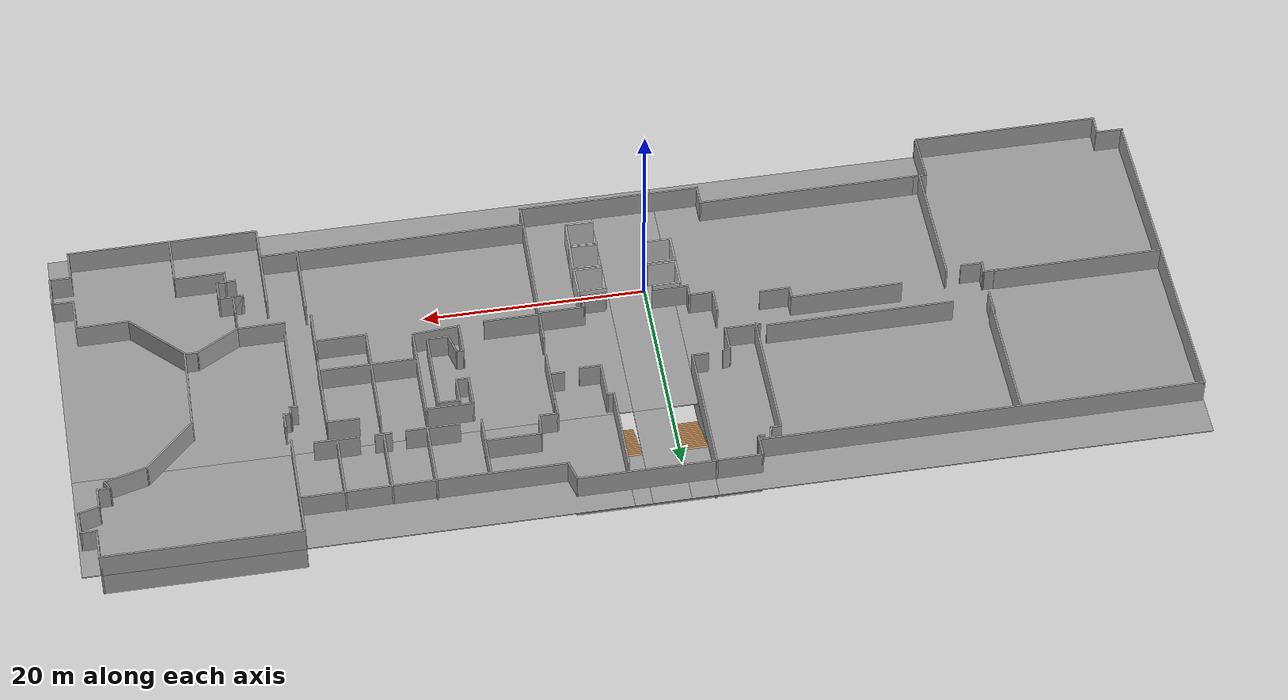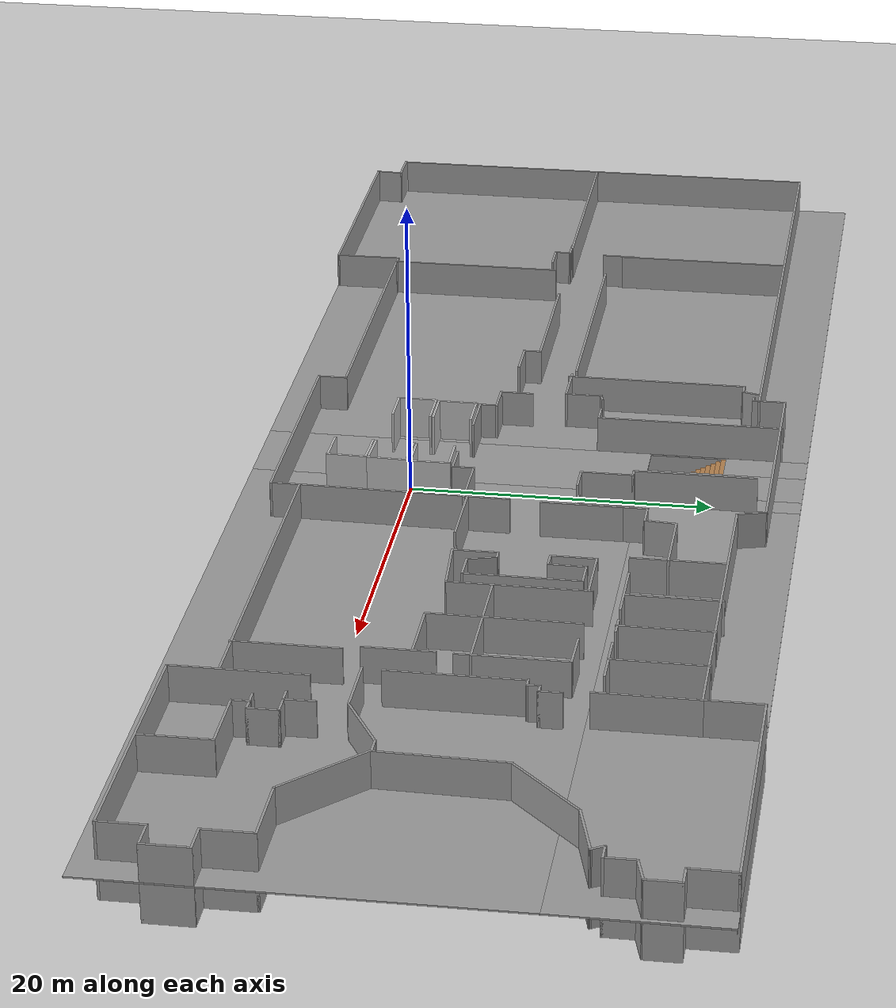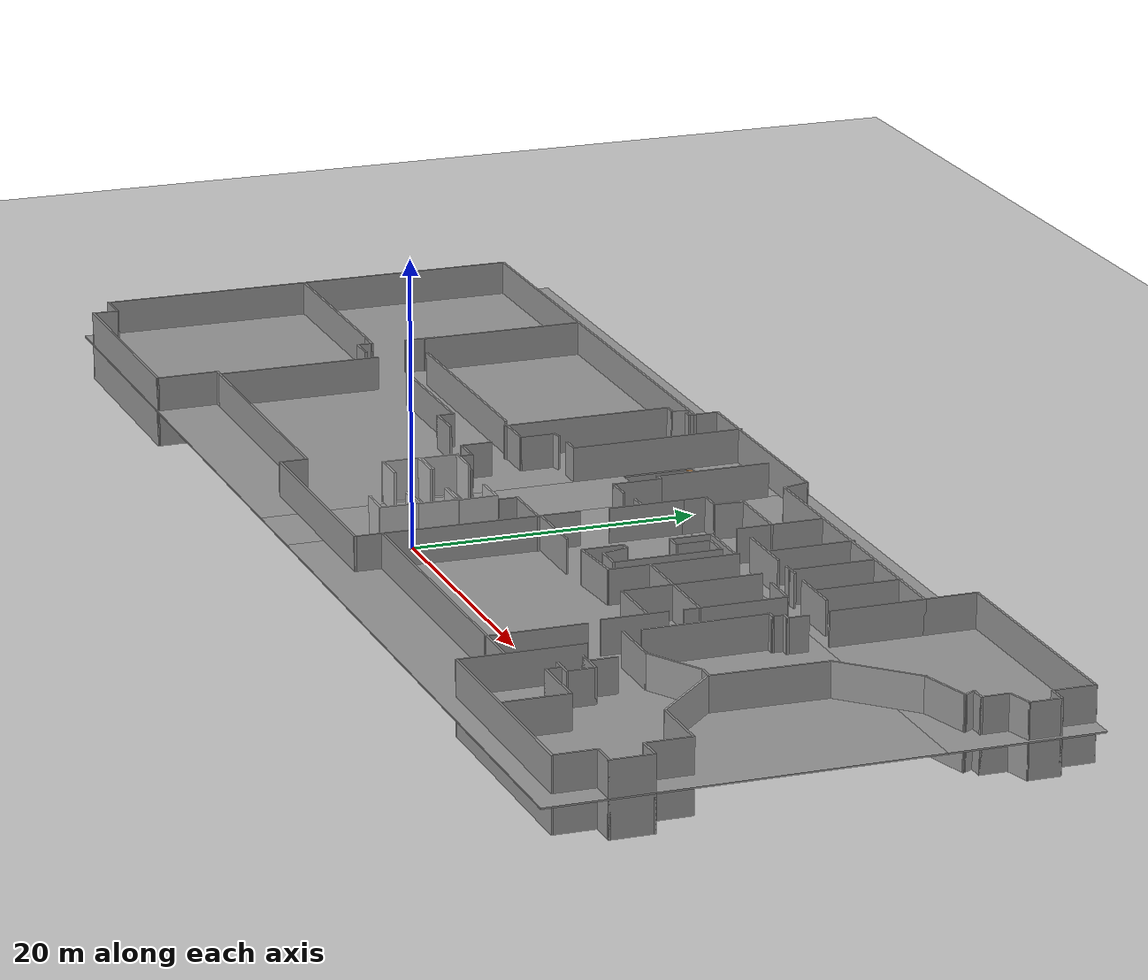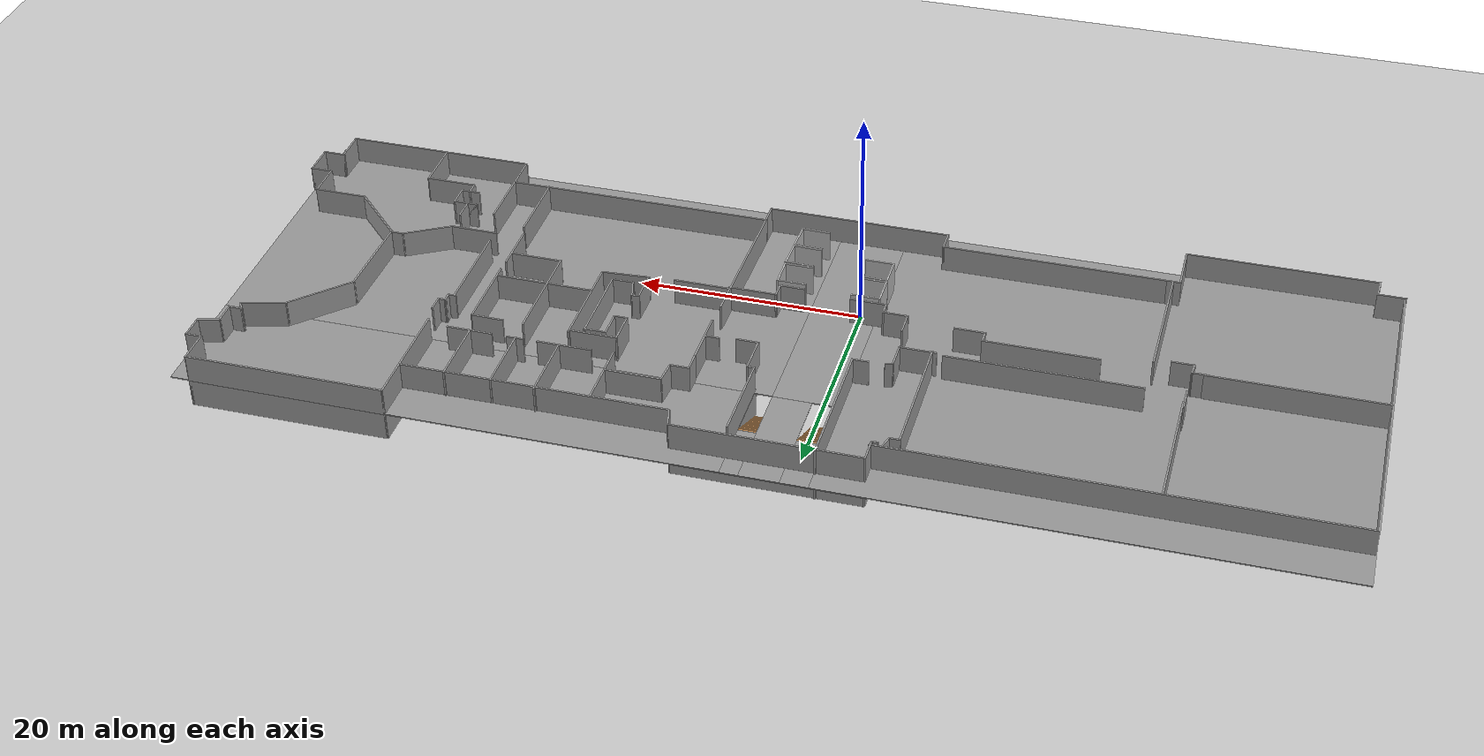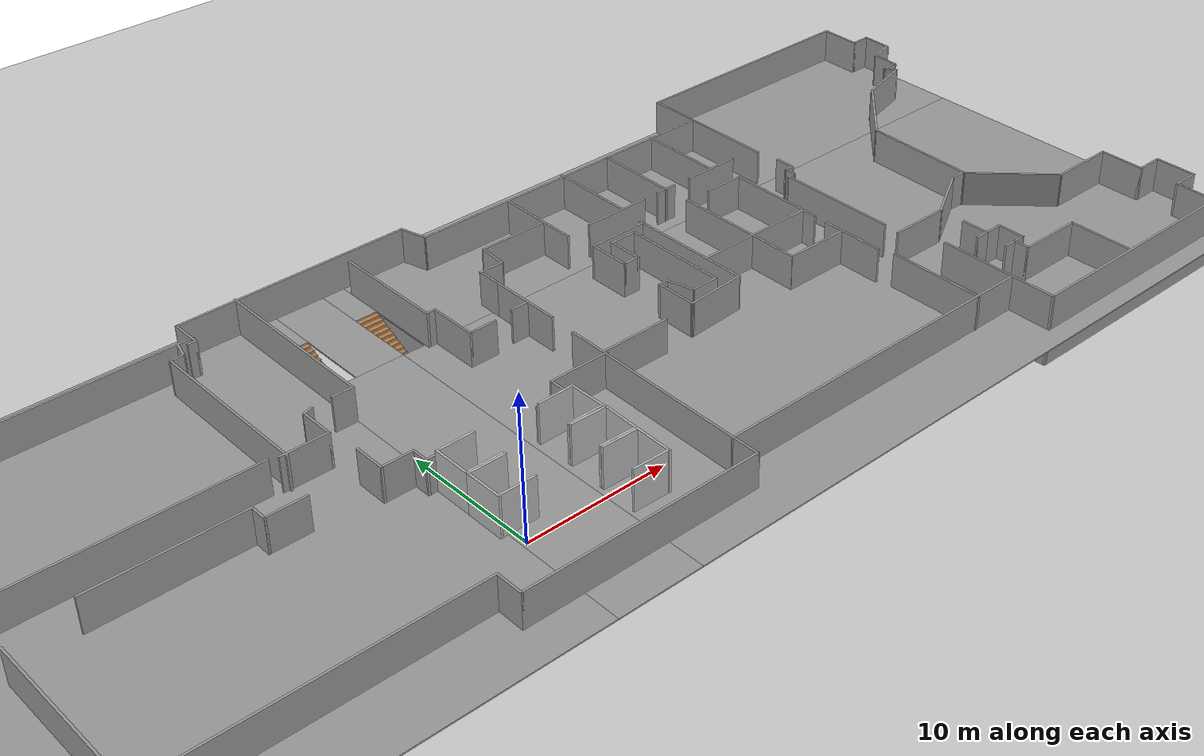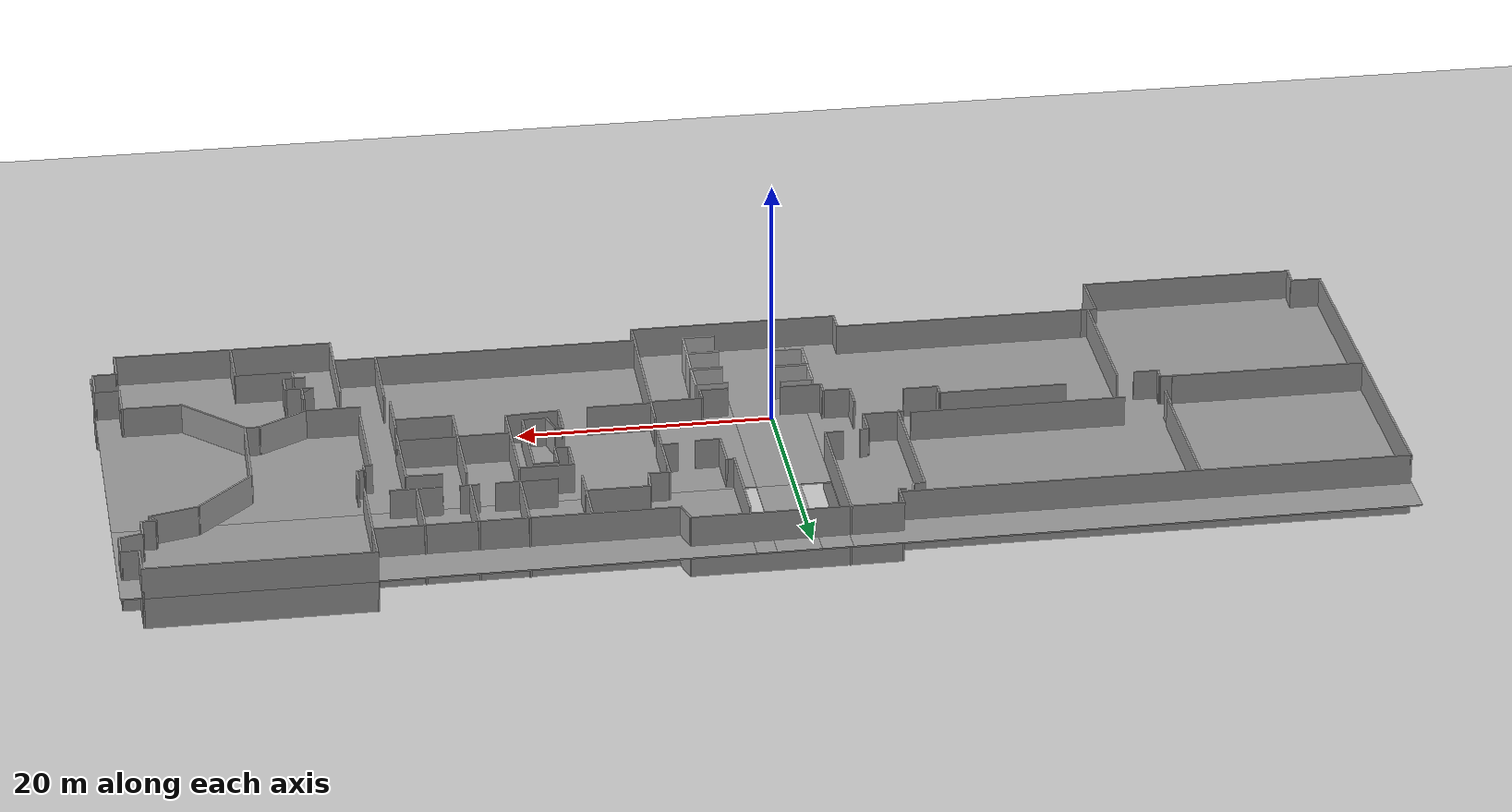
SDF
<sdf version="1.6">
 <world name="default">
  <light name="sun" type="directional">
   <pose>0 0 10 0 -0 0</pose>
   <diffuse>0.8 0.8 0.8 1</diffuse>
   <specular>0.2 0.2 0.2 1</specular>
   <attenuation>
    <range>1000</range>
    <constant>0.9</constant>
    <linear>0.01</linear>
    <quadratic>0.001</quadratic>
   </attenuation>
   <direction>-0.5 0.1 -0.9</direction>
  </light>
  <model name="ground_plane">
   <static>1</static>
   <link name="link">
    <collision name="collision">
     <geometry><plane><normal>0 0 1</normal><size>100 100</size></plane></geometry>
     <surface>
      <contact><collide_bitmask>65535</collide_bitmask></contact>
      <friction><ode><mu>100</mu><mu2>50</mu2></ode></friction>
     </surface>
    </collision>
    <visual name="visual">
     <cast_shadows>0</cast_shadows>
     <geometry><plane><normal>0 0 1</normal><size>100 100</size></plane></geometry>
     <material>
      <script><uri>file://media/materials/scripts/gazebo.material</uri><name>Gazebo/Grey</name></script>
     </material>
    </visual>
   </link>
  </model>
  <gravity>0 0 -9.8</gravity>
  <magnetic_field>6e-06 2.3e-05 -4.2e-05</magnetic_field>
  <atmosphere type="adiabatic"/>
  <physics name="default_physics" default="0" type="ode">
   <max_step_size>0.001</max_step_size>
   <real_time_factor>1</real_time_factor>
   <real_time_update_rate>1000</real_time_update_rate>
  </physics>
  <scene><ambient>0.4 0.4 0.4 1</ambient><background>0.7 0.7 0.7 1</background><shadows>1</shadows></scene>
  <audio><device>default</device></audio>
  <spherical_coordinates>
   <surface_model>EARTH_WGS84</surface_model>
   <latitude_deg>0</latitude_deg>
   <longitude_deg>0</longitude_deg>
   <elevation>0</elevation>
   <heading_deg>0</heading_deg>
  </spherical_coordinates>
  <model name="bush_refined_2floors">
   <pose>3.42472 8.10808 0 0 -0 0</pose>
   <link name="Floor_11">
    <pose>-1e-06 0 2.5 0 -0 0</pose>
    <visual name="Floor_11_Visual_0">
     <pose>-27.314 0 0.05 0 -0 0</pose>
     <geometry><box><size>43.531 35.9907 0.1</size></box></geometry>
     <material>
      <script><uri>file://media/materials/scripts/gazebo.material</uri><name>Gazebo/Grey</name></script>
      <ambient>1 1 1 1</ambient>
     </material>
     <meta><layer>1</layer></meta>
    </visual>
    <collision name="Floor_11_Collision_0">
     <geometry><box><size>43.531 35.9907 0.1</size></box></geometry>
     <pose>-27.314 0 0.05 0 -0 0</pose>
    </collision>
    <visual name="Floor_11_Visual_1">
     <pose>-2.67166 -5.16521 0.05 0 -0 0</pose>
     <geometry><box><size>5.75376 25.6603 0.1</size></box></geometry>
     <material>
      <script><uri>file://media/materials/scripts/gazebo.material</uri><name>Gazebo/Grey</name></script>
      <ambient>1 1 1 1</ambient>
     </material>
     <meta><layer>1</layer></meta>
    </visual>
    <collision name="Floor_11_Collision_1">
     <geometry><box><size>5.75376 25.6603 0.1</size></box></geometry>
     <pose>-2.67166 -5.16521 0.05 0 -0 0</pose>
    </collision>
    <visual name="Floor_11_Visual_2">
     <pose>24.6424 -5.18757 0.05 0 -0 0</pose>
     <geometry><box><size>48.8743 25.6156 0.1</size></box></geometry>
     <material>
      <script><uri>file://media/materials/scripts/gazebo.material</uri><name>Gazebo/Grey</name></script>
      <ambient>1 1 1 1</ambient>
     </material>
     <meta><layer>1</layer></meta>
    </visual>
    <collision name="Floor_11_Collision_2">
     <geometry><box><size>48.8743 25.6156 0.1</size></box></geometry>
     <pose>24.6424 -5.18757 0.05 0 -0 0</pose>
    </collision>
    <visual name="Floor_11_Visual_3">
     <pose>25.4174 12.8078 0.05 0 -0 0</pose>
     <geometry><box><size>47.3243 10.3751 0.1</size></box></geometry>
     <material>
      <script><uri>file://media/materials/scripts/gazebo.material</uri><name>Gazebo/Grey</name></script>
      <ambient>1 1 1 1</ambient>
     </material>
     <meta><layer>1</layer></meta>
    </visual>
    <collision name="Floor_11_Collision_3">
     <geometry><box><size>47.3243 10.3751 0.1</size></box></geometry>
     <pose>25.4174 12.8078 0.05 0 -0 0</pose>
    </collision>
    <visual name="Floor_11_Visual_4">
     <pose>-1.48885 12.8301 0.05 0 -0 0</pose>
     <geometry><box><size>3.38815 10.3304 0.1</size></box></geometry>
     <material>
      <script><uri>file://media/materials/scripts/gazebo.material</uri><name>Gazebo/Grey</name></script>
      <ambient>1 1 1 1</ambient>
     </material>
     <meta><layer>1</layer></meta>
    </visual>
    <collision name="Floor_11_Collision_4">
     <geometry><box><size>3.38815 10.3304 0.1</size></box></geometry>
     <pose>-1.48885 12.8301 0.05 0 -0 0</pose>
    </collision>
    <visual name="Floor_11_Visual_5">
     <pose>0.980227 15.277 0.05 0 -0 0</pose>
     <geometry><box><size>1.55 5.43661 0.1</size></box></geometry>
     <material>
      <script><uri>file://media/materials/scripts/gazebo.material</uri><name>Gazebo/Grey</name></script>
      <ambient>1 1 1 1</ambient>
     </material>
     <meta><layer>1</layer></meta>
    </visual>
    <collision name="Floor_11_Collision_5">
     <geometry><box><size>1.55 5.43661 0.1</size></box></geometry>
     <pose>0.980227 15.277 0.05 0 -0 0</pose>
    </collision>
    <visual name="Floor_11_Visual_6">
     <pose>-4.36573 15.3096 0.05 0 -0 0</pose>
     <geometry><box><size>2.36561 5.37156 0.1</size></box></geometry>
     <material>
      <script><uri>file://media/materials/scripts/gazebo.material</uri><name>Gazebo/Grey</name></script>
      <ambient>1 1 1 1</ambient>
     </material>
     <meta><layer>1</layer></meta>
    </visual>
    <collision name="Floor_11_Collision_6">
     <geometry><box><size>2.36561 5.37156 0.1</size></box></geometry>
     <pose>-4.36573 15.3096 0.05 0 -0 0</pose>
    </collision>
   </link>
   <link name="Stairs_0">
    <visual name="Stairs_0_Visual_0">
     <pose>-4.36573 7.83023 0.083333 0 -0 -3.14159</pose>
     <geometry><box><size>2.36561 0.330591 0.166667</size></box></geometry>
     <material>
      <script><uri>file://media/materials/scripts/gazebo.material</uri><name>Gazebo/Wood</name></script>
      <ambient>0.921569 0.807843 0.615686 1</ambient>
     </material>
     <meta><layer>0</layer></meta>
    </visual>
    <collision name="Stairs_0_Collision_0">
     <geometry><box><size>2.36561 0.330591 0.166667</size></box></geometry>
     <pose>-4.36573 7.83023 0.083333 0 -0 -3.14159</pose>
    </collision>
    <visual name="Stairs_0_Visual_1">
     <pose>-4.36573 8.16082 0.25 0 -0 -3.14159</pose>
     <geometry><box><size>2.36561 0.330591 0.166667</size></box></geometry>
     <material>
      <script><uri>file://media/materials/scripts/gazebo.material</uri><name>Gazebo/Wood</name></script>
      <ambient>0.921569 0.807843 0.615686 1</ambient>
     </material>
     <meta><layer>0</layer></meta>
    </visual>
    <collision name="Stairs_0_Collision_1">
     <geometry><box><size>2.36561 0.330591 0.166667</size></box></geometry>
     <pose>-4.36573 8.16082 0.25 0 -0 -3.14159</pose>
    </collision>
    <visual name="Stairs_0_Visual_2">
     <pose>-4.36573 8.49141 0.416667 0 -0 -3.14159</pose>
     <geometry><box><size>2.36561 0.330591 0.166667</size></box></geometry>
     <material>
      <script><uri>file://media/materials/scripts/gazebo.material</uri><name>Gazebo/Wood</name></script>
      <ambient>0.921569 0.807843 0.615686 1</ambient>
     </material>
     <meta><layer>0</layer></meta>
    </visual>
    <collision name="Stairs_0_Collision_2">
     <geometry><box><size>2.36561 0.330591 0.166667</size></box></geometry>
     <pose>-4.36573 8.49141 0.416667 0 -0 -3.14159</pose>
    </collision>
    <visual name="Stairs_0_Visual_3">
     <pose>-4.36573 8.822 0.583333 0 -0 -3.14159</pose>
     <geometry><box><size>2.36561 0.330591 0.166667</size></box></geometry>
     <material>
      <script><uri>file://media/materials/scripts/gazebo.material</uri><name>Gazebo/Wood</name></script>
      <ambient>0.921569 0.807843 0.615686 1</ambient>
     </material>
     <meta><layer>0</layer></meta>
    </visual>
    <collision name="Stairs_0_Collision_3">
     <geometry><box><size>2.36561 0.330591 0.166667</size></box></geometry>
     <pose>-4.36573 8.822 0.583333 0 -0 -3.14159</pose>
    </collision>
    <visual name="Stairs_0_Visual_4">
     <pose>-4.36573 9.15259 0.75 0 -0 -3.14159</pose>
     <geometry><box><size>2.36561 0.330591 0.166667</size></box></geometry>
     <material>
      <script><uri>file://media/materials/scripts/gazebo.material</uri><name>Gazebo/Wood</name></script>
      <ambient>0.921569 0.807843 0.615686 1</ambient>
     </material>
     <meta><layer>0</layer></meta>
    </visual>
    <collision name="Stairs_0_Collision_4">
     <geometry><box><size>2.36561 0.330591 0.166667</size></box></geometry>
     <pose>-4.36573 9.15259 0.75 0 -0 -3.14159</pose>
    </collision>
    <visual name="Stairs_0_Visual_5">
     <pose>-4.36573 9.48318 0.916667 0 -0 -3.14159</pose>
     <geometry><box><size>2.36561 0.330591 0.166667</size></box></geometry>
     <material>
      <script><uri>file://media/materials/scripts/gazebo.material</uri><name>Gazebo/Wood</name></script>
      <ambient>0.921569 0.807843 0.615686 1</ambient>
     </material>
     <meta><layer>0</layer></meta>
    </visual>
    <collision name="Stairs_0_Collision_5">
     <geometry><box><size>2.36561 0.330591 0.166667</size></box></geometry>
     <pose>-4.36573 9.48318 0.916667 0 -0 -3.14159</pose>
    </collision>
    <visual name="Stairs_0_Visual_6">
     <pose>-4.36573 9.81377 1.08333 0 -0 -3.14159</pose>
     <geometry><box><size>2.36561 0.330591 0.166667</size></box></geometry>
     <material>
      <script><uri>file://media/materials/scripts/gazebo.material</uri><name>Gazebo/Wood</name></script>
      <ambient>0.921569 0.807843 0.615686 1</ambient>
     </material>
     <meta><layer>0</layer></meta>
    </visual>
    <collision name="Stairs_0_Collision_6">
     <geometry><box><size>2.36561 0.330591 0.166667</size></box></geometry>
     <pose>-4.36573 9.81377 1.08333 0 -0 -3.14159</pose>
    </collision>
    <visual name="Stairs_0_Visual_7">
     <pose>-4.36573 10.1444 1.25 0 -0 -3.14159</pose>
     <geometry><box><size>2.36561 0.330591 0.166667</size></box></geometry>
     <material>
      <script><uri>file://media/materials/scripts/gazebo.material</uri><name>Gazebo/Wood</name></script>
      <ambient>0.921569 0.807843 0.615686 1</ambient>
     </material>
     <meta><layer>0</layer></meta>
    </visual>
    <collision name="Stairs_0_Collision_7">
     <geometry><box><size>2.36561 0.330591 0.166667</size></box></geometry>
     <pose>-4.36573 10.1444 1.25 0 -0 -3.14159</pose>
    </collision>
    <visual name="Stairs_0_Visual_8">
     <pose>-4.36573 10.475 1.41667 0 -0 -3.14159</pose>
     <geometry><box><size>2.36561 0.330591 0.166667</size></box></geometry>
     <material>
      <script><uri>file://media/materials/scripts/gazebo.material</uri><name>Gazebo/Wood</name></script>
      <ambient>0.921569 0.807843 0.615686 1</ambient>
     </material>
     <meta><layer>0</layer></meta>
    </visual>
    <collision name="Stairs_0_Collision_8">
     <geometry><box><size>2.36561 0.330591 0.166667</size></box></geometry>
     <pose>-4.36573 10.475 1.41667 0 -0 -3.14159</pose>
    </collision>
    <visual name="Stairs_0_Visual_9">
     <pose>-4.36573 10.8055 1.58333 0 -0 -3.14159</pose>
     <geometry><box><size>2.36561 0.330591 0.166667</size></box></geometry>
     <material>
      <script><uri>file://media/materials/scripts/gazebo.material</uri><name>Gazebo/Wood</name></script>
      <ambient>0.921569 0.807843 0.615686 1</ambient>
     </material>
     <meta><layer>0</layer></meta>
    </visual>
    <collision name="Stairs_0_Collision_9">
     <geometry><box><size>2.36561 0.330591 0.166667</size></box></geometry>
     <pose>-4.36573 10.8055 1.58333 0 -0 -3.14159</pose>
    </collision>
    <visual name="Stairs_0_Visual_10">
     <pose>-4.36573 11.1361 1.75 0 -0 -3.14159</pose>
     <geometry><box><size>2.36561 0.330591 0.166667</size></box></geometry>
     <material>
      <script><uri>file://media/materials/scripts/gazebo.material</uri><name>Gazebo/Wood</name></script>
      <ambient>0.921569 0.807843 0.615686 1</ambient>
     </material>
     <meta><layer>0</layer></meta>
    </visual>
    <collision name="Stairs_0_Collision_10">
     <geometry><box><size>2.36561 0.330591 0.166667</size></box></geometry>
     <pose>-4.36573 11.1361 1.75 0 -0 -3.14159</pose>
    </collision>
    <visual name="Stairs_0_Visual_11">
     <pose>-4.36573 11.4667 1.91667 0 -0 -3.14159</pose>
     <geometry><box><size>2.36561 0.330591 0.166667</size></box></geometry>
     <material>
      <script><uri>file://media/materials/scripts/gazebo.material</uri><name>Gazebo/Wood</name></script>
      <ambient>0.921569 0.807843 0.615686 1</ambient>
     </material>
     <meta><layer>0</layer></meta>
    </visual>
    <collision name="Stairs_0_Collision_11">
     <geometry><box><size>2.36561 0.330591 0.166667</size></box></geometry>
     <pose>-4.36573 11.4667 1.91667 0 -0 -3.14159</pose>
    </collision>
    <visual name="Stairs_0_Visual_12">
     <pose>-4.36573 11.7973 2.08333 0 -0 -3.14159</pose>
     <geometry><box><size>2.36561 0.330591 0.166667</size></box></geometry>
     <material>
      <script><uri>file://media/materials/scripts/gazebo.material</uri><name>Gazebo/Wood</name></script>
      <ambient>0.921569 0.807843 0.615686 1</ambient>
     </material>
     <meta><layer>0</layer></meta>
    </visual>
    <collision name="Stairs_0_Collision_12">
     <geometry><box><size>2.36561 0.330591 0.166667</size></box></geometry>
     <pose>-4.36573 11.7973 2.08333 0 -0 -3.14159</pose>
    </collision>
    <visual name="Stairs_0_Visual_13">
     <pose>-4.36573 12.1279 2.25 0 -0 -3.14159</pose>
     <geometry><box><size>2.36561 0.330591 0.166667</size></box></geometry>
     <material>
      <script><uri>file://media/materials/scripts/gazebo.material</uri><name>Gazebo/Wood</name></script>
      <ambient>0.921569 0.807843 0.615686 1</ambient>
     </material>
     <meta><layer>0</layer></meta>
    </visual>
    <collision name="Stairs_0_Collision_13">
     <geometry><box><size>2.36561 0.330591 0.166667</size></box></geometry>
     <pose>-4.36573 12.1279 2.25 0 -0 -3.14159</pose>
    </collision>
    <visual name="Stairs_0_Visual_14">
     <pose>-4.36573 12.4585 2.41667 0 -0 -3.14159</pose>
     <geometry><box><size>2.36561 0.330591 0.166667</size></box></geometry>
     <material>
      <script><uri>file://media/materials/scripts/gazebo.material</uri><name>Gazebo/Wood</name></script>
      <ambient>0.921569 0.807843 0.615686 1</ambient>
     </material>
     <meta><layer>0</layer></meta>
    </visual>
    <collision name="Stairs_0_Collision_14">
     <geometry><box><size>2.36561 0.330591 0.166667</size></box></geometry>
     <pose>-4.36573 12.4585 2.41667 0 -0 -3.14159</pose>
    </collision>
   </link>
   <link name="Stairs_1">
    <visual name="Stairs_1_Visual_0">
     <pose>0.980225 7.78482 0.083333 0 -0 -3.14159</pose>
     <geometry><box><size>1.55 0.329236 0.166667</size></box></geometry>
     <material>
      <script><uri>file://media/materials/scripts/gazebo.material</uri><name>Gazebo/Wood</name></script>
      <ambient>0.921569 0.807843 0.615686 1</ambient>
     </material>
     <meta><layer>0</layer></meta>
    </visual>
    <collision name="Stairs_1_Collision_0">
     <geometry><box><size>1.55 0.329236 0.166667</size></box></geometry>
     <pose>0.980225 7.78482 0.083333 0 -0 -3.14159</pose>
    </collision>
    <visual name="Stairs_1_Visual_1">
     <pose>0.980225 8.11406 0.25 0 -0 -3.14159</pose>
     <geometry><box><size>1.55 0.329236 0.166667</size></box></geometry>
     <material>
      <script><uri>file://media/materials/scripts/gazebo.material</uri><name>Gazebo/Wood</name></script>
      <ambient>0.921569 0.807843 0.615686 1</ambient>
     </material>
     <meta><layer>0</layer></meta>
    </visual>
    <collision name="Stairs_1_Collision_1">
     <geometry><box><size>1.55 0.329236 0.166667</size></box></geometry>
     <pose>0.980225 8.11406 0.25 0 -0 -3.14159</pose>
    </collision>
    <visual name="Stairs_1_Visual_2">
     <pose>0.980225 8.4433 0.416667 0 -0 -3.14159</pose>
     <geometry><box><size>1.55 0.329236 0.166667</size></box></geometry>
     <material>
      <script><uri>file://media/materials/scripts/gazebo.material</uri><name>Gazebo/Wood</name></script>
      <ambient>0.921569 0.807843 0.615686 1</ambient>
     </material>
     <meta><layer>0</layer></meta>
    </visual>
    <collision name="Stairs_1_Collision_2">
     <geometry><box><size>1.55 0.329236 0.166667</size></box></geometry>
     <pose>0.980225 8.4433 0.416667 0 -0 -3.14159</pose>
    </collision>
    <visual name="Stairs_1_Visual_3">
     <pose>0.980225 8.77253 0.583333 0 -0 -3.14159</pose>
     <geometry><box><size>1.55 0.329236 0.166667</size></box></geometry>
     <material>
      <script><uri>file://media/materials/scripts/gazebo.material</uri><name>Gazebo/Wood</name></script>
      <ambient>0.921569 0.807843 0.615686 1</ambient>
     </material>
     <meta><layer>0</layer></meta>
    </visual>
    <collision name="Stairs_1_Collision_3">
     <geometry><box><size>1.55 0.329236 0.166667</size></box></geometry>
     <pose>0.980225 8.77253 0.583333 0 -0 -3.14159</pose>
    </collision>
    <visual name="Stairs_1_Visual_4">
     <pose>0.980225 9.10177 0.75 0 -0 -3.14159</pose>
     <geometry><box><size>1.55 0.329236 0.166667</size></box></geometry>
     <material>
      <script><uri>file://media/materials/scripts/gazebo.material</uri><name>Gazebo/Wood</name></script>
      <ambient>0.921569 0.807843 0.615686 1</ambient>
     </material>
     <meta><layer>0</layer></meta>
    </visual>
    <collision name="Stairs_1_Collision_4">
     <geometry><box><size>1.55 0.329236 0.166667</size></box></geometry>
     <pose>0.980225 9.10177 0.75 0 -0 -3.14159</pose>
    </collision>
    <visual name="Stairs_1_Visual_5">
     <pose>0.980225 9.431 0.916667 0 -0 -3.14159</pose>
     <geometry><box><size>1.55 0.329236 0.166667</size></box></geometry>
     <material>
      <script><uri>file://media/materials/scripts/gazebo.material</uri><name>Gazebo/Wood</name></script>
      <ambient>0.921569 0.807843 0.615686 1</ambient>
     </material>
     <meta><layer>0</layer></meta>
    </visual>
    <collision name="Stairs_1_Collision_5">
     <geometry><box><size>1.55 0.329236 0.166667</size></box></geometry>
     <pose>0.980225 9.431 0.916667 0 -0 -3.14159</pose>
    </collision>
    <visual name="Stairs_1_Visual_6">
     <pose>0.980225 9.76024 1.08333 0 -0 -3.14159</pose>
     <geometry><box><size>1.55 0.329236 0.166667</size></box></geometry>
     <material>
      <script><uri>file://media/materials/scripts/gazebo.material</uri><name>Gazebo/Wood</name></script>
      <ambient>0.921569 0.807843 0.615686 1</ambient>
     </material>
     <meta><layer>0</layer></meta>
    </visual>
    <collision name="Stairs_1_Collision_6">
     <geometry><box><size>1.55 0.329236 0.166667</size></box></geometry>
     <pose>0.980225 9.76024 1.08333 0 -0 -3.14159</pose>
    </collision>
    <visual name="Stairs_1_Visual_7">
     <pose>0.980225 10.0895 1.25 0 -0 -3.14159</pose>
     <geometry><box><size>1.55 0.329236 0.166667</size></box></geometry>
     <material>
      <script><uri>file://media/materials/scripts/gazebo.material</uri><name>Gazebo/Wood</name></script>
      <ambient>0.921569 0.807843 0.615686 1</ambient>
     </material>
     <meta><layer>0</layer></meta>
    </visual>
    <collision name="Stairs_1_Collision_7">
     <geometry><box><size>1.55 0.329236 0.166667</size></box></geometry>
     <pose>0.980225 10.0895 1.25 0 -0 -3.14159</pose>
    </collision>
    <visual name="Stairs_1_Visual_8">
     <pose>0.980225 10.4187 1.41667 0 -0 -3.14159</pose>
     <geometry><box><size>1.55 0.329236 0.166667</size></box></geometry>
     <material>
      <script><uri>file://media/materials/scripts/gazebo.material</uri><name>Gazebo/Wood</name></script>
      <ambient>0.921569 0.807843 0.615686 1</ambient>
     </material>
     <meta><layer>0</layer></meta>
    </visual>
    <collision name="Stairs_1_Collision_8">
     <geometry><box><size>1.55 0.329236 0.166667</size></box></geometry>
     <pose>0.980225 10.4187 1.41667 0 -0 -3.14159</pose>
    </collision>
    <visual name="Stairs_1_Visual_9">
     <pose>0.980225 10.7479 1.58333 0 -0 -3.14159</pose>
     <geometry><box><size>1.55 0.329236 0.166667</size></box></geometry>
     <material>
      <script><uri>file://media/materials/scripts/gazebo.material</uri><name>Gazebo/Wood</name></script>
      <ambient>0.921569 0.807843 0.615686 1</ambient>
     </material>
     <meta><layer>0</layer></meta>
    </visual>
    <collision name="Stairs_1_Collision_9">
     <geometry><box><size>1.55 0.329236 0.166667</size></box></geometry>
     <pose>0.980225 10.7479 1.58333 0 -0 -3.14159</pose>
    </collision>
    <visual name="Stairs_1_Visual_10">
     <pose>0.980225 11.0772 1.75 0 -0 -3.14159</pose>
     <geometry><box><size>1.55 0.329236 0.166667</size></box></geometry>
     <material>
      <script><uri>file://media/materials/scripts/gazebo.material</uri><name>Gazebo/Wood</name></script>
      <ambient>0.921569 0.807843 0.615686 1</ambient>
     </material>
     <meta><layer>0</layer></meta>
    </visual>
    <collision name="Stairs_1_Collision_10">
     <geometry><box><size>1.55 0.329236 0.166667</size></box></geometry>
     <pose>0.980225 11.0772 1.75 0 -0 -3.14159</pose>
    </collision>
    <visual name="Stairs_1_Visual_11">
     <pose>0.980225 11.4064 1.91667 0 -0 -3.14159</pose>
     <geometry><box><size>1.55 0.329236 0.166667</size></box></geometry>
     <material>
      <script><uri>file://media/materials/scripts/gazebo.material</uri><name>Gazebo/Wood</name></script>
      <ambient>0.921569 0.807843 0.615686 1</ambient>
     </material>
     <meta><layer>0</layer></meta>
    </visual>
    <collision name="Stairs_1_Collision_11">
     <geometry><box><size>1.55 0.329236 0.166667</size></box></geometry>
     <pose>0.980225 11.4064 1.91667 0 -0 -3.14159</pose>
    </collision>
    <visual name="Stairs_1_Visual_12">
     <pose>0.980225 11.7357 2.08333 0 -0 -3.14159</pose>
     <geometry><box><size>1.55 0.329236 0.166667</size></box></geometry>
     <material>
      <script><uri>file://media/materials/scripts/gazebo.material</uri><name>Gazebo/Wood</name></script>
      <ambient>0.921569 0.807843 0.615686 1</ambient>
     </material>
     <meta><layer>0</layer></meta>
    </visual>
    <collision name="Stairs_1_Collision_12">
     <geometry><box><size>1.55 0.329236 0.166667</size></box></geometry>
     <pose>0.980225 11.7357 2.08333 0 -0 -3.14159</pose>
    </collision>
    <visual name="Stairs_1_Visual_13">
     <pose>0.980225 12.0649 2.25 0 -0 -3.14159</pose>
     <geometry><box><size>1.55 0.329236 0.166667</size></box></geometry>
     <material>
      <script><uri>file://media/materials/scripts/gazebo.material</uri><name>Gazebo/Wood</name></script>
      <ambient>0.921569 0.807843 0.615686 1</ambient>
     </material>
     <meta><layer>0</layer></meta>
    </visual>
    <collision name="Stairs_1_Collision_13">
     <geometry><box><size>1.55 0.329236 0.166667</size></box></geometry>
     <pose>0.980225 12.0649 2.25 0 -0 -3.14159</pose>
    </collision>
    <visual name="Stairs_1_Visual_14">
     <pose>0.980225 12.3941 2.41667 0 -0 -3.14159</pose>
     <geometry><box><size>1.55 0.329236 0.166667</size></box></geometry>
     <material>
      <script><uri>file://media/materials/scripts/gazebo.material</uri><name>Gazebo/Wood</name></script>
      <ambient>0.921569 0.807843 0.615686 1</ambient>
     </material>
     <meta><layer>0</layer></meta>
    </visual>
    <collision name="Stairs_1_Collision_14">
     <geometry><box><size>1.55 0.329236 0.166667</size></box></geometry>
     <pose>0.980225 12.3941 2.41667 0 -0 -3.14159</pose>
    </collision>
   </link>
   <link name="Wall_1">
    <collision name="Wall_1_Collision">
     <geometry><box><size>0.62833 0.15 2.5</size></box></geometry>
     <pose>0 0 1.25 0 -0 0</pose>
    </collision>
    <visual name="Wall_1_Visual">
     <pose>0 0 1.25 0 -0 0</pose>
     <geometry><box><size>0.62833 0.15 2.5</size></box></geometry>
     <material>
      <script><uri>file://media/materials/scripts/gazebo.material</uri><name>Gazebo/Grey</name></script>
      <ambient>1 1 1 1</ambient>
     </material>
     <meta><layer>0</layer></meta>
    </visual>
    <pose>-9.88269 14.0073 0 0 -0 0</pose>
   </link>
   <link name="Wall_10">
    <collision name="Wall_10_Collision">
     <geometry><box><size>2.25 0.15 2.5</size></box></geometry>
     <pose>0 0 1.25 0 -0 0</pose>
    </collision>
    <visual name="Wall_10_Visual">
     <pose>0 0 1.25 0 -0 0</pose>
     <geometry><box><size>2.25 0.15 2.5</size></box></geometry>
     <material>
      <script><uri>file://media/materials/scripts/gazebo.material</uri><name>Gazebo/Grey</name></script>
      <ambient>1 1 1 1</ambient>
     </material>
     <meta><layer>0</layer></meta>
    </visual>
    <pose>48.7353 14.0204 0 0 -0 -1.5708</pose>
   </link>
   <link name="Wall_1000">
    <collision name="Wall_1000_Collision">
     <geometry><box><size>1.25 0.15 2.5</size></box></geometry>
     <pose>0 0 1.25 0 -0 0</pose>
    </collision>
    <visual name="Wall_1000_Visual">
     <pose>0 0 1.25 0 -0 0</pose>
     <geometry><box><size>1.25 0.15 2.5</size></box></geometry>
     <material>
      <script><uri>file://media/materials/scripts/gazebo.material</uri><name>Gazebo/Grey</name></script>
      <ambient>1 1 1 1</ambient>
     </material>
     <meta><layer>1</layer></meta>
    </visual>
    <pose>14.5533 3.51018 2.5 0 -0 0</pose>
   </link>
   <link name="Wall_1001">
    <collision name="Wall_1001_Collision">
     <geometry><box><size>2.5 0.15 2.5</size></box></geometry>
     <pose>0 0 1.25 0 -0 0</pose>
    </collision>
    <visual name="Wall_1001_Visual">
     <pose>0 0 1.25 0 -0 0</pose>
     <geometry><box><size>2.5 0.15 2.5</size></box></geometry>
     <material>
      <script><uri>file://media/materials/scripts/gazebo.material</uri><name>Gazebo/Grey</name></script>
      <ambient>1 1 1 1</ambient>
     </material>
     <meta><layer>1</layer></meta>
    </visual>
    <pose>15.1033 4.68518 2.5 0 -0 1.5708</pose>
   </link>
   <link name="Wall_1002">
    <collision name="Wall_1002_Collision">
     <geometry><box><size>2 0.15 2.5</size></box></geometry>
     <pose>0 0 1.25 0 -0 0</pose>
    </collision>
    <visual name="Wall_1002_Visual">
     <pose>0 0 1.25 0 -0 0</pose>
     <geometry><box><size>2 0.15 2.5</size></box></geometry>
     <material>
      <script><uri>file://media/materials/scripts/gazebo.material</uri><name>Gazebo/Grey</name></script>
      <ambient>1 1 1 1</ambient>
     </material>
     <meta><layer>1</layer></meta>
    </visual>
    <pose>16.0283 5.86018 2.5 0 -0 0</pose>
   </link>
   <link name="Wall_1003">
    <collision name="Wall_1003_Collision">
     <geometry><box><size>7.5 0.15 2.5</size></box></geometry>
     <pose>0 0 1.25 0 -0 0</pose>
    </collision>
    <visual name="Wall_1003_Visual">
     <pose>0 0 1.25 0 -0 0</pose>
     <geometry><box><size>7.5 0.15 2.5</size></box></geometry>
     <material>
      <script><uri>file://media/materials/scripts/gazebo.material</uri><name>Gazebo/Grey</name></script>
      <ambient>1 1 1 1</ambient>
     </material>
     <meta><layer>1</layer></meta>
    </visual>
    <pose>16.9533 2.18518 2.5 0 -0 -1.5708</pose>
   </link>
   <link name="Wall_1004">
    <collision name="Wall_1004_Collision">
     <geometry><box><size>2 0.15 2.5</size></box></geometry>
     <pose>0 0 1.25 0 -0 0</pose>
    </collision>
    <visual name="Wall_1004_Visual">
     <pose>0 0 1.25 0 -0 0</pose>
     <geometry><box><size>2 0.15 2.5</size></box></geometry>
     <material>
      <script><uri>file://media/materials/scripts/gazebo.material</uri><name>Gazebo/Grey</name></script>
      <ambient>1 1 1 1</ambient>
     </material>
     <meta><layer>1</layer></meta>
    </visual>
    <pose>16.0283 -1.48982 2.5 0 -0 3.14159</pose>
   </link>
   <link name="Wall_1005">
    <collision name="Wall_1005_Collision">
     <geometry><box><size>2 0.15 2.5</size></box></geometry>
     <pose>0 0 1.25 0 -0 0</pose>
    </collision>
    <visual name="Wall_1005_Visual">
     <pose>0 0 1.25 0 -0 0</pose>
     <geometry><box><size>2 0.15 2.5</size></box></geometry>
     <material>
      <script><uri>file://media/materials/scripts/gazebo.material</uri><name>Gazebo/Grey</name></script>
      <ambient>1 1 1 1</ambient>
     </material>
     <meta><layer>1</layer></meta>
    </visual>
    <pose>14.8639 -0.596338 2.5 0 -0 1.8326</pose>
   </link>
   <link name="Wall_1006">
    <collision name="Wall_1006_Collision">
     <geometry><box><size>0.75 0.15 2.5</size></box></geometry>
     <pose>0 0 1.25 0 -0 0</pose>
    </collision>
    <visual name="Wall_1006_Visual">
     <pose>0 0 1.25 0 -0 0</pose>
     <geometry><box><size>0.75 0.15 2.5</size></box></geometry>
     <material>
      <script><uri>file://media/materials/scripts/gazebo.material</uri><name>Gazebo/Grey</name></script>
      <ambient>1 1 1 1</ambient>
     </material>
     <meta><layer>1</layer></meta>
    </visual>
    <pose>14.3245 0.297143 2.5 0 -0 3.14159</pose>
   </link>
   <link name="Wall_1007">
    <collision name="Wall_1007_Collision">
     <geometry><box><size>3 0.15 2.5</size></box></geometry>
     <pose>0 0 1.25 0 -0 0</pose>
    </collision>
    <visual name="Wall_1007_Visual">
     <pose>0 0 1.25 0 -0 0</pose>
     <geometry><box><size>3 0.15 2.5</size></box></geometry>
     <material>
      <script><uri>file://media/materials/scripts/gazebo.material</uri><name>Gazebo/Grey</name></script>
      <ambient>1 1 1 1</ambient>
     </material>
     <meta><layer>1</layer></meta>
    </visual>
    <pose>14.0245 -1.12786 2.5 0 -0 -1.5708</pose>
   </link>
   <link name="Wall_1008">
    <collision name="Wall_1008_Collision">
     <geometry><box><size>4.26553 0.15 2.5</size></box></geometry>
     <pose>0 0 1.25 0 -0 0</pose>
    </collision>
    <visual name="Wall_1008_Visual">
     <pose>0 0 1.25 0 -0 0</pose>
     <geometry><box><size>4.26553 0.15 2.5</size></box></geometry>
     <material>
      <script><uri>file://media/materials/scripts/gazebo.material</uri><name>Gazebo/Grey</name></script>
      <ambient>1 1 1 1</ambient>
     </material>
     <meta><layer>1</layer></meta>
    </visual>
    <pose>16.0778 -2.4164 2.5 0 -0 0.066363</pose>
   </link>
   <link name="Wall_1009">
    <collision name="Wall_1009_Collision">
     <geometry><box><size>5 0.15 2.5</size></box></geometry>
     <pose>0 0 1.25 0 -0 0</pose>
    </collision>
    <visual name="Wall_1009_Visual">
     <pose>0 0 1.25 0 -0 0</pose>
     <geometry><box><size>5 0.15 2.5</size></box></geometry>
     <material>
      <script><uri>file://media/materials/scripts/gazebo.material</uri><name>Gazebo/Grey</name></script>
      <ambient>1 1 1 1</ambient>
     </material>
     <meta><layer>1</layer></meta>
    </visual>
    <pose>9.2924 -2.73465 2.5 0 -0 0</pose>
   </link>
   <link name="Wall_101">
    <collision name="Wall_101_Collision">
     <geometry><box><size>3.25 0.15 2.5</size></box></geometry>
     <pose>0 0 1.25 0 -0 0</pose>
    </collision>
    <visual name="Wall_101_Visual">
     <pose>0 0 1.25 0 -0 0</pose>
     <geometry><box><size>3.25 0.15 2.5</size></box></geometry>
     <material>
      <script><uri>file://media/materials/scripts/gazebo.material</uri><name>Gazebo/Grey</name></script>
      <ambient>1 1 1 1</ambient>
     </material>
     <meta><layer>0</layer></meta>
    </visual>
    <pose>-10.5418 1.53292 0 0 -0 0</pose>
   </link>
   <link name="Wall_1010">
    <collision name="Wall_1010_Collision">
     <geometry><box><size>13.6092 0.15 2.5</size></box></geometry>
     <pose>0 0 1.25 0 -0 0</pose>
    </collision>
    <visual name="Wall_1010_Visual">
     <pose>0 0 1.25 0 -0 0</pose>
     <geometry><box><size>13.6092 0.15 2.5</size></box></geometry>
     <material>
      <script><uri>file://media/materials/scripts/gazebo.material</uri><name>Gazebo/Grey</name></script>
      <ambient>1 1 1 1</ambient>
     </material>
     <meta><layer>1</layer></meta>
    </visual>
    <pose>6.75021 -6.80477 2.5 0 -0 -1.58821</pose>
   </link>
   <link name="Wall_1011">
    <collision name="Wall_1011_Collision">
     <geometry><box><size>4.25 0.15 2.5</size></box></geometry>
     <pose>0 0 1.25 0 -0 0</pose>
    </collision>
    <visual name="Wall_1011_Visual">
     <pose>0 0 1.25 0 -0 0</pose>
     <geometry><box><size>4.25 0.15 2.5</size></box></geometry>
     <material>
      <script><uri>file://media/materials/scripts/gazebo.material</uri><name>Gazebo/Grey</name></script>
      <ambient>1 1 1 1</ambient>
     </material>
     <meta><layer>1</layer></meta>
    </visual>
    <pose>4.8597 -2.94453 2.5 0 -0 0</pose>
   </link>
   <link name="Wall_1012">
    <collision name="Wall_1012_Collision">
     <geometry><box><size>1.5 0.15 2.5</size></box></geometry>
     <pose>0 0 1.25 0 -0 0</pose>
    </collision>
    <visual name="Wall_1012_Visual">
     <pose>0 0 1.25 0 -0 0</pose>
     <geometry><box><size>1.5 0.15 2.5</size></box></geometry>
     <material>
      <script><uri>file://media/materials/scripts/gazebo.material</uri><name>Gazebo/Grey</name></script>
      <ambient>1 1 1 1</ambient>
     </material>
     <meta><layer>1</layer></meta>
    </visual>
    <pose>2.80971 -3.61953 2.5 0 -0 -1.5708</pose>
   </link>
   <link name="Wall_1013">
    <collision name="Wall_1013_Collision">
     <geometry><box><size>2.25 0.15 2.5</size></box></geometry>
     <pose>0 0 1.25 0 -0 0</pose>
    </collision>
    <visual name="Wall_1013_Visual">
     <pose>0 0 1.25 0 -0 0</pose>
     <geometry><box><size>2.25 0.15 2.5</size></box></geometry>
     <material>
      <script><uri>file://media/materials/scripts/gazebo.material</uri><name>Gazebo/Grey</name></script>
      <ambient>1 1 1 1</ambient>
     </material>
     <meta><layer>1</layer></meta>
    </visual>
    <pose>1.75971 -4.29453 2.5 0 -0 3.14159</pose>
   </link>
   <link name="Wall_1014">
    <collision name="Wall_1014_Collision">
     <geometry><box><size>3.25 0.15 2.5</size></box></geometry>
     <pose>0 0 1.25 0 -0 0</pose>
    </collision>
    <visual name="Wall_1014_Visual">
     <pose>0 0 1.25 0 -0 0</pose>
     <geometry><box><size>3.25 0.15 2.5</size></box></geometry>
     <material>
      <script><uri>file://media/materials/scripts/gazebo.material</uri><name>Gazebo/Grey</name></script>
      <ambient>1 1 1 1</ambient>
     </material>
     <meta><layer>1</layer></meta>
    </visual>
    <pose>-5.03672 -3.92398 2.5 0 -0 3.14159</pose>
   </link>
   <link name="Wall_1015">
    <collision name="Wall_1015_Collision">
     <geometry><box><size>1.25 0.15 2.5</size></box></geometry>
     <pose>0 0 1.25 0 -0 0</pose>
    </collision>
    <visual name="Wall_1015_Visual">
     <pose>0 0 1.25 0 -0 0</pose>
     <geometry><box><size>1.25 0.15 2.5</size></box></geometry>
     <material>
      <script><uri>file://media/materials/scripts/gazebo.material</uri><name>Gazebo/Grey</name></script>
      <ambient>1 1 1 1</ambient>
     </material>
     <meta><layer>1</layer></meta>
    </visual>
    <pose>-6.58672 -3.37398 2.5 0 -0 1.5708</pose>
   </link>
   <link name="Wall_1016">
    <collision name="Wall_1016_Collision">
     <geometry><box><size>2.25 0.15 2.5</size></box></geometry>
     <pose>0 0 1.25 0 -0 0</pose>
    </collision>
    <visual name="Wall_1016_Visual">
     <pose>0 0 1.25 0 -0 0</pose>
     <geometry><box><size>2.25 0.15 2.5</size></box></geometry>
     <material>
      <script><uri>file://media/materials/scripts/gazebo.material</uri><name>Gazebo/Grey</name></script>
      <ambient>1 1 1 1</ambient>
     </material>
     <meta><layer>1</layer></meta>
    </visual>
    <pose>-7.63672 -2.82398 2.5 0 -0 3.14159</pose>
   </link>
   <link name="Wall_1017">
    <collision name="Wall_1017_Collision">
     <geometry><box><size>2.25 0.15 2.5</size></box></geometry>
     <pose>0 0 1.25 0 -0 0</pose>
    </collision>
    <visual name="Wall_1017_Visual">
     <pose>0 0 1.25 0 -0 0</pose>
     <geometry><box><size>2.25 0.15 2.5</size></box></geometry>
     <material>
      <script><uri>file://media/materials/scripts/gazebo.material</uri><name>Gazebo/Grey</name></script>
      <ambient>1 1 1 1</ambient>
     </material>
     <meta><layer>1</layer></meta>
    </visual>
    <pose>-8.68672 -1.77398 2.5 0 -0 1.5708</pose>
   </link>
   <link name="Wall_1018">
    <collision name="Wall_1018_Collision">
     <geometry><box><size>3.25 0.15 2.5</size></box></geometry>
     <pose>0 0 1.25 0 -0 0</pose>
    </collision>
    <visual name="Wall_1018_Visual">
     <pose>0 0 1.25 0 -0 0</pose>
     <geometry><box><size>3.25 0.15 2.5</size></box></geometry>
     <material>
      <script><uri>file://media/materials/scripts/gazebo.material</uri><name>Gazebo/Grey</name></script>
      <ambient>1 1 1 1</ambient>
     </material>
     <meta><layer>1</layer></meta>
    </visual>
    <pose>-10.5418 1.53292 2.5 0 -0 0</pose>
   </link>
   <link name="Wall_1019">
    <collision name="Wall_1019_Collision">
     <geometry><box><size>2.5 0.15 2.5</size></box></geometry>
     <pose>0 0 1.25 0 -0 0</pose>
    </collision>
    <visual name="Wall_1019_Visual">
     <pose>0 0 1.25 0 -0 0</pose>
     <geometry><box><size>2.5 0.15 2.5</size></box></geometry>
     <material>
      <script><uri>file://media/materials/scripts/gazebo.material</uri><name>Gazebo/Grey</name></script>
      <ambient>1 1 1 1</ambient>
     </material>
     <meta><layer>1</layer></meta>
    </visual>
    <pose>-8.99183 2.70792 2.5 0 -0 1.5708</pose>
   </link>
   <link name="Wall_102">
    <collision name="Wall_102_Collision">
     <geometry><box><size>2.5 0.15 2.5</size></box></geometry>
     <pose>0 0 1.25 0 -0 0</pose>
    </collision>
    <visual name="Wall_102_Visual">
     <pose>0 0 1.25 0 -0 0</pose>
     <geometry><box><size>2.5 0.15 2.5</size></box></geometry>
     <material>
      <script><uri>file://media/materials/scripts/gazebo.material</uri><name>Gazebo/Grey</name></script>
      <ambient>1 1 1 1</ambient>
     </material>
     <meta><layer>0</layer></meta>
    </visual>
    <pose>-8.99183 2.70792 0 0 -0 1.5708</pose>
   </link>
   <link name="Wall_1020">
    <collision name="Wall_1020_Collision">
     <geometry><box><size>0.75 0.15 2.5</size></box></geometry>
     <pose>0 0 1.25 0 -0 0</pose>
    </collision>
    <visual name="Wall_1020_Visual">
     <pose>0 0 1.25 0 -0 0</pose>
     <geometry><box><size>0.75 0.15 2.5</size></box></geometry>
     <material>
      <script><uri>file://media/materials/scripts/gazebo.material</uri><name>Gazebo/Grey</name></script>
      <ambient>1 1 1 1</ambient>
     </material>
     <meta><layer>1</layer></meta>
    </visual>
    <pose>-8.70205 3.96057 2.5 0 -0 0.261799</pose>
   </link>
   <link name="Wall_1021">
    <collision name="Wall_1021_Collision">
     <geometry><box><size>1.5 0.15 2.5</size></box></geometry>
     <pose>0 0 1.25 0 -0 0</pose>
    </collision>
    <visual name="Wall_1021_Visual">
     <pose>0 0 1.25 0 -0 0</pose>
     <geometry><box><size>1.5 0.15 2.5</size></box></geometry>
     <material>
      <script><uri>file://media/materials/scripts/gazebo.material</uri><name>Gazebo/Grey</name></script>
      <ambient>1 1 1 1</ambient>
     </material>
     <meta><layer>1</layer></meta>
    </visual>
    <pose>-6.30973 4.12145 2.5 0 -0 0</pose>
   </link>
   <link name="Wall_1022">
    <collision name="Wall_1022_Collision">
     <geometry><box><size>12.25 0.15 2.5</size></box></geometry>
     <pose>0 0 1.25 0 -0 0</pose>
    </collision>
    <visual name="Wall_1022_Visual">
     <pose>0 0 1.25 0 -0 0</pose>
     <geometry><box><size>12.25 0.15 2.5</size></box></geometry>
     <material>
      <script><uri>file://media/materials/scripts/gazebo.material</uri><name>Gazebo/Grey</name></script>
      <ambient>1 1 1 1</ambient>
     </material>
     <meta><layer>1</layer></meta>
    </visual>
    <pose>-5.63473 10.1715 2.5 0 -0 1.5708</pose>
   </link>
   <link name="Wall_1023">
    <collision name="Wall_1023_Collision">
     <geometry><box><size>8 0.15 2.5</size></box></geometry>
     <pose>0 0 1.25 0 -0 0</pose>
    </collision>
    <visual name="Wall_1023_Visual">
     <pose>0 0 1.25 0 -0 0</pose>
     <geometry><box><size>8 0.15 2.5</size></box></geometry>
     <material>
      <script><uri>file://media/materials/scripts/gazebo.material</uri><name>Gazebo/Grey</name></script>
      <ambient>1 1 1 1</ambient>
     </material>
     <meta><layer>1</layer></meta>
    </visual>
    <pose>1.8363 11.2255 2.5 0 -0 -1.5708</pose>
   </link>
   <link name="Wall_1024">
    <collision name="Wall_1024_Collision">
     <geometry><box><size>0.75 0.15 2.5</size></box></geometry>
     <pose>0 0 1.25 0 -0 0</pose>
    </collision>
    <visual name="Wall_1024_Visual">
     <pose>0 0 1.25 0 -0 0</pose>
     <geometry><box><size>0.75 0.15 2.5</size></box></geometry>
     <material>
      <script><uri>file://media/materials/scripts/gazebo.material</uri><name>Gazebo/Grey</name></script>
      <ambient>1 1 1 1</ambient>
     </material>
     <meta><layer>1</layer></meta>
    </visual>
    <pose>2.1363 7.30051 2.5 0 -0 0</pose>
   </link>
   <link name="Wall_1025">
    <collision name="Wall_1025_Collision">
     <geometry><box><size>3.5 0.15 2.5</size></box></geometry>
     <pose>0 0 1.25 0 -0 0</pose>
    </collision>
    <visual name="Wall_1025_Visual">
     <pose>0 0 1.25 0 -0 0</pose>
     <geometry><box><size>3.5 0.15 2.5</size></box></geometry>
     <material>
      <script><uri>file://media/materials/scripts/gazebo.material</uri><name>Gazebo/Grey</name></script>
      <ambient>1 1 1 1</ambient>
     </material>
     <meta><layer>1</layer></meta>
    </visual>
    <pose>2.4363 5.62552 2.5 0 -0 -1.5708</pose>
   </link>
   <link name="Wall_1026">
    <collision name="Wall_1026_Collision">
     <geometry><box><size>2 0.15 2.5</size></box></geometry>
     <pose>0 0 1.25 0 -0 0</pose>
    </collision>
    <visual name="Wall_1026_Visual">
     <pose>0 0 1.25 0 -0 0</pose>
     <geometry><box><size>2 0.15 2.5</size></box></geometry>
     <material>
      <script><uri>file://media/materials/scripts/gazebo.material</uri><name>Gazebo/Grey</name></script>
      <ambient>1 1 1 1</ambient>
     </material>
     <meta><layer>1</layer></meta>
    </visual>
    <pose>3.3613 3.95052 2.5 0 -0 0</pose>
   </link>
   <link name="Wall_1027">
    <collision name="Wall_1027_Collision">
     <geometry><box><size>1.25 0.15 2.5</size></box></geometry>
     <pose>0 0 1.25 0 -0 0</pose>
    </collision>
    <visual name="Wall_1027_Visual">
     <pose>0 0 1.25 0 -0 0</pose>
     <geometry><box><size>1.25 0.15 2.5</size></box></geometry>
     <material>
      <script><uri>file://media/materials/scripts/gazebo.material</uri><name>Gazebo/Grey</name></script>
      <ambient>1 1 1 1</ambient>
     </material>
     <meta><layer>1</layer></meta>
    </visual>
    <pose>6.32856 4.20873 2.5 0 -0 0</pose>
   </link>
   <link name="Wall_1028">
    <collision name="Wall_1028_Collision">
     <geometry><box><size>5.25 0.15 2.5</size></box></geometry>
     <pose>0 0 1.25 0 -0 0</pose>
    </collision>
    <visual name="Wall_1028_Visual">
     <pose>0 0 1.25 0 -0 0</pose>
     <geometry><box><size>5.25 0.15 2.5</size></box></geometry>
     <material>
      <script><uri>file://media/materials/scripts/gazebo.material</uri><name>Gazebo/Grey</name></script>
      <ambient>1 1 1 1</ambient>
     </material>
     <meta><layer>1</layer></meta>
    </visual>
    <pose>6.98538 4.55509 2.5 0 -0 -1.5708</pose>
   </link>
   <link name="Wall_1029">
    <collision name="Wall_1029_Collision">
     <geometry><box><size>39.5 0.15 2.5</size></box></geometry>
     <pose>0 0 1.25 0 -0 0</pose>
    </collision>
    <visual name="Wall_1029_Visual">
     <pose>0 0 1.25 0 -0 0</pose>
     <geometry><box><size>39.5 0.15 2.5</size></box></geometry>
     <material>
      <script><uri>file://media/materials/scripts/gazebo.material</uri><name>Gazebo/Grey</name></script>
      <ambient>1 1 1 1</ambient>
     </material>
     <meta><layer>1</layer></meta>
    </visual>
    <pose>-29.268 14.4096 2.5 0 -0 0</pose>
   </link>
   <link name="Wall_103">
    <collision name="Wall_103_Collision">
     <geometry><box><size>0.75 0.15 2.5</size></box></geometry>
     <pose>0 0 1.25 0 -0 0</pose>
    </collision>
    <visual name="Wall_103_Visual">
     <pose>0 0 1.25 0 -0 0</pose>
     <geometry><box><size>0.75 0.15 2.5</size></box></geometry>
     <material>
      <script><uri>file://media/materials/scripts/gazebo.material</uri><name>Gazebo/Grey</name></script>
      <ambient>1 1 1 1</ambient>
     </material>
     <meta><layer>0</layer></meta>
    </visual>
    <pose>-8.70205 3.96057 0 0 -0 0.261799</pose>
   </link>
   <link name="Wall_1030">
    <collision name="Wall_1030_Collision">
     <geometry><box><size>2.25 0.15 2.5</size></box></geometry>
     <pose>0 0 1.25 0 -0 0</pose>
    </collision>
    <visual name="Wall_1030_Visual">
     <pose>0 0 1.25 0 -0 0</pose>
     <geometry><box><size>2.25 0.15 2.5</size></box></geometry>
     <material>
      <script><uri>file://media/materials/scripts/gazebo.material</uri><name>Gazebo/Grey</name></script>
      <ambient>1 1 1 1</ambient>
     </material>
     <meta><layer>1</layer></meta>
    </visual>
    <pose>-32.7323 2.3293 2.5 0 -0 1.5708</pose>
   </link>
   <link name="Wall_1031">
    <collision name="Wall_1031_Collision">
     <geometry><box><size>2.5 0.15 2.5</size></box></geometry>
     <pose>0 0 1.25 0 -0 0</pose>
    </collision>
    <visual name="Wall_1031_Visual">
     <pose>0 0 1.25 0 -0 0</pose>
     <geometry><box><size>2.5 0.15 2.5</size></box></geometry>
     <material>
      <script><uri>file://media/materials/scripts/gazebo.material</uri><name>Gazebo/Grey</name></script>
      <ambient>1 1 1 1</ambient>
     </material>
     <meta><layer>1</layer></meta>
    </visual>
    <pose>-47.8295 -16.1559 2.5 0 -0 0</pose>
   </link>
   <link name="Wall_1032">
    <collision name="Wall_1032_Collision">
     <geometry><box><size>1.83238 0.15 2.5</size></box></geometry>
     <pose>0 0 1.25 0 -0 0</pose>
    </collision>
    <visual name="Wall_1032_Visual">
     <pose>0 0 1.25 0 -0 0</pose>
     <geometry><box><size>1.83238 0.15 2.5</size></box></geometry>
     <material>
      <script><uri>file://media/materials/scripts/gazebo.material</uri><name>Gazebo/Grey</name></script>
      <ambient>1 1 1 1</ambient>
     </material>
     <meta><layer>1</layer></meta>
    </visual>
    <pose>-46.6947 -17.0766 2.5 0 -0 -1.61864</pose>
   </link>
   <link name="Wall_1033">
    <collision name="Wall_1033_Collision">
     <geometry><box><size>16.75 0.15 2.5</size></box></geometry>
     <pose>0 0 1.25 0 -0 0</pose>
    </collision>
    <visual name="Wall_1033_Visual">
     <pose>0 0 1.25 0 -0 0</pose>
     <geometry><box><size>16.75 0.15 2.5</size></box></geometry>
     <material>
      <script><uri>file://media/materials/scripts/gazebo.material</uri><name>Gazebo/Grey</name></script>
      <ambient>1 1 1 1</ambient>
     </material>
     <meta><layer>1</layer></meta>
    </visual>
    <pose>-38.435 -17.9169 2.5 0 -0 0</pose>
   </link>
   <link name="Wall_1034">
    <collision name="Wall_1034_Collision">
     <geometry><box><size>4.52445 0.15 2.5</size></box></geometry>
     <pose>0 0 1.25 0 -0 0</pose>
    </collision>
    <visual name="Wall_1034_Visual">
     <pose>0 0 1.25 0 -0 0</pose>
     <geometry><box><size>4.52445 0.15 2.5</size></box></geometry>
     <material>
      <script><uri>file://media/materials/scripts/gazebo.material</uri><name>Gazebo/Grey</name></script>
      <ambient>1 1 1 1</ambient>
     </material>
     <meta><layer>1</layer></meta>
    </visual>
    <pose>-30.1614 -15.7298 2.5 0 -0 1.58289</pose>
   </link>
   <link name="Wall_1035">
    <collision name="Wall_1035_Collision">
     <geometry><box><size>1.25 0.15 2.5</size></box></geometry>
     <pose>0 0 1.25 0 -0 0</pose>
    </collision>
    <visual name="Wall_1035_Visual">
     <pose>0 0 1.25 0 -0 0</pose>
     <geometry><box><size>1.25 0.15 2.5</size></box></geometry>
     <material>
      <script><uri>file://media/materials/scripts/gazebo.material</uri><name>Gazebo/Grey</name></script>
      <ambient>1 1 1 1</ambient>
     </material>
     <meta><layer>1</layer></meta>
    </visual>
    <pose>-29.6379 -13.5296 2.5 0 -0 0</pose>
   </link>
   <link name="Wall_1036">
    <collision name="Wall_1036_Collision">
     <geometry><box><size>8.5 0.15 2.5</size></box></geometry>
     <pose>0 0 1.25 0 -0 0</pose>
    </collision>
    <visual name="Wall_1036_Visual">
     <pose>0 0 1.25 0 -0 0</pose>
     <geometry><box><size>8.5 0.15 2.5</size></box></geometry>
     <material>
      <script><uri>file://media/materials/scripts/gazebo.material</uri><name>Gazebo/Grey</name></script>
      <ambient>1 1 1 1</ambient>
     </material>
     <meta><layer>1</layer></meta>
    </visual>
    <pose>29.1855 -0.017962 2.5 0 -0 -1.5708</pose>
   </link>
   <link name="Wall_1037">
    <collision name="Wall_1037_Collision">
     <geometry><box><size>4 0.15 2.5</size></box></geometry>
     <pose>0 0 1.25 0 -0 0</pose>
    </collision>
    <visual name="Wall_1037_Visual">
     <pose>0 0 1.25 0 -0 0</pose>
     <geometry><box><size>4 0.15 2.5</size></box></geometry>
     <material>
      <script><uri>file://media/materials/scripts/gazebo.material</uri><name>Gazebo/Grey</name></script>
      <ambient>1 1 1 1</ambient>
     </material>
     <meta><layer>1</layer></meta>
    </visual>
    <pose>26.1706 8.50236 2.5 0 -0 0</pose>
   </link>
   <link name="Wall_1038">
    <collision name="Wall_1038_Collision">
     <geometry><box><size>6 0.15 2.5</size></box></geometry>
     <pose>0 0 1.25 0 -0 0</pose>
    </collision>
    <visual name="Wall_1038_Visual">
     <pose>0 0 1.25 0 -0 0</pose>
     <geometry><box><size>6 0.15 2.5</size></box></geometry>
     <material>
      <script><uri>file://media/materials/scripts/gazebo.material</uri><name>Gazebo/Grey</name></script>
      <ambient>1 1 1 1</ambient>
     </material>
     <meta><layer>1</layer></meta>
    </visual>
    <pose>26.1209 11.4734 2.5 0 -0 -1.5708</pose>
   </link>
   <link name="Wall_1039">
    <collision name="Wall_1039_Collision">
     <geometry><box><size>6 0.15 2.5</size></box></geometry>
     <pose>0 0 1.25 0 -0 0</pose>
    </collision>
    <visual name="Wall_1039_Visual">
     <pose>0 0 1.25 0 -0 0</pose>
     <geometry><box><size>6 0.15 2.5</size></box></geometry>
     <material>
      <script><uri>file://media/materials/scripts/gazebo.material</uri><name>Gazebo/Grey</name></script>
      <ambient>1 1 1 1</ambient>
     </material>
     <meta><layer>1</layer></meta>
    </visual>
    <pose>22.0958 11.4276 2.5 0 -0 -1.5708</pose>
   </link>
   <link name="Wall_1040">
    <collision name="Wall_1040_Collision">
     <geometry><box><size>1.5 0.15 2.5</size></box></geometry>
     <pose>0 0 1.25 0 -0 0</pose>
    </collision>
    <visual name="Wall_1040_Visual">
     <pose>0 0 1.25 0 -0 0</pose>
     <geometry><box><size>1.5 0.15 2.5</size></box></geometry>
     <material>
      <script><uri>file://media/materials/scripts/gazebo.material</uri><name>Gazebo/Grey</name></script>
      <ambient>1 1 1 1</ambient>
     </material>
     <meta><layer>1</layer></meta>
    </visual>
    <pose>22.1304 8.5436 2.5 0 -0 0</pose>
   </link>
   <link name="Wall_1041">
    <collision name="Wall_1041_Collision">
     <geometry><box><size>4.75 0.15 2.5</size></box></geometry>
     <pose>0 0 1.25 0 -0 0</pose>
    </collision>
    <visual name="Wall_1041_Visual">
     <pose>0 0 1.25 0 -0 0</pose>
     <geometry><box><size>4.75 0.15 2.5</size></box></geometry>
     <material>
      <script><uri>file://media/materials/scripts/gazebo.material</uri><name>Gazebo/Grey</name></script>
      <ambient>1 1 1 1</ambient>
     </material>
     <meta><layer>1</layer></meta>
    </visual>
    <pose>17.829 8.49786 2.5 0 -0 3.14159</pose>
   </link>
   <link name="Wall_1042">
    <collision name="Wall_1042_Collision">
     <geometry><box><size>6 0.15 2.5</size></box></geometry>
     <pose>0 0 1.25 0 -0 0</pose>
    </collision>
    <visual name="Wall_1042_Visual">
     <pose>0 0 1.25 0 -0 0</pose>
     <geometry><box><size>6 0.15 2.5</size></box></geometry>
     <material>
      <script><uri>file://media/materials/scripts/gazebo.material</uri><name>Gazebo/Grey</name></script>
      <ambient>1 1 1 1</ambient>
     </material>
     <meta><layer>1</layer></meta>
    </visual>
    <pose>18.2993 11.5648 2.5 0 -0 -1.5708</pose>
   </link>
   <link name="Wall_1043">
    <collision name="Wall_1043_Collision">
     <geometry><box><size>6 0.15 2.5</size></box></geometry>
     <pose>0 0 1.25 0 -0 0</pose>
    </collision>
    <visual name="Wall_1043_Visual">
     <pose>0 0 1.25 0 -0 0</pose>
     <geometry><box><size>6 0.15 2.5</size></box></geometry>
     <material>
      <script><uri>file://media/materials/scripts/gazebo.material</uri><name>Gazebo/Grey</name></script>
      <ambient>1 1 1 1</ambient>
     </material>
     <meta><layer>1</layer></meta>
    </visual>
    <pose>13.5881 11.2904 2.5 0 -0 -1.5708</pose>
   </link>
   <link name="Wall_1044">
    <collision name="Wall_1044_Collision">
     <geometry><box><size>5 0.15 2.5</size></box></geometry>
     <pose>0 0 1.25 0 -0 0</pose>
    </collision>
    <visual name="Wall_1044_Visual">
     <pose>0 0 1.25 0 -0 0</pose>
     <geometry><box><size>5 0.15 2.5</size></box></geometry>
     <material>
      <script><uri>file://media/materials/scripts/gazebo.material</uri><name>Gazebo/Grey</name></script>
      <ambient>1 1 1 1</ambient>
     </material>
     <meta><layer>1</layer></meta>
    </visual>
    <pose>11.1646 10.6934 2.5 0 -0 0</pose>
   </link>
   <link name="Wall_1045">
    <collision name="Wall_1045_Collision">
     <geometry><box><size>1.75 0.15 2.5</size></box></geometry>
     <pose>0 0 1.25 0 -0 0</pose>
    </collision>
    <visual name="Wall_1045_Visual">
     <pose>0 0 1.25 0 -0 0</pose>
     <geometry><box><size>1.75 0.15 2.5</size></box></geometry>
     <material>
      <script><uri>file://media/materials/scripts/gazebo.material</uri><name>Gazebo/Grey</name></script>
      <ambient>1 1 1 1</ambient>
     </material>
     <meta><layer>1</layer></meta>
    </visual>
    <pose>6.98538 7.90509 2.5 0 -0 1.5708</pose>
   </link>
   <link name="Wall_1046">
    <collision name="Wall_1046_Collision">
     <geometry><box><size>1.75 0.15 2.5</size></box></geometry>
     <pose>0 0 1.25 0 -0 0</pose>
    </collision>
    <visual name="Wall_1046_Visual">
     <pose>0 0 1.25 0 -0 0</pose>
     <geometry><box><size>1.75 0.15 2.5</size></box></geometry>
     <material>
      <script><uri>file://media/materials/scripts/gazebo.material</uri><name>Gazebo/Grey</name></script>
      <ambient>1 1 1 1</ambient>
     </material>
     <meta><layer>1</layer></meta>
    </visual>
    <pose>7.78538 8.70509 2.5 0 -0 0</pose>
   </link>
   <link name="Wall_1047">
    <collision name="Wall_1047_Collision">
     <geometry><box><size>2.14428 0.15 2.5</size></box></geometry>
     <pose>0 0 1.25 0 -0 0</pose>
    </collision>
    <visual name="Wall_1047_Visual">
     <pose>0 0 1.25 0 -0 0</pose>
     <geometry><box><size>2.14428 0.15 2.5</size></box></geometry>
     <material>
      <script><uri>file://media/materials/scripts/gazebo.material</uri><name>Gazebo/Grey</name></script>
      <ambient>1 1 1 1</ambient>
     </material>
     <meta><layer>1</layer></meta>
    </visual>
    <pose>8.6625 9.69924 2.5 0 -0 1.49337</pose>
   </link>
   <link name="Wall_1048">
    <collision name="Wall_1048_Collision">
     <geometry><box><size>9.53767 0.15 2.5</size></box></geometry>
     <pose>0 0 1.25 0 -0 0</pose>
    </collision>
    <visual name="Wall_1048_Visual">
     <pose>0 0 1.25 0 -0 0</pose>
     <geometry><box><size>9.53767 0.15 2.5</size></box></geometry>
     <material>
      <script><uri>file://media/materials/scripts/gazebo.material</uri><name>Gazebo/Grey</name></script>
      <ambient>1 1 1 1</ambient>
     </material>
     <meta><layer>1</layer></meta>
    </visual>
    <pose>22.1579 1.82713 2.5 0 -0 -1.5708</pose>
   </link>
   <link name="Wall_1049">
    <collision name="Wall_1049_Collision">
     <geometry><box><size>4.5 0.15 2.5</size></box></geometry>
     <pose>0 0 1.25 0 -0 0</pose>
    </collision>
    <visual name="Wall_1049_Visual">
     <pose>0 0 1.25 0 -0 0</pose>
     <geometry><box><size>4.5 0.15 2.5</size></box></geometry>
     <material>
      <script><uri>file://media/materials/scripts/gazebo.material</uri><name>Gazebo/Grey</name></script>
      <ambient>1 1 1 1</ambient>
     </material>
     <meta><layer>1</layer></meta>
    </visual>
    <pose>24.3329 -2.89286 2.5 0 -0 0</pose>
   </link>
   <link name="Wall_105">
    <collision name="Wall_105_Collision">
     <geometry><box><size>1.5 0.15 2.5</size></box></geometry>
     <pose>0 0 1.25 0 -0 0</pose>
    </collision>
    <visual name="Wall_105_Visual">
     <pose>0 0 1.25 0 -0 0</pose>
     <geometry><box><size>1.5 0.15 2.5</size></box></geometry>
     <material>
      <script><uri>file://media/materials/scripts/gazebo.material</uri><name>Gazebo/Grey</name></script>
      <ambient>1 1 1 1</ambient>
     </material>
     <meta><layer>0</layer></meta>
    </visual>
    <pose>-6.30973 4.12145 0 0 -0 0</pose>
   </link>
   <link name="Wall_1050">
    <collision name="Wall_1050_Collision">
     <geometry><box><size>2.85741 0.15 2.5</size></box></geometry>
     <pose>0 0 1.25 0 -0 0</pose>
    </collision>
    <visual name="Wall_1050_Visual">
     <pose>0 0 1.25 0 -0 0</pose>
     <geometry><box><size>2.85741 0.15 2.5</size></box></geometry>
     <material>
      <script><uri>file://media/materials/scripts/gazebo.material</uri><name>Gazebo/Grey</name></script>
      <ambient>1 1 1 1</ambient>
     </material>
     <meta><layer>1</layer></meta>
    </visual>
    <pose>25.3826 6.45369 2.5 0 -0 -0.017394</pose>
   </link>
   <link name="Wall_1051">
    <collision name="Wall_1051_Collision">
     <geometry><box><size>6.5 0.15 2.5</size></box></geometry>
     <pose>0 0 1.25 0 -0 0</pose>
    </collision>
    <visual name="Wall_1051_Visual">
     <pose>0 0 1.25 0 -0 0</pose>
     <geometry><box><size>6.5 0.15 2.5</size></box></geometry>
     <material>
      <script><uri>file://media/materials/scripts/gazebo.material</uri><name>Gazebo/Grey</name></script>
      <ambient>1 1 1 1</ambient>
     </material>
     <meta><layer>1</layer></meta>
    </visual>
    <pose>30.0353 11.1454 2.5 0 -0 -1.5708</pose>
   </link>
   <link name="Wall_1052">
    <collision name="Wall_1052_Collision">
     <geometry><box><size>1.5 0.15 2.5</size></box></geometry>
     <pose>0 0 1.25 0 -0 0</pose>
    </collision>
    <visual name="Wall_1052_Visual">
     <pose>0 0 1.25 0 -0 0</pose>
     <geometry><box><size>1.5 0.15 2.5</size></box></geometry>
     <material>
      <script><uri>file://media/materials/scripts/gazebo.material</uri><name>Gazebo/Grey</name></script>
      <ambient>1 1 1 1</ambient>
     </material>
     <meta><layer>1</layer></meta>
    </visual>
    <pose>30.3132 5.66308 2.5 0 -0 -1.5708</pose>
   </link>
   <link name="Wall_1053">
    <collision name="Wall_1053_Collision">
     <geometry><box><size>0.75 0.15 2.5</size></box></geometry>
     <pose>0 0 1.25 0 -0 0</pose>
    </collision>
    <visual name="Wall_1053_Visual">
     <pose>0 0 1.25 0 -0 0</pose>
     <geometry><box><size>0.75 0.15 2.5</size></box></geometry>
     <material>
      <script><uri>file://media/materials/scripts/gazebo.material</uri><name>Gazebo/Grey</name></script>
      <ambient>1 1 1 1</ambient>
     </material>
     <meta><layer>1</layer></meta>
    </visual>
    <pose>30.0132 5.00108 2.5 0 -0 3.14159</pose>
   </link>
   <link name="Wall_1054">
    <collision name="Wall_1054_Collision">
     <geometry><box><size>0.909733 0.15 2.5</size></box></geometry>
     <pose>0 0 1.25 0 -0 0</pose>
    </collision>
    <visual name="Wall_1054_Visual">
     <pose>0 0 1.25 0 -0 0</pose>
     <geometry><box><size>0.909733 0.15 2.5</size></box></geometry>
     <material>
      <script><uri>file://media/materials/scripts/gazebo.material</uri><name>Gazebo/Grey</name></script>
      <ambient>1 1 1 1</ambient>
     </material>
     <meta><layer>1</layer></meta>
    </visual>
    <pose>29.7154 4.62122 2.5 0 -0 -1.56489</pose>
   </link>
   <link name="Wall_1055">
    <collision name="Wall_1055_Collision">
     <geometry><box><size>0.75 0.15 2.5</size></box></geometry>
     <pose>0 0 1.25 0 -0 0</pose>
    </collision>
    <visual name="Wall_1055_Visual">
     <pose>0 0 1.25 0 -0 0</pose>
     <geometry><box><size>0.75 0.15 2.5</size></box></geometry>
     <material>
      <script><uri>file://media/materials/scripts/gazebo.material</uri><name>Gazebo/Grey</name></script>
      <ambient>1 1 1 1</ambient>
     </material>
     <meta><layer>1</layer></meta>
    </visual>
    <pose>29.4177 4.24136 2.5 0 -0 3.14159</pose>
   </link>
   <link name="Wall_1056">
    <collision name="Wall_1056_Collision">
     <geometry><box><size>4.25 0.15 2.5</size></box></geometry>
     <pose>0 0 1.25 0 -0 0</pose>
    </collision>
    <visual name="Wall_1056_Visual">
     <pose>0 0 1.25 0 -0 0</pose>
     <geometry><box><size>4.25 0.15 2.5</size></box></geometry>
     <material>
      <script><uri>file://media/materials/scripts/gazebo.material</uri><name>Gazebo/Grey</name></script>
      <ambient>1 1 1 1</ambient>
     </material>
     <meta><layer>1</layer></meta>
    </visual>
    <pose>31.1465 -5.43039 2.5 0 -0 0</pose>
   </link>
   <link name="Wall_1057">
    <collision name="Wall_1057_Collision">
     <geometry><box><size>4.5 0.15 2.5</size></box></geometry>
     <pose>0 0 1.25 0 -0 0</pose>
    </collision>
    <visual name="Wall_1057_Visual">
     <pose>0 0 1.25 0 -0 0</pose>
     <geometry><box><size>4.5 0.15 2.5</size></box></geometry>
     <material>
      <script><uri>file://media/materials/scripts/gazebo.material</uri><name>Gazebo/Grey</name></script>
      <ambient>1 1 1 1</ambient>
     </material>
     <meta><layer>1</layer></meta>
    </visual>
    <pose>35.0801 -4.3429 2.5 0 -0 0.523599</pose>
   </link>
   <link name="Wall_1058">
    <collision name="Wall_1058_Collision">
     <geometry><box><size>1.25 0.15 2.5</size></box></geometry>
     <pose>0 0 1.25 0 -0 0</pose>
    </collision>
    <visual name="Wall_1058_Visual">
     <pose>0 0 1.25 0 -0 0</pose>
     <geometry><box><size>1.25 0.15 2.5</size></box></geometry>
     <material>
      <script><uri>file://media/materials/scripts/gazebo.material</uri><name>Gazebo/Grey</name></script>
      <ambient>1 1 1 1</ambient>
     </material>
     <meta><layer>1</layer></meta>
    </visual>
    <pose>37.5137 -3.25539 2.5 0 -0 0</pose>
   </link>
   <link name="Wall_1059">
    <collision name="Wall_1059_Collision">
     <geometry><box><size>2 0.15 2.5</size></box></geometry>
     <pose>0 0 1.25 0 -0 0</pose>
    </collision>
    <visual name="Wall_1059_Visual">
     <pose>0 0 1.25 0 -0 0</pose>
     <geometry><box><size>2 0.15 2.5</size></box></geometry>
     <material>
      <script><uri>file://media/materials/scripts/gazebo.material</uri><name>Gazebo/Grey</name></script>
      <ambient>1 1 1 1</ambient>
     </material>
     <meta><layer>1</layer></meta>
    </visual>
    <pose>33.1838 -8.27111 2.5 0 -0 -1.5708</pose>
   </link>
   <link name="Wall_106">
    <collision name="Wall_106_Collision">
     <geometry><box><size>12.25 0.15 2.5</size></box></geometry>
     <pose>0 0 1.25 0 -0 0</pose>
    </collision>
    <visual name="Wall_106_Visual">
     <pose>0 0 1.25 0 -0 0</pose>
     <geometry><box><size>12.25 0.15 2.5</size></box></geometry>
     <material>
      <script><uri>file://media/materials/scripts/gazebo.material</uri><name>Gazebo/Grey</name></script>
      <ambient>1 1 1 1</ambient>
     </material>
     <meta><layer>0</layer></meta>
    </visual>
    <pose>-5.63473 10.1715 0 0 -0 1.5708</pose>
   </link>
   <link name="Wall_1060">
    <collision name="Wall_1060_Collision">
     <geometry><box><size>1 0.15 2.5</size></box></geometry>
     <pose>0 0 1.25 0 -0 0</pose>
    </collision>
    <visual name="Wall_1060_Visual">
     <pose>0 0 1.25 0 -0 0</pose>
     <geometry><box><size>1 0.15 2.5</size></box></geometry>
     <material>
      <script><uri>file://media/materials/scripts/gazebo.material</uri><name>Gazebo/Grey</name></script>
      <ambient>1 1 1 1</ambient>
     </material>
     <meta><layer>1</layer></meta>
    </visual>
    <pose>32.7588 -9.19612 2.5 0 -0 3.14159</pose>
   </link>
   <link name="Wall_1061">
    <collision name="Wall_1061_Collision">
     <geometry><box><size>2.25 0.15 2.5</size></box></geometry>
     <pose>0 0 1.25 0 -0 0</pose>
    </collision>
    <visual name="Wall_1061_Visual">
     <pose>0 0 1.25 0 -0 0</pose>
     <geometry><box><size>2.25 0.15 2.5</size></box></geometry>
     <material>
      <script><uri>file://media/materials/scripts/gazebo.material</uri><name>Gazebo/Grey</name></script>
      <ambient>1 1 1 1</ambient>
     </material>
     <meta><layer>1</layer></meta>
    </visual>
    <pose>33.3838 -9.19612 2.5 0 -0 0</pose>
   </link>
   <link name="Wall_1062">
    <collision name="Wall_1062_Collision">
     <geometry><box><size>2 0.15 2.5</size></box></geometry>
     <pose>0 0 1.25 0 -0 0</pose>
    </collision>
    <visual name="Wall_1062_Visual">
     <pose>0 0 1.25 0 -0 0</pose>
     <geometry><box><size>2 0.15 2.5</size></box></geometry>
     <material>
      <script><uri>file://media/materials/scripts/gazebo.material</uri><name>Gazebo/Grey</name></script>
      <ambient>1 1 1 1</ambient>
     </material>
     <meta><layer>1</layer></meta>
    </visual>
    <pose>34.4338 -10.1211 2.5 0 -0 -1.5708</pose>
   </link>
   <link name="Wall_1063">
    <collision name="Wall_1063_Collision">
     <geometry><box><size>1.75 0.15 2.5</size></box></geometry>
     <pose>0 0 1.25 0 -0 0</pose>
    </collision>
    <visual name="Wall_1063_Visual">
     <pose>0 0 1.25 0 -0 0</pose>
     <geometry><box><size>1.75 0.15 2.5</size></box></geometry>
     <material>
      <script><uri>file://media/materials/scripts/gazebo.material</uri><name>Gazebo/Grey</name></script>
      <ambient>1 1 1 1</ambient>
     </material>
     <meta><layer>1</layer></meta>
    </visual>
    <pose>33.6338 -11.0461 2.5 0 -0 3.14159</pose>
   </link>
   <link name="Wall_1064">
    <collision name="Wall_1064_Collision">
     <geometry><box><size>1.25 0.15 2.5</size></box></geometry>
     <pose>0 0 1.25 0 -0 0</pose>
    </collision>
    <visual name="Wall_1064_Visual">
     <pose>0 0 1.25 0 -0 0</pose>
     <geometry><box><size>1.25 0.15 2.5</size></box></geometry>
     <material>
      <script><uri>file://media/materials/scripts/gazebo.material</uri><name>Gazebo/Grey</name></script>
      <ambient>1 1 1 1</ambient>
     </material>
     <meta><layer>1</layer></meta>
    </visual>
    <pose>33.668 -11.5623 2.5 0 -0 -1.5708</pose>
   </link>
   <link name="Wall_1065">
    <collision name="Wall_1065_Collision">
     <geometry><box><size>4.5 0.15 2.5</size></box></geometry>
     <pose>0 0 1.25 0 -0 0</pose>
    </collision>
    <visual name="Wall_1065_Visual">
     <pose>0 0 1.25 0 -0 0</pose>
     <geometry><box><size>4.5 0.15 2.5</size></box></geometry>
     <material>
      <script><uri>file://media/materials/scripts/gazebo.material</uri><name>Gazebo/Grey</name></script>
      <ambient>1 1 1 1</ambient>
     </material>
     <meta><layer>1</layer></meta>
    </visual>
    <pose>35.843 -12.1123 2.5 0 -0 0</pose>
   </link>
   <link name="Wall_1066">
    <collision name="Wall_1066_Collision">
     <geometry><box><size>4.5 0.15 2.5</size></box></geometry>
     <pose>0 0 1.25 0 -0 0</pose>
    </collision>
    <visual name="Wall_1066_Visual">
     <pose>0 0 1.25 0 -0 0</pose>
     <geometry><box><size>4.5 0.15 2.5</size></box></geometry>
     <material>
      <script><uri>file://media/materials/scripts/gazebo.material</uri><name>Gazebo/Grey</name></script>
      <ambient>1 1 1 1</ambient>
     </material>
     <meta><layer>1</layer></meta>
    </visual>
    <pose>38.0903 -14.2893 2.5 0 -0 1.5708</pose>
   </link>
   <link name="Wall_108">
    <collision name="Wall_108_Collision">
     <geometry><box><size>8 0.15 2.5</size></box></geometry>
     <pose>0 0 1.25 0 -0 0</pose>
    </collision>
    <visual name="Wall_108_Visual">
     <pose>0 0 1.25 0 -0 0</pose>
     <geometry><box><size>8 0.15 2.5</size></box></geometry>
     <material>
      <script><uri>file://media/materials/scripts/gazebo.material</uri><name>Gazebo/Grey</name></script>
      <ambient>1 1 1 1</ambient>
     </material>
     <meta><layer>0</layer></meta>
    </visual>
    <pose>1.8363 11.2255 0 0 -0 -1.5708</pose>
   </link>
   <link name="Wall_109">
    <collision name="Wall_109_Collision">
     <geometry><box><size>0.75 0.15 2.5</size></box></geometry>
     <pose>0 0 1.25 0 -0 0</pose>
    </collision>
    <visual name="Wall_109_Visual">
     <pose>0 0 1.25 0 -0 0</pose>
     <geometry><box><size>0.75 0.15 2.5</size></box></geometry>
     <material>
      <script><uri>file://media/materials/scripts/gazebo.material</uri><name>Gazebo/Grey</name></script>
      <ambient>1 1 1 1</ambient>
     </material>
     <meta><layer>0</layer></meta>
    </visual>
    <pose>2.1363 7.30051 0 0 -0 0</pose>
   </link>
   <link name="Wall_11">
    <collision name="Wall_11_Collision">
     <geometry><box><size>2 0.15 2.5</size></box></geometry>
     <pose>0 0 1.25 0 -0 0</pose>
    </collision>
    <visual name="Wall_11_Visual">
     <pose>0 0 1.25 0 -0 0</pose>
     <geometry><box><size>2 0.15 2.5</size></box></geometry>
     <material>
      <script><uri>file://media/materials/scripts/gazebo.material</uri><name>Gazebo/Grey</name></script>
      <ambient>1 1 1 1</ambient>
     </material>
     <meta><layer>0</layer></meta>
    </visual>
    <pose>47.8418 12.7309 0 0 -0 -2.87979</pose>
   </link>
   <link name="Wall_110">
    <collision name="Wall_110_Collision">
     <geometry><box><size>3.5 0.15 2.5</size></box></geometry>
     <pose>0 0 1.25 0 -0 0</pose>
    </collision>
    <visual name="Wall_110_Visual">
     <pose>0 0 1.25 0 -0 0</pose>
     <geometry><box><size>3.5 0.15 2.5</size></box></geometry>
     <material>
      <script><uri>file://media/materials/scripts/gazebo.material</uri><name>Gazebo/Grey</name></script>
      <ambient>1 1 1 1</ambient>
     </material>
     <meta><layer>0</layer></meta>
    </visual>
    <pose>2.4363 5.62552 0 0 -0 -1.5708</pose>
   </link>
   <link name="Wall_111">
    <collision name="Wall_111_Collision">
     <geometry><box><size>2 0.15 2.5</size></box></geometry>
     <pose>0 0 1.25 0 -0 0</pose>
    </collision>
    <visual name="Wall_111_Visual">
     <pose>0 0 1.25 0 -0 0</pose>
     <geometry><box><size>2 0.15 2.5</size></box></geometry>
     <material>
      <script><uri>file://media/materials/scripts/gazebo.material</uri><name>Gazebo/Grey</name></script>
      <ambient>1 1 1 1</ambient>
     </material>
     <meta><layer>0</layer></meta>
    </visual>
    <pose>3.3613 3.95052 0 0 -0 0</pose>
   </link>
   <link name="Wall_113">
    <collision name="Wall_113_Collision">
     <geometry><box><size>1.25 0.15 2.5</size></box></geometry>
     <pose>0 0 1.25 0 -0 0</pose>
    </collision>
    <visual name="Wall_113_Visual">
     <pose>0 0 1.25 0 -0 0</pose>
     <geometry><box><size>1.25 0.15 2.5</size></box></geometry>
     <material>
      <script><uri>file://media/materials/scripts/gazebo.material</uri><name>Gazebo/Grey</name></script>
      <ambient>1 1 1 1</ambient>
     </material>
     <meta><layer>0</layer></meta>
    </visual>
    <pose>6.32856 4.20873 0 0 -0 0</pose>
   </link>
   <link name="Wall_115">
    <collision name="Wall_115_Collision">
     <geometry><box><size>5.25 0.15 2.5</size></box></geometry>
     <pose>0 0 1.25 0 -0 0</pose>
    </collision>
    <visual name="Wall_115_Visual">
     <pose>0 0 1.25 0 -0 0</pose>
     <geometry><box><size>5.25 0.15 2.5</size></box></geometry>
     <material>
      <script><uri>file://media/materials/scripts/gazebo.material</uri><name>Gazebo/Grey</name></script>
      <ambient>1 1 1 1</ambient>
     </material>
     <meta><layer>0</layer></meta>
    </visual>
    <pose>6.98538 4.55509 0 0 -0 -1.5708</pose>
   </link>
   <link name="Wall_117">
    <collision name="Wall_117_Collision">
     <geometry><box><size>39.5 0.15 2.5</size></box></geometry>
     <pose>0 0 1.25 0 -0 0</pose>
    </collision>
    <visual name="Wall_117_Visual">
     <pose>0 0 1.25 0 -0 0</pose>
     <geometry><box><size>39.5 0.15 2.5</size></box></geometry>
     <material>
      <script><uri>file://media/materials/scripts/gazebo.material</uri><name>Gazebo/Grey</name></script>
      <ambient>1 1 1 1</ambient>
     </material>
     <meta><layer>0</layer></meta>
    </visual>
    <pose>-29.268 14.4096 0 0 -0 0</pose>
   </link>
   <link name="Wall_119">
    <collision name="Wall_119_Collision">
     <geometry><box><size>2.25 0.15 2.5</size></box></geometry>
     <pose>0 0 1.25 0 -0 0</pose>
    </collision>
    <visual name="Wall_119_Visual">
     <pose>0 0 1.25 0 -0 0</pose>
     <geometry><box><size>2.25 0.15 2.5</size></box></geometry>
     <material>
      <script><uri>file://media/materials/scripts/gazebo.material</uri><name>Gazebo/Grey</name></script>
      <ambient>1 1 1 1</ambient>
     </material>
     <meta><layer>0</layer></meta>
    </visual>
    <pose>-32.7323 2.3293 0 0 -0 1.5708</pose>
   </link>
   <link name="Wall_12">
    <collision name="Wall_12_Collision">
     <geometry><box><size>2 0.15 2.5</size></box></geometry>
     <pose>0 0 1.25 0 -0 0</pose>
    </collision>
    <visual name="Wall_12_Visual">
     <pose>0 0 1.25 0 -0 0</pose>
     <geometry><box><size>2 0.15 2.5</size></box></geometry>
     <material>
      <script><uri>file://media/materials/scripts/gazebo.material</uri><name>Gazebo/Grey</name></script>
      <ambient>1 1 1 1</ambient>
     </material>
     <meta><layer>0</layer></meta>
    </visual>
    <pose>46.9483 11.5665 0 0 -0 -1.5708</pose>
   </link>
   <link name="Wall_121">
    <collision name="Wall_121_Collision">
     <geometry><box><size>2.5 0.15 2.5</size></box></geometry>
     <pose>0 0 1.25 0 -0 0</pose>
    </collision>
    <visual name="Wall_121_Visual">
     <pose>0 0 1.25 0 -0 0</pose>
     <geometry><box><size>2.5 0.15 2.5</size></box></geometry>
     <material>
      <script><uri>file://media/materials/scripts/gazebo.material</uri><name>Gazebo/Grey</name></script>
      <ambient>1 1 1 1</ambient>
     </material>
     <meta><layer>0</layer></meta>
    </visual>
    <pose>-47.8295 -16.1559 0 0 -0 0</pose>
   </link>
   <link name="Wall_122">
    <collision name="Wall_122_Collision">
     <geometry><box><size>1.83238 0.15 2.5</size></box></geometry>
     <pose>0 0 1.25 0 -0 0</pose>
    </collision>
    <visual name="Wall_122_Visual">
     <pose>0 0 1.25 0 -0 0</pose>
     <geometry><box><size>1.83238 0.15 2.5</size></box></geometry>
     <material>
      <script><uri>file://media/materials/scripts/gazebo.material</uri><name>Gazebo/Grey</name></script>
      <ambient>1 1 1 1</ambient>
     </material>
     <meta><layer>0</layer></meta>
    </visual>
    <pose>-46.6947 -17.0766 0 0 -0 -1.61864</pose>
   </link>
   <link name="Wall_123">
    <collision name="Wall_123_Collision">
     <geometry><box><size>16.75 0.15 2.5</size></box></geometry>
     <pose>0 0 1.25 0 -0 0</pose>
    </collision>
    <visual name="Wall_123_Visual">
     <pose>0 0 1.25 0 -0 0</pose>
     <geometry><box><size>16.75 0.15 2.5</size></box></geometry>
     <material>
      <script><uri>file://media/materials/scripts/gazebo.material</uri><name>Gazebo/Grey</name></script>
      <ambient>1 1 1 1</ambient>
     </material>
     <meta><layer>0</layer></meta>
    </visual>
    <pose>-38.435 -17.9169 0 0 -0 0</pose>
   </link>
   <link name="Wall_124">
    <collision name="Wall_124_Collision">
     <geometry><box><size>4.52445 0.15 2.5</size></box></geometry>
     <pose>0 0 1.25 0 -0 0</pose>
    </collision>
    <visual name="Wall_124_Visual">
     <pose>0 0 1.25 0 -0 0</pose>
     <geometry><box><size>4.52445 0.15 2.5</size></box></geometry>
     <material>
      <script><uri>file://media/materials/scripts/gazebo.material</uri><name>Gazebo/Grey</name></script>
      <ambient>1 1 1 1</ambient>
     </material>
     <meta><layer>0</layer></meta>
    </visual>
    <pose>-30.1614 -15.7298 0 0 -0 1.58289</pose>
   </link>
   <link name="Wall_125">
    <collision name="Wall_125_Collision">
     <geometry><box><size>1.25 0.15 2.5</size></box></geometry>
     <pose>0 0 1.25 0 -0 0</pose>
    </collision>
    <visual name="Wall_125_Visual">
     <pose>0 0 1.25 0 -0 0</pose>
     <geometry><box><size>1.25 0.15 2.5</size></box></geometry>
     <material>
      <script><uri>file://media/materials/scripts/gazebo.material</uri><name>Gazebo/Grey</name></script>
      <ambient>1 1 1 1</ambient>
     </material>
     <meta><layer>0</layer></meta>
    </visual>
    <pose>-29.6379 -13.5296 0 0 -0 0</pose>
   </link>
   <link name="Wall_128">
    <collision name="Wall_128_Collision">
     <geometry><box><size>8.5 0.15 2.5</size></box></geometry>
     <pose>0 0 1.25 0 -0 0</pose>
    </collision>
    <visual name="Wall_128_Visual">
     <pose>0 0 1.25 0 -0 0</pose>
     <geometry><box><size>8.5 0.15 2.5</size></box></geometry>
     <material>
      <script><uri>file://media/materials/scripts/gazebo.material</uri><name>Gazebo/Grey</name></script>
      <ambient>1 1 1 1</ambient>
     </material>
     <meta><layer>0</layer></meta>
    </visual>
    <pose>29.1855 -0.017961 0 0 -0 -1.5708</pose>
   </link>
   <link name="Wall_13">
    <collision name="Wall_13_Collision">
     <geometry><box><size>1.25 0.15 2.5</size></box></geometry>
     <pose>0 0 1.25 0 -0 0</pose>
    </collision>
    <visual name="Wall_13_Visual">
     <pose>0 0 1.25 0 -0 0</pose>
     <geometry><box><size>1.25 0.15 2.5</size></box></geometry>
     <material>
      <script><uri>file://media/materials/scripts/gazebo.material</uri><name>Gazebo/Grey</name></script>
      <ambient>1 1 1 1</ambient>
     </material>
     <meta><layer>0</layer></meta>
    </visual>
    <pose>46.3983 10.6415 0 0 -0 3.14159</pose>
   </link>
   <link name="Wall_130">
    <collision name="Wall_130_Collision">
     <geometry><box><size>4 0.15 2.5</size></box></geometry>
     <pose>0 0 1.25 0 -0 0</pose>
    </collision>
    <visual name="Wall_130_Visual">
     <pose>0 0 1.25 0 -0 0</pose>
     <geometry><box><size>4 0.15 2.5</size></box></geometry>
     <material>
      <script><uri>file://media/materials/scripts/gazebo.material</uri><name>Gazebo/Grey</name></script>
      <ambient>1 1 1 1</ambient>
     </material>
     <meta><layer>0</layer></meta>
    </visual>
    <pose>26.1706 8.50236 0 0 -0 0</pose>
   </link>
   <link name="Wall_132">
    <collision name="Wall_132_Collision">
     <geometry><box><size>6 0.15 2.5</size></box></geometry>
     <pose>0 0 1.25 0 -0 0</pose>
    </collision>
    <visual name="Wall_132_Visual">
     <pose>0 0 1.25 0 -0 0</pose>
     <geometry><box><size>6 0.15 2.5</size></box></geometry>
     <material>
      <script><uri>file://media/materials/scripts/gazebo.material</uri><name>Gazebo/Grey</name></script>
      <ambient>1 1 1 1</ambient>
     </material>
     <meta><layer>0</layer></meta>
    </visual>
    <pose>26.1209 11.4734 0 0 -0 -1.5708</pose>
   </link>
   <link name="Wall_134">
    <collision name="Wall_134_Collision">
     <geometry><box><size>6 0.15 2.5</size></box></geometry>
     <pose>0 0 1.25 0 -0 0</pose>
    </collision>
    <visual name="Wall_134_Visual">
     <pose>0 0 1.25 0 -0 0</pose>
     <geometry><box><size>6 0.15 2.5</size></box></geometry>
     <material>
      <script><uri>file://media/materials/scripts/gazebo.material</uri><name>Gazebo/Grey</name></script>
      <ambient>1 1 1 1</ambient>
     </material>
     <meta><layer>0</layer></meta>
    </visual>
    <pose>22.0958 11.4276 0 0 -0 -1.5708</pose>
   </link>
   <link name="Wall_136">
    <collision name="Wall_136_Collision">
     <geometry><box><size>1.5 0.15 2.5</size></box></geometry>
     <pose>0 0 1.25 0 -0 0</pose>
    </collision>
    <visual name="Wall_136_Visual">
     <pose>0 0 1.25 0 -0 0</pose>
     <geometry><box><size>1.5 0.15 2.5</size></box></geometry>
     <material>
      <script><uri>file://media/materials/scripts/gazebo.material</uri><name>Gazebo/Grey</name></script>
      <ambient>1 1 1 1</ambient>
     </material>
     <meta><layer>0</layer></meta>
    </visual>
    <pose>22.1304 8.5436 0 0 -0 0</pose>
   </link>
   <link name="Wall_138">
    <collision name="Wall_138_Collision">
     <geometry><box><size>4.75 0.15 2.5</size></box></geometry>
     <pose>0 0 1.25 0 -0 0</pose>
    </collision>
    <visual name="Wall_138_Visual">
     <pose>0 0 1.25 0 -0 0</pose>
     <geometry><box><size>4.75 0.15 2.5</size></box></geometry>
     <material>
      <script><uri>file://media/materials/scripts/gazebo.material</uri><name>Gazebo/Grey</name></script>
      <ambient>1 1 1 1</ambient>
     </material>
     <meta><layer>0</layer></meta>
    </visual>
    <pose>17.829 8.49786 0 0 -0 3.14159</pose>
   </link>
   <link name="Wall_14">
    <collision name="Wall_14_Collision">
     <geometry><box><size>1 0.15 2.5</size></box></geometry>
     <pose>0 0 1.25 0 -0 0</pose>
    </collision>
    <visual name="Wall_14_Visual">
     <pose>0 0 1.25 0 -0 0</pose>
     <geometry><box><size>1 0.15 2.5</size></box></geometry>
     <material>
      <script><uri>file://media/materials/scripts/gazebo.material</uri><name>Gazebo/Grey</name></script>
      <ambient>1 1 1 1</ambient>
     </material>
     <meta><layer>0</layer></meta>
    </visual>
    <pose>46.0608 10.2735 0 0 -0 -1.0472</pose>
   </link>
   <link name="Wall_140">
    <collision name="Wall_140_Collision">
     <geometry><box><size>6 0.15 2.5</size></box></geometry>
     <pose>0 0 1.25 0 -0 0</pose>
    </collision>
    <visual name="Wall_140_Visual">
     <pose>0 0 1.25 0 -0 0</pose>
     <geometry><box><size>6 0.15 2.5</size></box></geometry>
     <material>
      <script><uri>file://media/materials/scripts/gazebo.material</uri><name>Gazebo/Grey</name></script>
      <ambient>1 1 1 1</ambient>
     </material>
     <meta><layer>0</layer></meta>
    </visual>
    <pose>18.2993 11.5648 0 0 -0 -1.5708</pose>
   </link>
   <link name="Wall_142">
    <collision name="Wall_142_Collision">
     <geometry><box><size>6 0.15 2.5</size></box></geometry>
     <pose>0 0 1.25 0 -0 0</pose>
    </collision>
    <visual name="Wall_142_Visual">
     <pose>0 0 1.25 0 -0 0</pose>
     <geometry><box><size>6 0.15 2.5</size></box></geometry>
     <material>
      <script><uri>file://media/materials/scripts/gazebo.material</uri><name>Gazebo/Grey</name></script>
      <ambient>1 1 1 1</ambient>
     </material>
     <meta><layer>0</layer></meta>
    </visual>
    <pose>13.5881 11.2904 0 0 -0 -1.5708</pose>
   </link>
   <link name="Wall_144">
    <collision name="Wall_144_Collision">
     <geometry><box><size>5 0.15 2.5</size></box></geometry>
     <pose>0 0 1.25 0 -0 0</pose>
    </collision>
    <visual name="Wall_144_Visual">
     <pose>0 0 1.25 0 -0 0</pose>
     <geometry><box><size>5 0.15 2.5</size></box></geometry>
     <material>
      <script><uri>file://media/materials/scripts/gazebo.material</uri><name>Gazebo/Grey</name></script>
      <ambient>1 1 1 1</ambient>
     </material>
     <meta><layer>0</layer></meta>
    </visual>
    <pose>11.1646 10.6934 0 0 -0 0</pose>
   </link>
   <link name="Wall_146">
    <collision name="Wall_146_Collision">
     <geometry><box><size>1.75 0.15 2.5</size></box></geometry>
     <pose>0 0 1.25 0 -0 0</pose>
    </collision>
    <visual name="Wall_146_Visual">
     <pose>0 0 1.25 0 -0 0</pose>
     <geometry><box><size>1.75 0.15 2.5</size></box></geometry>
     <material>
      <script><uri>file://media/materials/scripts/gazebo.material</uri><name>Gazebo/Grey</name></script>
      <ambient>1 1 1 1</ambient>
     </material>
     <meta><layer>0</layer></meta>
    </visual>
    <pose>6.98538 7.90509 0 0 -0 1.5708</pose>
   </link>
   <link name="Wall_147">
    <collision name="Wall_147_Collision">
     <geometry><box><size>1.75 0.15 2.5</size></box></geometry>
     <pose>0 0 1.25 0 -0 0</pose>
    </collision>
    <visual name="Wall_147_Visual">
     <pose>0 0 1.25 0 -0 0</pose>
     <geometry><box><size>1.75 0.15 2.5</size></box></geometry>
     <material>
      <script><uri>file://media/materials/scripts/gazebo.material</uri><name>Gazebo/Grey</name></script>
      <ambient>1 1 1 1</ambient>
     </material>
     <meta><layer>0</layer></meta>
    </visual>
    <pose>7.78538 8.70509 0 0 -0 0</pose>
   </link>
   <link name="Wall_148">
    <collision name="Wall_148_Collision">
     <geometry><box><size>2.14428 0.15 2.5</size></box></geometry>
     <pose>0 0 1.25 0 -0 0</pose>
    </collision>
    <visual name="Wall_148_Visual">
     <pose>0 0 1.25 0 -0 0</pose>
     <geometry><box><size>2.14428 0.15 2.5</size></box></geometry>
     <material>
      <script><uri>file://media/materials/scripts/gazebo.material</uri><name>Gazebo/Grey</name></script>
      <ambient>1 1 1 1</ambient>
     </material>
     <meta><layer>0</layer></meta>
    </visual>
    <pose>8.6625 9.69924 0 0 -0 1.49337</pose>
   </link>
   <link name="Wall_15">
    <collision name="Wall_15_Collision">
     <geometry><box><size>4 0.15 2.5</size></box></geometry>
     <pose>0 0 1.25 0 -0 0</pose>
    </collision>
    <visual name="Wall_15_Visual">
     <pose>0 0 1.25 0 -0 0</pose>
     <geometry><box><size>4 0.15 2.5</size></box></geometry>
     <material>
      <script><uri>file://media/materials/scripts/gazebo.material</uri><name>Gazebo/Grey</name></script>
      <ambient>1 1 1 1</ambient>
     </material>
     <meta><layer>0</layer></meta>
    </visual>
    <pose>44.4139 9.40719 0 0 -0 -2.87979</pose>
   </link>
   <link name="Wall_150">
    <collision name="Wall_150_Collision">
     <geometry><box><size>9.53767 0.15 2.5</size></box></geometry>
     <pose>0 0 1.25 0 -0 0</pose>
    </collision>
    <visual name="Wall_150_Visual">
     <pose>0 0 1.25 0 -0 0</pose>
     <geometry><box><size>9.53767 0.15 2.5</size></box></geometry>
     <material>
      <script><uri>file://media/materials/scripts/gazebo.material</uri><name>Gazebo/Grey</name></script>
      <ambient>1 1 1 1</ambient>
     </material>
     <meta><layer>0</layer></meta>
    </visual>
    <pose>22.1579 1.82713 0 0 -0 -1.5708</pose>
   </link>
   <link name="Wall_152">
    <collision name="Wall_152_Collision">
     <geometry><box><size>4.5 0.15 2.5</size></box></geometry>
     <pose>0 0 1.25 0 -0 0</pose>
    </collision>
    <visual name="Wall_152_Visual">
     <pose>0 0 1.25 0 -0 0</pose>
     <geometry><box><size>4.5 0.15 2.5</size></box></geometry>
     <material>
      <script><uri>file://media/materials/scripts/gazebo.material</uri><name>Gazebo/Grey</name></script>
      <ambient>1 1 1 1</ambient>
     </material>
     <meta><layer>0</layer></meta>
    </visual>
    <pose>24.3329 -2.89286 0 0 -0 0</pose>
   </link>
   <link name="Wall_155">
    <collision name="Wall_155_Collision">
     <geometry><box><size>2.85741 0.15 2.5</size></box></geometry>
     <pose>0 0 1.25 0 -0 0</pose>
    </collision>
    <visual name="Wall_155_Visual">
     <pose>0 0 1.25 0 -0 0</pose>
     <geometry><box><size>2.85741 0.15 2.5</size></box></geometry>
     <material>
      <script><uri>file://media/materials/scripts/gazebo.material</uri><name>Gazebo/Grey</name></script>
      <ambient>1 1 1 1</ambient>
     </material>
     <meta><layer>0</layer></meta>
    </visual>
    <pose>25.3826 6.45369 0 0 -0 -0.017394</pose>
   </link>
   <link name="Wall_157">
    <collision name="Wall_157_Collision">
     <geometry><box><size>6.5 0.15 2.5</size></box></geometry>
     <pose>0 0 1.25 0 -0 0</pose>
    </collision>
    <visual name="Wall_157_Visual">
     <pose>0 0 1.25 0 -0 0</pose>
     <geometry><box><size>6.5 0.15 2.5</size></box></geometry>
     <material>
      <script><uri>file://media/materials/scripts/gazebo.material</uri><name>Gazebo/Grey</name></script>
      <ambient>1 1 1 1</ambient>
     </material>
     <meta><layer>0</layer></meta>
    </visual>
    <pose>30.0353 11.1454 0 0 -0 -1.5708</pose>
   </link>
   <link name="Wall_159">
    <collision name="Wall_159_Collision">
     <geometry><box><size>1.5 0.15 2.5</size></box></geometry>
     <pose>0 0 1.25 0 -0 0</pose>
    </collision>
    <visual name="Wall_159_Visual">
     <pose>0 0 1.25 0 -0 0</pose>
     <geometry><box><size>1.5 0.15 2.5</size></box></geometry>
     <material>
      <script><uri>file://media/materials/scripts/gazebo.material</uri><name>Gazebo/Grey</name></script>
      <ambient>1 1 1 1</ambient>
     </material>
     <meta><layer>0</layer></meta>
    </visual>
    <pose>30.3132 5.66308 0 0 -0 -1.5708</pose>
   </link>
   <link name="Wall_16">
    <collision name="Wall_16_Collision">
     <geometry><box><size>6.25 0.15 2.5</size></box></geometry>
     <pose>0 0 1.25 0 -0 0</pose>
    </collision>
    <visual name="Wall_16_Visual">
     <pose>0 0 1.25 0 -0 0</pose>
     <geometry><box><size>6.25 0.15 2.5</size></box></geometry>
     <material>
      <script><uri>file://media/materials/scripts/gazebo.material</uri><name>Gazebo/Grey</name></script>
      <ambient>1 1 1 1</ambient>
     </material>
     <meta><layer>0</layer></meta>
    </visual>
    <pose>40.3978 6.75229 0 0 -0 -2.35619</pose>
   </link>
   <link name="Wall_160">
    <collision name="Wall_160_Collision">
     <geometry><box><size>0.75 0.15 2.5</size></box></geometry>
     <pose>0 0 1.25 0 -0 0</pose>
    </collision>
    <visual name="Wall_160_Visual">
     <pose>0 0 1.25 0 -0 0</pose>
     <geometry><box><size>0.75 0.15 2.5</size></box></geometry>
     <material>
      <script><uri>file://media/materials/scripts/gazebo.material</uri><name>Gazebo/Grey</name></script>
      <ambient>1 1 1 1</ambient>
     </material>
     <meta><layer>0</layer></meta>
    </visual>
    <pose>30.0132 5.00108 0 0 -0 3.14159</pose>
   </link>
   <link name="Wall_161">
    <collision name="Wall_161_Collision">
     <geometry><box><size>0.909733 0.15 2.5</size></box></geometry>
     <pose>0 0 1.25 0 -0 0</pose>
    </collision>
    <visual name="Wall_161_Visual">
     <pose>0 0 1.25 0 -0 0</pose>
     <geometry><box><size>0.909733 0.15 2.5</size></box></geometry>
     <material>
      <script><uri>file://media/materials/scripts/gazebo.material</uri><name>Gazebo/Grey</name></script>
      <ambient>1 1 1 1</ambient>
     </material>
     <meta><layer>0</layer></meta>
    </visual>
    <pose>29.7154 4.62122 0 0 -0 -1.56489</pose>
   </link>
   <link name="Wall_162">
    <collision name="Wall_162_Collision">
     <geometry><box><size>0.75 0.15 2.5</size></box></geometry>
     <pose>0 0 1.25 0 -0 0</pose>
    </collision>
    <visual name="Wall_162_Visual">
     <pose>0 0 1.25 0 -0 0</pose>
     <geometry><box><size>0.75 0.15 2.5</size></box></geometry>
     <material>
      <script><uri>file://media/materials/scripts/gazebo.material</uri><name>Gazebo/Grey</name></script>
      <ambient>1 1 1 1</ambient>
     </material>
     <meta><layer>0</layer></meta>
    </visual>
    <pose>29.4177 4.24136 0 0 -0 3.14159</pose>
   </link>
   <link name="Wall_164">
    <collision name="Wall_164_Collision">
     <geometry><box><size>4.25 0.15 2.5</size></box></geometry>
     <pose>0 0 1.25 0 -0 0</pose>
    </collision>
    <visual name="Wall_164_Visual">
     <pose>0 0 1.25 0 -0 0</pose>
     <geometry><box><size>4.25 0.15 2.5</size></box></geometry>
     <material>
      <script><uri>file://media/materials/scripts/gazebo.material</uri><name>Gazebo/Grey</name></script>
      <ambient>1 1 1 1</ambient>
     </material>
     <meta><layer>0</layer></meta>
    </visual>
    <pose>31.1465 -5.43039 0 0 -0 0</pose>
   </link>
   <link name="Wall_165">
    <collision name="Wall_165_Collision">
     <geometry><box><size>4.5 0.15 2.5</size></box></geometry>
     <pose>0 0 1.25 0 -0 0</pose>
    </collision>
    <visual name="Wall_165_Visual">
     <pose>0 0 1.25 0 -0 0</pose>
     <geometry><box><size>4.5 0.15 2.5</size></box></geometry>
     <material>
      <script><uri>file://media/materials/scripts/gazebo.material</uri><name>Gazebo/Grey</name></script>
      <ambient>1 1 1 1</ambient>
     </material>
     <meta><layer>0</layer></meta>
    </visual>
    <pose>35.0801 -4.3429 0 0 -0 0.523599</pose>
   </link>
   <link name="Wall_166">
    <collision name="Wall_166_Collision">
     <geometry><box><size>1.25 0.15 2.5</size></box></geometry>
     <pose>0 0 1.25 0 -0 0</pose>
    </collision>
    <visual name="Wall_166_Visual">
     <pose>0 0 1.25 0 -0 0</pose>
     <geometry><box><size>1.25 0.15 2.5</size></box></geometry>
     <material>
      <script><uri>file://media/materials/scripts/gazebo.material</uri><name>Gazebo/Grey</name></script>
      <ambient>1 1 1 1</ambient>
     </material>
     <meta><layer>0</layer></meta>
    </visual>
    <pose>37.5137 -3.25539 0 0 -0 0</pose>
   </link>
   <link name="Wall_168">
    <collision name="Wall_168_Collision">
     <geometry><box><size>2 0.15 2.5</size></box></geometry>
     <pose>0 0 1.25 0 -0 0</pose>
    </collision>
    <visual name="Wall_168_Visual">
     <pose>0 0 1.25 0 -0 0</pose>
     <geometry><box><size>2 0.15 2.5</size></box></geometry>
     <material>
      <script><uri>file://media/materials/scripts/gazebo.material</uri><name>Gazebo/Grey</name></script>
      <ambient>1 1 1 1</ambient>
     </material>
     <meta><layer>0</layer></meta>
    </visual>
    <pose>33.1838 -8.27112 0 0 -0 -1.5708</pose>
   </link>
   <link name="Wall_169">
    <collision name="Wall_169_Collision">
     <geometry><box><size>1 0.15 2.5</size></box></geometry>
     <pose>0 0 1.25 0 -0 0</pose>
    </collision>
    <visual name="Wall_169_Visual">
     <pose>0 0 1.25 0 -0 0</pose>
     <geometry><box><size>1 0.15 2.5</size></box></geometry>
     <material>
      <script><uri>file://media/materials/scripts/gazebo.material</uri><name>Gazebo/Grey</name></script>
      <ambient>1 1 1 1</ambient>
     </material>
     <meta><layer>0</layer></meta>
    </visual>
    <pose>32.7588 -9.19612 0 0 -0 3.14159</pose>
   </link>
   <link name="Wall_17">
    <collision name="Wall_17_Collision">
     <geometry><box><size>8.0752 0.15 2.5</size></box></geometry>
     <pose>0 0 1.25 0 -0 0</pose>
    </collision>
    <visual name="Wall_17_Visual">
     <pose>0 0 1.25 0 -0 0</pose>
     <geometry><box><size>8.0752 0.15 2.5</size></box></geometry>
     <material>
      <script><uri>file://media/materials/scripts/gazebo.material</uri><name>Gazebo/Grey</name></script>
      <ambient>1 1 1 1</ambient>
     </material>
     <meta><layer>0</layer></meta>
    </visual>
    <pose>38.1528 0.634001 0 0 -0 -1.5931</pose>
   </link>
   <link name="Wall_170">
    <collision name="Wall_170_Collision">
     <geometry><box><size>2.25 0.15 2.5</size></box></geometry>
     <pose>0 0 1.25 0 -0 0</pose>
    </collision>
    <visual name="Wall_170_Visual">
     <pose>0 0 1.25 0 -0 0</pose>
     <geometry><box><size>2.25 0.15 2.5</size></box></geometry>
     <material>
      <script><uri>file://media/materials/scripts/gazebo.material</uri><name>Gazebo/Grey</name></script>
      <ambient>1 1 1 1</ambient>
     </material>
     <meta><layer>0</layer></meta>
    </visual>
    <pose>33.3838 -9.19612 0 0 -0 0</pose>
   </link>
   <link name="Wall_171">
    <collision name="Wall_171_Collision">
     <geometry><box><size>2 0.15 2.5</size></box></geometry>
     <pose>0 0 1.25 0 -0 0</pose>
    </collision>
    <visual name="Wall_171_Visual">
     <pose>0 0 1.25 0 -0 0</pose>
     <geometry><box><size>2 0.15 2.5</size></box></geometry>
     <material>
      <script><uri>file://media/materials/scripts/gazebo.material</uri><name>Gazebo/Grey</name></script>
      <ambient>1 1 1 1</ambient>
     </material>
     <meta><layer>0</layer></meta>
    </visual>
    <pose>34.4338 -10.1211 0 0 -0 -1.5708</pose>
   </link>
   <link name="Wall_172">
    <collision name="Wall_172_Collision">
     <geometry><box><size>1.75 0.15 2.5</size></box></geometry>
     <pose>0 0 1.25 0 -0 0</pose>
    </collision>
    <visual name="Wall_172_Visual">
     <pose>0 0 1.25 0 -0 0</pose>
     <geometry><box><size>1.75 0.15 2.5</size></box></geometry>
     <material>
      <script><uri>file://media/materials/scripts/gazebo.material</uri><name>Gazebo/Grey</name></script>
      <ambient>1 1 1 1</ambient>
     </material>
     <meta><layer>0</layer></meta>
    </visual>
    <pose>33.6338 -11.0461 0 0 -0 3.14159</pose>
   </link>
   <link name="Wall_174">
    <collision name="Wall_174_Collision">
     <geometry><box><size>1.25 0.15 2.5</size></box></geometry>
     <pose>0 0 1.25 0 -0 0</pose>
    </collision>
    <visual name="Wall_174_Visual">
     <pose>0 0 1.25 0 -0 0</pose>
     <geometry><box><size>1.25 0.15 2.5</size></box></geometry>
     <material>
      <script><uri>file://media/materials/scripts/gazebo.material</uri><name>Gazebo/Grey</name></script>
      <ambient>1 1 1 1</ambient>
     </material>
     <meta><layer>0</layer></meta>
    </visual>
    <pose>33.668 -11.5623 0 0 -0 -1.5708</pose>
   </link>
   <link name="Wall_175">
    <collision name="Wall_175_Collision">
     <geometry><box><size>4.5 0.15 2.5</size></box></geometry>
     <pose>0 0 1.25 0 -0 0</pose>
    </collision>
    <visual name="Wall_175_Visual">
     <pose>0 0 1.25 0 -0 0</pose>
     <geometry><box><size>4.5 0.15 2.5</size></box></geometry>
     <material>
      <script><uri>file://media/materials/scripts/gazebo.material</uri><name>Gazebo/Grey</name></script>
      <ambient>1 1 1 1</ambient>
     </material>
     <meta><layer>0</layer></meta>
    </visual>
    <pose>35.843 -12.1123 0 0 -0 0</pose>
   </link>
   <link name="Wall_177">
    <collision name="Wall_177_Collision">
     <geometry><box><size>4.5 0.15 2.5</size></box></geometry>
     <pose>0 0 1.25 0 -0 0</pose>
    </collision>
    <visual name="Wall_177_Visual">
     <pose>0 0 1.25 0 -0 0</pose>
     <geometry><box><size>4.5 0.15 2.5</size></box></geometry>
     <material>
      <script><uri>file://media/materials/scripts/gazebo.material</uri><name>Gazebo/Grey</name></script>
      <ambient>1 1 1 1</ambient>
     </material>
     <meta><layer>0</layer></meta>
    </visual>
    <pose>38.0903 -14.2893 0 0 -0 1.5708</pose>
   </link>
   <link name="Wall_18">
    <collision name="Wall_18_Collision">
     <geometry><box><size>6.5 0.15 2.5</size></box></geometry>
     <pose>0 0 1.25 0 -0 0</pose>
    </collision>
    <visual name="Wall_18_Visual">
     <pose>0 0 1.25 0 -0 0</pose>
     <geometry><box><size>6.5 0.15 2.5</size></box></geometry>
     <material>
      <script><uri>file://media/materials/scripts/gazebo.material</uri><name>Gazebo/Grey</name></script>
      <ambient>1 1 1 1</ambient>
     </material>
     <meta><layer>0</layer></meta>
    </visual>
    <pose>40.3095 -5.57268 0 0 -0 -0.785398</pose>
   </link>
   <link name="Wall_19">
    <collision name="Wall_19_Collision">
     <geometry><box><size>4.75 0.15 2.5</size></box></geometry>
     <pose>0 0 1.25 0 -0 0</pose>
    </collision>
    <visual name="Wall_19_Visual">
     <pose>0 0 1.25 0 -0 0</pose>
     <geometry><box><size>4.75 0.15 2.5</size></box></geometry>
     <material>
      <script><uri>file://media/materials/scripts/gazebo.material</uri><name>Gazebo/Grey</name></script>
      <ambient>1 1 1 1</ambient>
     </material>
     <meta><layer>0</layer></meta>
    </visual>
    <pose>44.8545 -7.81774 0 0 -0 0</pose>
   </link>
   <link name="Wall_2">
    <collision name="Wall_2_Collision">
     <geometry><box><size>2.25 0.15 2.5</size></box></geometry>
     <pose>0 0 1.25 0 -0 0</pose>
    </collision>
    <visual name="Wall_2_Visual">
     <pose>0 0 1.25 0 -0 0</pose>
     <geometry><box><size>2.25 0.15 2.5</size></box></geometry>
     <material>
      <script><uri>file://media/materials/scripts/gazebo.material</uri><name>Gazebo/Grey</name></script>
      <ambient>1 1 1 1</ambient>
     </material>
     <meta><layer>0</layer></meta>
    </visual>
    <pose>-9.64352 15.0573 0 0 -0 1.5708</pose>
   </link>
   <link name="Wall_20">
    <collision name="Wall_20_Collision">
     <geometry><box><size>3.25 0.15 2.5</size></box></geometry>
     <pose>0 0 1.25 0 -0 0</pose>
    </collision>
    <visual name="Wall_20_Visual">
     <pose>0 0 1.25 0 -0 0</pose>
     <geometry><box><size>3.25 0.15 2.5</size></box></geometry>
     <material>
      <script><uri>file://media/materials/scripts/gazebo.material</uri><name>Gazebo/Grey</name></script>
      <ambient>1 1 1 1</ambient>
     </material>
     <meta><layer>0</layer></meta>
    </visual>
    <pose>47.1545 -9.36774 0 0 -0 -1.5708</pose>
   </link>
   <link name="Wall_21">
    <collision name="Wall_21_Collision">
     <geometry><box><size>2 0.15 2.5</size></box></geometry>
     <pose>0 0 1.25 0 -0 0</pose>
    </collision>
    <visual name="Wall_21_Visual">
     <pose>0 0 1.25 0 -0 0</pose>
     <geometry><box><size>2 0.15 2.5</size></box></geometry>
     <material>
      <script><uri>file://media/materials/scripts/gazebo.material</uri><name>Gazebo/Grey</name></script>
      <ambient>1 1 1 1</ambient>
     </material>
     <meta><layer>0</layer></meta>
    </visual>
    <pose>48.0795 -10.9177 0 0 -0 0</pose>
   </link>
   <link name="Wall_22">
    <collision name="Wall_22_Collision">
     <geometry><box><size>3 0.15 2.5</size></box></geometry>
     <pose>0 0 1.25 0 -0 0</pose>
    </collision>
    <visual name="Wall_22_Visual">
     <pose>0 0 1.25 0 -0 0</pose>
     <geometry><box><size>3 0.15 2.5</size></box></geometry>
     <material>
      <script><uri>file://media/materials/scripts/gazebo.material</uri><name>Gazebo/Grey</name></script>
      <ambient>1 1 1 1</ambient>
     </material>
     <meta><layer>0</layer></meta>
    </visual>
    <pose>49.0045 -12.3427 0 0 -0 -1.5708</pose>
   </link>
   <link name="Wall_23">
    <collision name="Wall_23_Collision">
     <geometry><box><size>2 0.15 2.5</size></box></geometry>
     <pose>0 0 1.25 0 -0 0</pose>
    </collision>
    <visual name="Wall_23_Visual">
     <pose>0 0 1.25 0 -0 0</pose>
     <geometry><box><size>2 0.15 2.5</size></box></geometry>
     <material>
      <script><uri>file://media/materials/scripts/gazebo.material</uri><name>Gazebo/Grey</name></script>
      <ambient>1 1 1 1</ambient>
     </material>
     <meta><layer>0</layer></meta>
    </visual>
    <pose>48.0795 -13.7677 0 0 -0 3.14159</pose>
   </link>
   <link name="Wall_24">
    <collision name="Wall_24_Collision">
     <geometry><box><size>3 0.15 2.5</size></box></geometry>
     <pose>0 0 1.25 0 -0 0</pose>
    </collision>
    <visual name="Wall_24_Visual">
     <pose>0 0 1.25 0 -0 0</pose>
     <geometry><box><size>3 0.15 2.5</size></box></geometry>
     <material>
      <script><uri>file://media/materials/scripts/gazebo.material</uri><name>Gazebo/Grey</name></script>
      <ambient>1 1 1 1</ambient>
     </material>
     <meta><layer>0</layer></meta>
    </visual>
    <pose>47.1545 -15.1927 0 0 -0 -1.5708</pose>
   </link>
   <link name="Wall_25">
    <collision name="Wall_25_Collision">
     <geometry><box><size>17 0.15 2.5</size></box></geometry>
     <pose>0 0 1.25 0 -0 0</pose>
    </collision>
    <visual name="Wall_25_Visual">
     <pose>0 0 1.25 0 -0 0</pose>
     <geometry><box><size>17 0.15 2.5</size></box></geometry>
     <material>
      <script><uri>file://media/materials/scripts/gazebo.material</uri><name>Gazebo/Grey</name></script>
      <ambient>1 1 1 1</ambient>
     </material>
     <meta><layer>0</layer></meta>
    </visual>
    <pose>38.7295 -16.6177 0 0 -0 3.14159</pose>
   </link>
   <link name="Wall_26">
    <collision name="Wall_26_Collision">
     <geometry><box><size>8.5 0.15 2.5</size></box></geometry>
     <pose>0 0 1.25 0 -0 0</pose>
    </collision>
    <visual name="Wall_26_Visual">
     <pose>0 0 1.25 0 -0 0</pose>
     <geometry><box><size>8.5 0.15 2.5</size></box></geometry>
     <material>
      <script><uri>file://media/materials/scripts/gazebo.material</uri><name>Gazebo/Grey</name></script>
      <ambient>1 1 1 1</ambient>
     </material>
     <meta><layer>0</layer></meta>
    </visual>
    <pose>30.3045 -12.4427 0 0 -0 1.5708</pose>
   </link>
   <link name="Wall_28">
    <collision name="Wall_28_Collision">
     <geometry><box><size>15.25 0.15 2.5</size></box></geometry>
     <pose>0 0 1.25 0 -0 0</pose>
    </collision>
    <visual name="Wall_28_Visual">
     <pose>0 0 1.25 0 -0 0</pose>
     <geometry><box><size>15.25 0.15 2.5</size></box></geometry>
     <material>
      <script><uri>file://media/materials/scripts/gazebo.material</uri><name>Gazebo/Grey</name></script>
      <ambient>1 1 1 1</ambient>
     </material>
     <meta><layer>0</layer></meta>
    </visual>
    <pose>-41.3798 -1.19854 0 0 -0 0</pose>
   </link>
   <link name="Wall_3">
    <collision name="Wall_3_Collision">
     <geometry><box><size>16.25 0.15 2.5</size></box></geometry>
     <pose>0 0 1.25 0 -0 0</pose>
    </collision>
    <visual name="Wall_3_Visual">
     <pose>0 0 1.25 0 -0 0</pose>
     <geometry><box><size>16.25 0.15 2.5</size></box></geometry>
     <material>
      <script><uri>file://media/materials/scripts/gazebo.material</uri><name>Gazebo/Grey</name></script>
      <ambient>1 1 1 1</ambient>
     </material>
     <meta><layer>0</layer></meta>
    </visual>
    <pose>-1.59352 16.1073 0 0 -0 0</pose>
   </link>
   <link name="Wall_33">
    <collision name="Wall_33_Collision">
     <geometry><box><size>30.5 0.15 2.5</size></box></geometry>
     <pose>0 0 1.25 0 -0 0</pose>
    </collision>
    <visual name="Wall_33_Visual">
     <pose>0 0 1.25 0 -0 0</pose>
     <geometry><box><size>30.5 0.15 2.5</size></box></geometry>
     <material>
      <script><uri>file://media/materials/scripts/gazebo.material</uri><name>Gazebo/Grey</name></script>
      <ambient>1 1 1 1</ambient>
     </material>
     <meta><layer>0</layer></meta>
    </visual>
    <pose>-48.943 -0.765412 0 0 -0 -1.5708</pose>
   </link>
   <link name="Wall_36">
    <collision name="Wall_36_Collision">
     <geometry><box><size>1.5 0.15 2.5</size></box></geometry>
     <pose>0 0 1.25 0 -0 0</pose>
    </collision>
    <visual name="Wall_36_Visual">
     <pose>0 0 1.25 0 -0 0</pose>
     <geometry><box><size>1.5 0.15 2.5</size></box></geometry>
     <material>
      <script><uri>file://media/materials/scripts/gazebo.material</uri><name>Gazebo/Grey</name></script>
      <ambient>1 1 1 1</ambient>
     </material>
     <meta><layer>0</layer></meta>
    </visual>
    <pose>-33.4806 -1.25685 0 0 -0 0</pose>
   </link>
   <link name="Wall_37">
    <collision name="Wall_37_Collision">
     <geometry><box><size>1.19418 0.15 2.5</size></box></geometry>
     <pose>0 0 1.25 0 -0 0</pose>
    </collision>
    <visual name="Wall_37_Visual">
     <pose>0 0 1.25 0 -0 0</pose>
     <geometry><box><size>1.19418 0.15 2.5</size></box></geometry>
     <material>
      <script><uri>file://media/materials/scripts/gazebo.material</uri><name>Gazebo/Grey</name></script>
      <ambient>1 1 1 1</ambient>
     </material>
     <meta><layer>0</layer></meta>
    </visual>
    <pose>-32.8416 -1.7777 0 0 -0 -1.63978</pose>
   </link>
   <link name="Wall_39">
    <collision name="Wall_39_Collision">
     <geometry><box><size>11.75 0.15 2.5</size></box></geometry>
     <pose>0 0 1.25 0 -0 0</pose>
    </collision>
    <visual name="Wall_39_Visual">
     <pose>0 0 1.25 0 -0 0</pose>
     <geometry><box><size>11.75 0.15 2.5</size></box></geometry>
     <material>
      <script><uri>file://media/materials/scripts/gazebo.material</uri><name>Gazebo/Grey</name></script>
      <ambient>1 1 1 1</ambient>
     </material>
     <meta><layer>0</layer></meta>
    </visual>
    <pose>-32.6294 8.50369 0 0 -0 -1.5708</pose>
   </link>
   <link name="Wall_4">
    <collision name="Wall_4_Collision">
     <geometry><box><size>2 0.15 2.5</size></box></geometry>
     <pose>0 0 1.25 0 -0 0</pose>
    </collision>
    <visual name="Wall_4_Visual">
     <pose>0 0 1.25 0 -0 0</pose>
     <geometry><box><size>2 0.15 2.5</size></box></geometry>
     <material>
      <script><uri>file://media/materials/scripts/gazebo.material</uri><name>Gazebo/Grey</name></script>
      <ambient>1 1 1 1</ambient>
     </material>
     <meta><layer>0</layer></meta>
    </visual>
    <pose>6.69588 15.2138 0 0 -0 -1.309</pose>
   </link>
   <link name="Wall_41">
    <collision name="Wall_41_Collision">
     <geometry><box><size>16.75 0.15 2.5</size></box></geometry>
     <pose>0 0 1.25 0 -0 0</pose>
    </collision>
    <visual name="Wall_41_Visual">
     <pose>0 0 1.25 0 -0 0</pose>
     <geometry><box><size>16.75 0.15 2.5</size></box></geometry>
     <material>
      <script><uri>file://media/materials/scripts/gazebo.material</uri><name>Gazebo/Grey</name></script>
      <ambient>1 1 1 1</ambient>
     </material>
     <meta><layer>0</layer></meta>
    </visual>
    <pose>-21.0417 1.75845 0 0 -0 0</pose>
   </link>
   <link name="Wall_43">
    <collision name="Wall_43_Collision">
     <geometry><box><size>1.25 0.15 2.5</size></box></geometry>
     <pose>0 0 1.25 0 -0 0</pose>
    </collision>
    <visual name="Wall_43_Visual">
     <pose>0 0 1.25 0 -0 0</pose>
     <geometry><box><size>1.25 0.15 2.5</size></box></geometry>
     <material>
      <script><uri>file://media/materials/scripts/gazebo.material</uri><name>Gazebo/Grey</name></script>
      <ambient>1 1 1 1</ambient>
     </material>
     <meta><layer>0</layer></meta>
    </visual>
    <pose>-10.7501 13.7662 0 0 -0 -1.8326</pose>
   </link>
   <link name="Wall_44">
    <collision name="Wall_44_Collision">
     <geometry><box><size>1 0.15 2.5</size></box></geometry>
     <pose>0 0 1.25 0 -0 0</pose>
    </collision>
    <visual name="Wall_44_Visual">
     <pose>0 0 1.25 0 -0 0</pose>
     <geometry><box><size>1 0.15 2.5</size></box></geometry>
     <material>
      <script><uri>file://media/materials/scripts/gazebo.material</uri><name>Gazebo/Grey</name></script>
      <ambient>1 1 1 1</ambient>
     </material>
     <meta><layer>0</layer></meta>
    </visual>
    <pose>-11.3174 13.2349 0 0 -0 3.14159</pose>
   </link>
   <link name="Wall_45">
    <collision name="Wall_45_Collision">
     <geometry><box><size>12 0.15 2.5</size></box></geometry>
     <pose>0 0 1.25 0 -0 0</pose>
    </collision>
    <visual name="Wall_45_Visual">
     <pose>0 0 1.25 0 -0 0</pose>
     <geometry><box><size>12 0.15 2.5</size></box></geometry>
     <material>
      <script><uri>file://media/materials/scripts/gazebo.material</uri><name>Gazebo/Grey</name></script>
      <ambient>1 1 1 1</ambient>
     </material>
     <meta><layer>0</layer></meta>
    </visual>
    <pose>-11.7424 7.30989 0 0 -0 -1.5708</pose>
   </link>
   <link name="Wall_47">
    <collision name="Wall_47_Collision">
     <geometry><box><size>10 0.15 2.5</size></box></geometry>
     <pose>0 0 1.25 0 -0 0</pose>
    </collision>
    <visual name="Wall_47_Visual">
     <pose>0 0 1.25 0 -0 0</pose>
     <geometry><box><size>10 0.15 2.5</size></box></geometry>
     <material>
      <script><uri>file://media/materials/scripts/gazebo.material</uri><name>Gazebo/Grey</name></script>
      <ambient>1 1 1 1</ambient>
     </material>
     <meta><layer>0</layer></meta>
    </visual>
    <pose>-20.3744 -1.09384 0 0 -0 0</pose>
   </link>
   <link name="Wall_48">
    <collision name="Wall_48_Collision">
     <geometry><box><size>1.25 0.15 2.5</size></box></geometry>
     <pose>0 0 1.25 0 -0 0</pose>
    </collision>
    <visual name="Wall_48_Visual">
     <pose>0 0 1.25 0 -0 0</pose>
     <geometry><box><size>1.25 0.15 2.5</size></box></geometry>
     <material>
      <script><uri>file://media/materials/scripts/gazebo.material</uri><name>Gazebo/Grey</name></script>
      <ambient>1 1 1 1</ambient>
     </material>
     <meta><layer>0</layer></meta>
    </visual>
    <pose>-15.4494 -1.64385 0 0 -0 -1.5708</pose>
   </link>
   <link name="Wall_49">
    <collision name="Wall_49_Collision">
     <geometry><box><size>2.75 0.15 2.5</size></box></geometry>
     <pose>0 0 1.25 0 -0 0</pose>
    </collision>
    <visual name="Wall_49_Visual">
     <pose>0 0 1.25 0 -0 0</pose>
     <geometry><box><size>2.75 0.15 2.5</size></box></geometry>
     <material>
      <script><uri>file://media/materials/scripts/gazebo.material</uri><name>Gazebo/Grey</name></script>
      <ambient>1 1 1 1</ambient>
     </material>
     <meta><layer>0</layer></meta>
    </visual>
    <pose>-14.1494 -2.19385 0 0 -0 0</pose>
   </link>
   <link name="Wall_5">
    <collision name="Wall_5_Collision">
     <geometry><box><size>23.25 0.15 2.5</size></box></geometry>
     <pose>0 0 1.25 0 -0 0</pose>
    </collision>
    <visual name="Wall_5_Visual">
     <pose>0 0 1.25 0 -0 0</pose>
     <geometry><box><size>23.25 0.15 2.5</size></box></geometry>
     <material>
      <script><uri>file://media/materials/scripts/gazebo.material</uri><name>Gazebo/Grey</name></script>
      <ambient>1 1 1 1</ambient>
     </material>
     <meta><layer>0</layer></meta>
    </visual>
    <pose>18.4853 14.3204 0 0 -0 0</pose>
   </link>
   <link name="Wall_51">
    <collision name="Wall_51_Collision">
     <geometry><box><size>11.75 0.15 2.5</size></box></geometry>
     <pose>0 0 1.25 0 -0 0</pose>
    </collision>
    <visual name="Wall_51_Visual">
     <pose>0 0 1.25 0 -0 0</pose>
     <geometry><box><size>11.75 0.15 2.5</size></box></geometry>
     <material>
      <script><uri>file://media/materials/scripts/gazebo.material</uri><name>Gazebo/Grey</name></script>
      <ambient>1 1 1 1</ambient>
     </material>
     <meta><layer>0</layer></meta>
    </visual>
    <pose>-29.567 -7.73337 0 0 -0 -1.5708</pose>
   </link>
   <link name="Wall_53">
    <collision name="Wall_53_Collision">
     <geometry><box><size>2 0.15 2.5</size></box></geometry>
     <pose>0 0 1.25 0 -0 0</pose>
    </collision>
    <visual name="Wall_53_Visual">
     <pose>0 0 1.25 0 -0 0</pose>
     <geometry><box><size>2 0.15 2.5</size></box></geometry>
     <material>
      <script><uri>file://media/materials/scripts/gazebo.material</uri><name>Gazebo/Grey</name></script>
      <ambient>1 1 1 1</ambient>
     </material>
     <meta><layer>0</layer></meta>
    </visual>
    <pose>-31.9526 -2.29854 0 0 -0 0</pose>
   </link>
   <link name="Wall_55">
    <collision name="Wall_55_Collision">
     <geometry><box><size>20.25 0.15 2.5</size></box></geometry>
     <pose>0 0 1.25 0 -0 0</pose>
    </collision>
    <visual name="Wall_55_Visual">
     <pose>0 0 1.25 0 -0 0</pose>
     <geometry><box><size>20.25 0.15 2.5</size></box></geometry>
     <material>
      <script><uri>file://media/materials/scripts/gazebo.material</uri><name>Gazebo/Grey</name></script>
      <ambient>1 1 1 1</ambient>
     </material>
     <meta><layer>0</layer></meta>
    </visual>
    <pose>-19.517 -13.5334 0 0 -0 0</pose>
   </link>
   <link name="Wall_56">
    <collision name="Wall_56_Collision">
     <geometry><box><size>2 0.15 2.5</size></box></geometry>
     <pose>0 0 1.25 0 -0 0</pose>
    </collision>
    <visual name="Wall_56_Visual">
     <pose>0 0 1.25 0 -0 0</pose>
     <geometry><box><size>2 0.15 2.5</size></box></geometry>
     <material>
      <script><uri>file://media/materials/scripts/gazebo.material</uri><name>Gazebo/Grey</name></script>
      <ambient>1 1 1 1</ambient>
     </material>
     <meta><layer>0</layer></meta>
    </visual>
    <pose>-9.46697 -14.4584 0 0 -0 -1.5708</pose>
   </link>
   <link name="Wall_57">
    <collision name="Wall_57_Collision">
     <geometry><box><size>16.25 0.15 2.5</size></box></geometry>
     <pose>0 0 1.25 0 -0 0</pose>
    </collision>
    <visual name="Wall_57_Visual">
     <pose>0 0 1.25 0 -0 0</pose>
     <geometry><box><size>16.25 0.15 2.5</size></box></geometry>
     <material>
      <script><uri>file://media/materials/scripts/gazebo.material</uri><name>Gazebo/Grey</name></script>
      <ambient>1 1 1 1</ambient>
     </material>
     <meta><layer>0</layer></meta>
    </visual>
    <pose>-1.41697 -15.3834 0 0 -0 0</pose>
   </link>
   <link name="Wall_58">
    <collision name="Wall_58_Collision">
     <geometry><box><size>2 0.15 2.5</size></box></geometry>
     <pose>0 0 1.25 0 -0 0</pose>
    </collision>
    <visual name="Wall_58_Visual">
     <pose>0 0 1.25 0 -0 0</pose>
     <geometry><box><size>2 0.15 2.5</size></box></geometry>
     <material>
      <script><uri>file://media/materials/scripts/gazebo.material</uri><name>Gazebo/Grey</name></script>
      <ambient>1 1 1 1</ambient>
     </material>
     <meta><layer>0</layer></meta>
    </visual>
    <pose>6.63303 -14.4584 0 0 -0 1.5708</pose>
   </link>
   <link name="Wall_59">
    <collision name="Wall_59_Collision">
     <geometry><box><size>23.75 0.15 2.5</size></box></geometry>
     <pose>0 0 1.25 0 -0 0</pose>
    </collision>
    <visual name="Wall_59_Visual">
     <pose>0 0 1.25 0 -0 0</pose>
     <geometry><box><size>23.75 0.15 2.5</size></box></geometry>
     <material>
      <script><uri>file://media/materials/scripts/gazebo.material</uri><name>Gazebo/Grey</name></script>
      <ambient>1 1 1 1</ambient>
     </material>
     <meta><layer>0</layer></meta>
    </visual>
    <pose>18.433 -13.5334 0 0 -0 0</pose>
   </link>
   <link name="Wall_6">
    <collision name="Wall_6_Collision">
     <geometry><box><size>3.75 0.15 2.5</size></box></geometry>
     <pose>0 0 1.25 0 -0 0</pose>
    </collision>
    <visual name="Wall_6_Visual">
     <pose>0 0 1.25 0 -0 0</pose>
     <geometry><box><size>3.75 0.15 2.5</size></box></geometry>
     <material>
      <script><uri>file://media/materials/scripts/gazebo.material</uri><name>Gazebo/Grey</name></script>
      <ambient>1 1 1 1</ambient>
     </material>
     <meta><layer>0</layer></meta>
    </visual>
    <pose>30.0353 16.1204 0 0 -0 1.5708</pose>
   </link>
   <link name="Wall_61">
    <collision name="Wall_61_Collision">
     <geometry><box><size>6.75 0.15 2.5</size></box></geometry>
     <pose>0 0 1.25 0 -0 0</pose>
    </collision>
    <visual name="Wall_61_Visual">
     <pose>0 0 1.25 0 -0 0</pose>
     <geometry><box><size>6.75 0.15 2.5</size></box></geometry>
     <material>
      <script><uri>file://media/materials/scripts/gazebo.material</uri><name>Gazebo/Grey</name></script>
      <ambient>1 1 1 1</ambient>
     </material>
     <meta><layer>0</layer></meta>
    </visual>
    <pose>27.016 -10.3022 0 0 -0 -1.5708</pose>
   </link>
   <link name="Wall_63">
    <collision name="Wall_63_Collision">
     <geometry><box><size>4.5 0.15 2.5</size></box></geometry>
     <pose>0 0 1.25 0 -0 0</pose>
    </collision>
    <visual name="Wall_63_Visual">
     <pose>0 0 1.25 0 -0 0</pose>
     <geometry><box><size>4.5 0.15 2.5</size></box></geometry>
     <material>
      <script><uri>file://media/materials/scripts/gazebo.material</uri><name>Gazebo/Grey</name></script>
      <ambient>1 1 1 1</ambient>
     </material>
     <meta><layer>0</layer></meta>
    </visual>
    <pose>26.6662 -3.72033 0 0 -0 -1.5708</pose>
   </link>
   <link name="Wall_65">
    <collision name="Wall_65_Collision">
     <geometry><box><size>7 0.15 2.5</size></box></geometry>
     <pose>0 0 1.25 0 -0 0</pose>
    </collision>
    <visual name="Wall_65_Visual">
     <pose>0 0 1.25 0 -0 0</pose>
     <geometry><box><size>7 0.15 2.5</size></box></geometry>
     <material>
      <script><uri>file://media/materials/scripts/gazebo.material</uri><name>Gazebo/Grey</name></script>
      <ambient>1 1 1 1</ambient>
     </material>
     <meta><layer>0</layer></meta>
    </visual>
    <pose>26.7361 3.00514 0 0 -0 -1.5708</pose>
   </link>
   <link name="Wall_67">
    <collision name="Wall_67_Collision">
     <geometry><box><size>8.75 0.15 2.5</size></box></geometry>
     <pose>0 0 1.25 0 -0 0</pose>
    </collision>
    <visual name="Wall_67_Visual">
     <pose>0 0 1.25 0 -0 0</pose>
     <geometry><box><size>8.75 0.15 2.5</size></box></geometry>
     <material>
      <script><uri>file://media/materials/scripts/gazebo.material</uri><name>Gazebo/Grey</name></script>
      <ambient>1 1 1 1</ambient>
     </material>
     <meta><layer>0</layer></meta>
    </visual>
    <pose>22.4361 0.553479 0 0 -0 3.14159</pose>
   </link>
   <link name="Wall_69">
    <collision name="Wall_69_Collision">
     <geometry><box><size>9 0.15 2.5</size></box></geometry>
     <pose>0 0 1.25 0 -0 0</pose>
    </collision>
    <visual name="Wall_69_Visual">
     <pose>0 0 1.25 0 -0 0</pose>
     <geometry><box><size>9 0.15 2.5</size></box></geometry>
     <material>
      <script><uri>file://media/materials/scripts/gazebo.material</uri><name>Gazebo/Grey</name></script>
      <ambient>1 1 1 1</ambient>
     </material>
     <meta><layer>0</layer></meta>
    </visual>
    <pose>18.131 2.14506 0 0 -0 -1.5708</pose>
   </link>
   <link name="Wall_7">
    <collision name="Wall_7_Collision">
     <geometry><box><size>17.5 0.15 2.5</size></box></geometry>
     <pose>0 0 1.25 0 -0 0</pose>
    </collision>
    <visual name="Wall_7_Visual">
     <pose>0 0 1.25 0 -0 0</pose>
     <geometry><box><size>17.5 0.15 2.5</size></box></geometry>
     <material>
      <script><uri>file://media/materials/scripts/gazebo.material</uri><name>Gazebo/Grey</name></script>
      <ambient>1 1 1 1</ambient>
     </material>
     <meta><layer>0</layer></meta>
    </visual>
    <pose>38.7103 17.9204 0 0 -0 0</pose>
   </link>
   <link name="Wall_71">
    <collision name="Wall_71_Collision">
     <geometry><box><size>4.25 0.15 2.5</size></box></geometry>
     <pose>0 0 1.25 0 -0 0</pose>
    </collision>
    <visual name="Wall_71_Visual">
     <pose>0 0 1.25 0 -0 0</pose>
     <geometry><box><size>4.25 0.15 2.5</size></box></geometry>
     <material>
      <script><uri>file://media/materials/scripts/gazebo.material</uri><name>Gazebo/Grey</name></script>
      <ambient>1 1 1 1</ambient>
     </material>
     <meta><layer>0</layer></meta>
    </visual>
    <pose>16.0533 6.36018 0 0 -0 0</pose>
   </link>
   <link name="Wall_74">
    <collision name="Wall_74_Collision">
     <geometry><box><size>3 0.15 2.5</size></box></geometry>
     <pose>0 0 1.25 0 -0 0</pose>
    </collision>
    <visual name="Wall_74_Visual">
     <pose>0 0 1.25 0 -0 0</pose>
     <geometry><box><size>3 0.15 2.5</size></box></geometry>
     <material>
      <script><uri>file://media/materials/scripts/gazebo.material</uri><name>Gazebo/Grey</name></script>
      <ambient>1 1 1 1</ambient>
     </material>
     <meta><layer>0</layer></meta>
    </visual>
    <pose>14.0033 4.93518 0 0 -0 -1.5708</pose>
   </link>
   <link name="Wall_75">
    <collision name="Wall_75_Collision">
     <geometry><box><size>1.25 0.15 2.5</size></box></geometry>
     <pose>0 0 1.25 0 -0 0</pose>
    </collision>
    <visual name="Wall_75_Visual">
     <pose>0 0 1.25 0 -0 0</pose>
     <geometry><box><size>1.25 0.15 2.5</size></box></geometry>
     <material>
      <script><uri>file://media/materials/scripts/gazebo.material</uri><name>Gazebo/Grey</name></script>
      <ambient>1 1 1 1</ambient>
     </material>
     <meta><layer>0</layer></meta>
    </visual>
    <pose>14.5533 3.51018 0 0 -0 0</pose>
   </link>
   <link name="Wall_76">
    <collision name="Wall_76_Collision">
     <geometry><box><size>2.5 0.15 2.5</size></box></geometry>
     <pose>0 0 1.25 0 -0 0</pose>
    </collision>
    <visual name="Wall_76_Visual">
     <pose>0 0 1.25 0 -0 0</pose>
     <geometry><box><size>2.5 0.15 2.5</size></box></geometry>
     <material>
      <script><uri>file://media/materials/scripts/gazebo.material</uri><name>Gazebo/Grey</name></script>
      <ambient>1 1 1 1</ambient>
     </material>
     <meta><layer>0</layer></meta>
    </visual>
    <pose>15.1033 4.68518 0 0 -0 1.5708</pose>
   </link>
   <link name="Wall_77">
    <collision name="Wall_77_Collision">
     <geometry><box><size>2 0.15 2.5</size></box></geometry>
     <pose>0 0 1.25 0 -0 0</pose>
    </collision>
    <visual name="Wall_77_Visual">
     <pose>0 0 1.25 0 -0 0</pose>
     <geometry><box><size>2 0.15 2.5</size></box></geometry>
     <material>
      <script><uri>file://media/materials/scripts/gazebo.material</uri><name>Gazebo/Grey</name></script>
      <ambient>1 1 1 1</ambient>
     </material>
     <meta><layer>0</layer></meta>
    </visual>
    <pose>16.0283 5.86018 0 0 -0 0</pose>
   </link>
   <link name="Wall_78">
    <collision name="Wall_78_Collision">
     <geometry><box><size>7.5 0.15 2.5</size></box></geometry>
     <pose>0 0 1.25 0 -0 0</pose>
    </collision>
    <visual name="Wall_78_Visual">
     <pose>0 0 1.25 0 -0 0</pose>
     <geometry><box><size>7.5 0.15 2.5</size></box></geometry>
     <material>
      <script><uri>file://media/materials/scripts/gazebo.material</uri><name>Gazebo/Grey</name></script>
      <ambient>1 1 1 1</ambient>
     </material>
     <meta><layer>0</layer></meta>
    </visual>
    <pose>16.9533 2.18518 0 0 -0 -1.5708</pose>
   </link>
   <link name="Wall_79">
    <collision name="Wall_79_Collision">
     <geometry><box><size>2 0.15 2.5</size></box></geometry>
     <pose>0 0 1.25 0 -0 0</pose>
    </collision>
    <visual name="Wall_79_Visual">
     <pose>0 0 1.25 0 -0 0</pose>
     <geometry><box><size>2 0.15 2.5</size></box></geometry>
     <material>
      <script><uri>file://media/materials/scripts/gazebo.material</uri><name>Gazebo/Grey</name></script>
      <ambient>1 1 1 1</ambient>
     </material>
     <meta><layer>0</layer></meta>
    </visual>
    <pose>16.0283 -1.48982 0 0 -0 3.14159</pose>
   </link>
   <link name="Wall_8">
    <collision name="Wall_8_Collision">
     <geometry><box><size>3 0.15 2.5</size></box></geometry>
     <pose>0 0 1.25 0 -0 0</pose>
    </collision>
    <visual name="Wall_8_Visual">
     <pose>0 0 1.25 0 -0 0</pose>
     <geometry><box><size>3 0.15 2.5</size></box></geometry>
     <material>
      <script><uri>file://media/materials/scripts/gazebo.material</uri><name>Gazebo/Grey</name></script>
      <ambient>1 1 1 1</ambient>
     </material>
     <meta><layer>0</layer></meta>
    </visual>
    <pose>47.3853 16.4954 0 0 -0 -1.5708</pose>
   </link>
   <link name="Wall_80">
    <collision name="Wall_80_Collision">
     <geometry><box><size>2 0.15 2.5</size></box></geometry>
     <pose>0 0 1.25 0 -0 0</pose>
    </collision>
    <visual name="Wall_80_Visual">
     <pose>0 0 1.25 0 -0 0</pose>
     <geometry><box><size>2 0.15 2.5</size></box></geometry>
     <material>
      <script><uri>file://media/materials/scripts/gazebo.material</uri><name>Gazebo/Grey</name></script>
      <ambient>1 1 1 1</ambient>
     </material>
     <meta><layer>0</layer></meta>
    </visual>
    <pose>14.8639 -0.596339 0 0 -0 1.8326</pose>
   </link>
   <link name="Wall_81">
    <collision name="Wall_81_Collision">
     <geometry><box><size>0.75 0.15 2.5</size></box></geometry>
     <pose>0 0 1.25 0 -0 0</pose>
    </collision>
    <visual name="Wall_81_Visual">
     <pose>0 0 1.25 0 -0 0</pose>
     <geometry><box><size>0.75 0.15 2.5</size></box></geometry>
     <material>
      <script><uri>file://media/materials/scripts/gazebo.material</uri><name>Gazebo/Grey</name></script>
      <ambient>1 1 1 1</ambient>
     </material>
     <meta><layer>0</layer></meta>
    </visual>
    <pose>14.3245 0.297143 0 0 -0 3.14159</pose>
   </link>
   <link name="Wall_82">
    <collision name="Wall_82_Collision">
     <geometry><box><size>3 0.15 2.5</size></box></geometry>
     <pose>0 0 1.25 0 -0 0</pose>
    </collision>
    <visual name="Wall_82_Visual">
     <pose>0 0 1.25 0 -0 0</pose>
     <geometry><box><size>3 0.15 2.5</size></box></geometry>
     <material>
      <script><uri>file://media/materials/scripts/gazebo.material</uri><name>Gazebo/Grey</name></script>
      <ambient>1 1 1 1</ambient>
     </material>
     <meta><layer>0</layer></meta>
    </visual>
    <pose>14.0245 -1.12786 0 0 -0 -1.5708</pose>
   </link>
   <link name="Wall_83">
    <collision name="Wall_83_Collision">
     <geometry><box><size>4.26553 0.15 2.5</size></box></geometry>
     <pose>0 0 1.25 0 -0 0</pose>
    </collision>
    <visual name="Wall_83_Visual">
     <pose>0 0 1.25 0 -0 0</pose>
     <geometry><box><size>4.26553 0.15 2.5</size></box></geometry>
     <material>
      <script><uri>file://media/materials/scripts/gazebo.material</uri><name>Gazebo/Grey</name></script>
      <ambient>1 1 1 1</ambient>
     </material>
     <meta><layer>0</layer></meta>
    </visual>
    <pose>16.0778 -2.4164 0 0 -0 0.066363</pose>
   </link>
   <link name="Wall_86">
    <collision name="Wall_86_Collision">
     <geometry><box><size>5 0.15 2.5</size></box></geometry>
     <pose>0 0 1.25 0 -0 0</pose>
    </collision>
    <visual name="Wall_86_Visual">
     <pose>0 0 1.25 0 -0 0</pose>
     <geometry><box><size>5 0.15 2.5</size></box></geometry>
     <material>
      <script><uri>file://media/materials/scripts/gazebo.material</uri><name>Gazebo/Grey</name></script>
      <ambient>1 1 1 1</ambient>
     </material>
     <meta><layer>0</layer></meta>
    </visual>
    <pose>9.2924 -2.73465 0 0 -0 0</pose>
   </link>
   <link name="Wall_89">
    <collision name="Wall_89_Collision">
     <geometry><box><size>13.6092 0.15 2.5</size></box></geometry>
     <pose>0 0 1.25 0 -0 0</pose>
    </collision>
    <visual name="Wall_89_Visual">
     <pose>0 0 1.25 0 -0 0</pose>
     <geometry><box><size>13.6092 0.15 2.5</size></box></geometry>
     <material>
      <script><uri>file://media/materials/scripts/gazebo.material</uri><name>Gazebo/Grey</name></script>
      <ambient>1 1 1 1</ambient>
     </material>
     <meta><layer>0</layer></meta>
    </visual>
    <pose>6.75021 -6.80477 0 0 -0 -1.58821</pose>
   </link>
   <link name="Wall_9">
    <collision name="Wall_9_Collision">
     <geometry><box><size>1.5 0.15 2.5</size></box></geometry>
     <pose>0 0 1.25 0 -0 0</pose>
    </collision>
    <visual name="Wall_9_Visual">
     <pose>0 0 1.25 0 -0 0</pose>
     <geometry><box><size>1.5 0.15 2.5</size></box></geometry>
     <material>
      <script><uri>file://media/materials/scripts/gazebo.material</uri><name>Gazebo/Grey</name></script>
      <ambient>1 1 1 1</ambient>
     </material>
     <meta><layer>0</layer></meta>
    </visual>
    <pose>48.0603 15.0704 0 0 -0 0</pose>
   </link>
   <link name="Wall_91">
    <collision name="Wall_91_Collision">
     <geometry><box><size>4.25 0.15 2.5</size></box></geometry>
     <pose>0 0 1.25 0 -0 0</pose>
    </collision>
    <visual name="Wall_91_Visual">
     <pose>0 0 1.25 0 -0 0</pose>
     <geometry><box><size>4.25 0.15 2.5</size></box></geometry>
     <material>
      <script><uri>file://media/materials/scripts/gazebo.material</uri><name>Gazebo/Grey</name></script>
      <ambient>1 1 1 1</ambient>
     </material>
     <meta><layer>0</layer></meta>
    </visual>
    <pose>4.8597 -2.94453 0 0 -0 0</pose>
   </link>
   <link name="Wall_93">
    <collision name="Wall_93_Collision">
     <geometry><box><size>1.5 0.15 2.5</size></box></geometry>
     <pose>0 0 1.25 0 -0 0</pose>
    </collision>
    <visual name="Wall_93_Visual">
     <pose>0 0 1.25 0 -0 0</pose>
     <geometry><box><size>1.5 0.15 2.5</size></box></geometry>
     <material>
      <script><uri>file://media/materials/scripts/gazebo.material</uri><name>Gazebo/Grey</name></script>
      <ambient>1 1 1 1</ambient>
     </material>
     <meta><layer>0</layer></meta>
    </visual>
    <pose>2.80971 -3.61953 0 0 -0 -1.5708</pose>
   </link>
   <link name="Wall_94">
    <collision name="Wall_94_Collision">
     <geometry><box><size>2.25 0.15 2.5</size></box></geometry>
     <pose>0 0 1.25 0 -0 0</pose>
    </collision>
    <visual name="Wall_94_Visual">
     <pose>0 0 1.25 0 -0 0</pose>
     <geometry><box><size>2.25 0.15 2.5</size></box></geometry>
     <material>
      <script><uri>file://media/materials/scripts/gazebo.material</uri><name>Gazebo/Grey</name></script>
      <ambient>1 1 1 1</ambient>
     </material>
     <meta><layer>0</layer></meta>
    </visual>
    <pose>1.75971 -4.29453 0 0 -0 3.14159</pose>
   </link>
   <link name="Wall_948">
    <collision name="Wall_948_Collision">
     <geometry><box><size>0.62833 0.15 2.5</size></box></geometry>
     <pose>0 0 1.25 0 -0 0</pose>
    </collision>
    <visual name="Wall_948_Visual">
     <pose>0 0 1.25 0 -0 0</pose>
     <geometry><box><size>0.62833 0.15 2.5</size></box></geometry>
     <material>
      <script><uri>file://media/materials/scripts/gazebo.material</uri><name>Gazebo/Grey</name></script>
      <ambient>1 1 1 1</ambient>
     </material>
     <meta><layer>1</layer></meta>
    </visual>
    <pose>-9.88269 14.0073 2.5 0 -0 0</pose>
   </link>
   <link name="Wall_949">
    <collision name="Wall_949_Collision">
     <geometry><box><size>2.25 0.15 2.5</size></box></geometry>
     <pose>0 0 1.25 0 -0 0</pose>
    </collision>
    <visual name="Wall_949_Visual">
     <pose>0 0 1.25 0 -0 0</pose>
     <geometry><box><size>2.25 0.15 2.5</size></box></geometry>
     <material>
      <script><uri>file://media/materials/scripts/gazebo.material</uri><name>Gazebo/Grey</name></script>
      <ambient>1 1 1 1</ambient>
     </material>
     <meta><layer>1</layer></meta>
    </visual>
    <pose>-9.64352 15.0573 2.5 0 -0 1.5708</pose>
   </link>
   <link name="Wall_950">
    <collision name="Wall_950_Collision">
     <geometry><box><size>16.25 0.15 2.5</size></box></geometry>
     <pose>0 0 1.25 0 -0 0</pose>
    </collision>
    <visual name="Wall_950_Visual">
     <pose>0 0 1.25 0 -0 0</pose>
     <geometry><box><size>16.25 0.15 2.5</size></box></geometry>
     <material>
      <script><uri>file://media/materials/scripts/gazebo.material</uri><name>Gazebo/Grey</name></script>
      <ambient>1 1 1 1</ambient>
     </material>
     <meta><layer>1</layer></meta>
    </visual>
    <pose>-1.59352 16.1073 2.5 0 -0 0</pose>
   </link>
   <link name="Wall_951">
    <collision name="Wall_951_Collision">
     <geometry><box><size>2 0.15 2.5</size></box></geometry>
     <pose>0 0 1.25 0 -0 0</pose>
    </collision>
    <visual name="Wall_951_Visual">
     <pose>0 0 1.25 0 -0 0</pose>
     <geometry><box><size>2 0.15 2.5</size></box></geometry>
     <material>
      <script><uri>file://media/materials/scripts/gazebo.material</uri><name>Gazebo/Grey</name></script>
      <ambient>1 1 1 1</ambient>
     </material>
     <meta><layer>1</layer></meta>
    </visual>
    <pose>6.69588 15.2138 2.5 0 -0 -1.309</pose>
   </link>
   <link name="Wall_952">
    <collision name="Wall_952_Collision">
     <geometry><box><size>23.25 0.15 2.5</size></box></geometry>
     <pose>0 0 1.25 0 -0 0</pose>
    </collision>
    <visual name="Wall_952_Visual">
     <pose>0 0 1.25 0 -0 0</pose>
     <geometry><box><size>23.25 0.15 2.5</size></box></geometry>
     <material>
      <script><uri>file://media/materials/scripts/gazebo.material</uri><name>Gazebo/Grey</name></script>
      <ambient>1 1 1 1</ambient>
     </material>
     <meta><layer>1</layer></meta>
    </visual>
    <pose>18.4853 14.3204 2.5 0 -0 0</pose>
   </link>
   <link name="Wall_953">
    <collision name="Wall_953_Collision">
     <geometry><box><size>3.75 0.15 2.5</size></box></geometry>
     <pose>0 0 1.25 0 -0 0</pose>
    </collision>
    <visual name="Wall_953_Visual">
     <pose>0 0 1.25 0 -0 0</pose>
     <geometry><box><size>3.75 0.15 2.5</size></box></geometry>
     <material>
      <script><uri>file://media/materials/scripts/gazebo.material</uri><name>Gazebo/Grey</name></script>
      <ambient>1 1 1 1</ambient>
     </material>
     <meta><layer>1</layer></meta>
    </visual>
    <pose>30.0353 16.1204 2.5 0 -0 1.5708</pose>
   </link>
   <link name="Wall_954">
    <collision name="Wall_954_Collision">
     <geometry><box><size>17.5 0.15 2.5</size></box></geometry>
     <pose>0 0 1.25 0 -0 0</pose>
    </collision>
    <visual name="Wall_954_Visual">
     <pose>0 0 1.25 0 -0 0</pose>
     <geometry><box><size>17.5 0.15 2.5</size></box></geometry>
     <material>
      <script><uri>file://media/materials/scripts/gazebo.material</uri><name>Gazebo/Grey</name></script>
      <ambient>1 1 1 1</ambient>
     </material>
     <meta><layer>1</layer></meta>
    </visual>
    <pose>38.7103 17.9204 2.5 0 -0 0</pose>
   </link>
   <link name="Wall_955">
    <collision name="Wall_955_Collision">
     <geometry><box><size>3 0.15 2.5</size></box></geometry>
     <pose>0 0 1.25 0 -0 0</pose>
    </collision>
    <visual name="Wall_955_Visual">
     <pose>0 0 1.25 0 -0 0</pose>
     <geometry><box><size>3 0.15 2.5</size></box></geometry>
     <material>
      <script><uri>file://media/materials/scripts/gazebo.material</uri><name>Gazebo/Grey</name></script>
      <ambient>1 1 1 1</ambient>
     </material>
     <meta><layer>1</layer></meta>
    </visual>
    <pose>47.3853 16.4954 2.5 0 -0 -1.5708</pose>
   </link>
   <link name="Wall_956">
    <collision name="Wall_956_Collision">
     <geometry><box><size>1.5 0.15 2.5</size></box></geometry>
     <pose>0 0 1.25 0 -0 0</pose>
    </collision>
    <visual name="Wall_956_Visual">
     <pose>0 0 1.25 0 -0 0</pose>
     <geometry><box><size>1.5 0.15 2.5</size></box></geometry>
     <material>
      <script><uri>file://media/materials/scripts/gazebo.material</uri><name>Gazebo/Grey</name></script>
      <ambient>1 1 1 1</ambient>
     </material>
     <meta><layer>1</layer></meta>
    </visual>
    <pose>48.0603 15.0704 2.5 0 -0 0</pose>
   </link>
   <link name="Wall_957">
    <collision name="Wall_957_Collision">
     <geometry><box><size>2.25 0.15 2.5</size></box></geometry>
     <pose>0 0 1.25 0 -0 0</pose>
    </collision>
    <visual name="Wall_957_Visual">
     <pose>0 0 1.25 0 -0 0</pose>
     <geometry><box><size>2.25 0.15 2.5</size></box></geometry>
     <material>
      <script><uri>file://media/materials/scripts/gazebo.material</uri><name>Gazebo/Grey</name></script>
      <ambient>1 1 1 1</ambient>
     </material>
     <meta><layer>1</layer></meta>
    </visual>
    <pose>48.7353 14.0204 2.5 0 -0 -1.5708</pose>
   </link>
   <link name="Wall_958">
    <collision name="Wall_958_Collision">
     <geometry><box><size>2 0.15 2.5</size></box></geometry>
     <pose>0 0 1.25 0 -0 0</pose>
    </collision>
    <visual name="Wall_958_Visual">
     <pose>0 0 1.25 0 -0 0</pose>
     <geometry><box><size>2 0.15 2.5</size></box></geometry>
     <material>
      <script><uri>file://media/materials/scripts/gazebo.material</uri><name>Gazebo/Grey</name></script>
      <ambient>1 1 1 1</ambient>
     </material>
     <meta><layer>1</layer></meta>
    </visual>
    <pose>47.8418 12.7309 2.5 0 -0 -2.87979</pose>
   </link>
   <link name="Wall_959">
    <collision name="Wall_959_Collision">
     <geometry><box><size>2 0.15 2.5</size></box></geometry>
     <pose>0 0 1.25 0 -0 0</pose>
    </collision>
    <visual name="Wall_959_Visual">
     <pose>0 0 1.25 0 -0 0</pose>
     <geometry><box><size>2 0.15 2.5</size></box></geometry>
     <material>
      <script><uri>file://media/materials/scripts/gazebo.material</uri><name>Gazebo/Grey</name></script>
      <ambient>1 1 1 1</ambient>
     </material>
     <meta><layer>1</layer></meta>
    </visual>
    <pose>46.9483 11.5665 2.5 0 -0 -1.5708</pose>
   </link>
   <link name="Wall_96">
    <collision name="Wall_96_Collision">
     <geometry><box><size>3.25 0.15 2.5</size></box></geometry>
     <pose>0 0 1.25 0 -0 0</pose>
    </collision>
    <visual name="Wall_96_Visual">
     <pose>0 0 1.25 0 -0 0</pose>
     <geometry><box><size>3.25 0.15 2.5</size></box></geometry>
     <material>
      <script><uri>file://media/materials/scripts/gazebo.material</uri><name>Gazebo/Grey</name></script>
      <ambient>1 1 1 1</ambient>
     </material>
     <meta><layer>0</layer></meta>
    </visual>
    <pose>-5.03672 -3.92398 0 0 -0 3.14159</pose>
   </link>
   <link name="Wall_960">
    <collision name="Wall_960_Collision">
     <geometry><box><size>1.25 0.15 2.5</size></box></geometry>
     <pose>0 0 1.25 0 -0 0</pose>
    </collision>
    <visual name="Wall_960_Visual">
     <pose>0 0 1.25 0 -0 0</pose>
     <geometry><box><size>1.25 0.15 2.5</size></box></geometry>
     <material>
      <script><uri>file://media/materials/scripts/gazebo.material</uri><name>Gazebo/Grey</name></script>
      <ambient>1 1 1 1</ambient>
     </material>
     <meta><layer>1</layer></meta>
    </visual>
    <pose>46.3983 10.6415 2.5 0 -0 3.14159</pose>
   </link>
   <link name="Wall_961">
    <collision name="Wall_961_Collision">
     <geometry><box><size>1 0.15 2.5</size></box></geometry>
     <pose>0 0 1.25 0 -0 0</pose>
    </collision>
    <visual name="Wall_961_Visual">
     <pose>0 0 1.25 0 -0 0</pose>
     <geometry><box><size>1 0.15 2.5</size></box></geometry>
     <material>
      <script><uri>file://media/materials/scripts/gazebo.material</uri><name>Gazebo/Grey</name></script>
      <ambient>1 1 1 1</ambient>
     </material>
     <meta><layer>1</layer></meta>
    </visual>
    <pose>46.0608 10.2735 2.5 0 -0 -1.0472</pose>
   </link>
   <link name="Wall_962">
    <collision name="Wall_962_Collision">
     <geometry><box><size>4 0.15 2.5</size></box></geometry>
     <pose>0 0 1.25 0 -0 0</pose>
    </collision>
    <visual name="Wall_962_Visual">
     <pose>0 0 1.25 0 -0 0</pose>
     <geometry><box><size>4 0.15 2.5</size></box></geometry>
     <material>
      <script><uri>file://media/materials/scripts/gazebo.material</uri><name>Gazebo/Grey</name></script>
      <ambient>1 1 1 1</ambient>
     </material>
     <meta><layer>1</layer></meta>
    </visual>
    <pose>44.4139 9.40719 2.5 0 -0 -2.87979</pose>
   </link>
   <link name="Wall_963">
    <collision name="Wall_963_Collision">
     <geometry><box><size>6.25 0.15 2.5</size></box></geometry>
     <pose>0 0 1.25 0 -0 0</pose>
    </collision>
    <visual name="Wall_963_Visual">
     <pose>0 0 1.25 0 -0 0</pose>
     <geometry><box><size>6.25 0.15 2.5</size></box></geometry>
     <material>
      <script><uri>file://media/materials/scripts/gazebo.material</uri><name>Gazebo/Grey</name></script>
      <ambient>1 1 1 1</ambient>
     </material>
     <meta><layer>1</layer></meta>
    </visual>
    <pose>40.3978 6.75229 2.5 0 -0 -2.35619</pose>
   </link>
   <link name="Wall_964">
    <collision name="Wall_964_Collision">
     <geometry><box><size>8.0752 0.15 2.5</size></box></geometry>
     <pose>0 0 1.25 0 -0 0</pose>
    </collision>
    <visual name="Wall_964_Visual">
     <pose>0 0 1.25 0 -0 0</pose>
     <geometry><box><size>8.0752 0.15 2.5</size></box></geometry>
     <material>
      <script><uri>file://media/materials/scripts/gazebo.material</uri><name>Gazebo/Grey</name></script>
      <ambient>1 1 1 1</ambient>
     </material>
     <meta><layer>1</layer></meta>
    </visual>
    <pose>38.1528 0.634001 2.5 0 -0 -1.5931</pose>
   </link>
   <link name="Wall_965">
    <collision name="Wall_965_Collision">
     <geometry><box><size>6.5 0.15 2.5</size></box></geometry>
     <pose>0 0 1.25 0 -0 0</pose>
    </collision>
    <visual name="Wall_965_Visual">
     <pose>0 0 1.25 0 -0 0</pose>
     <geometry><box><size>6.5 0.15 2.5</size></box></geometry>
     <material>
      <script><uri>file://media/materials/scripts/gazebo.material</uri><name>Gazebo/Grey</name></script>
      <ambient>1 1 1 1</ambient>
     </material>
     <meta><layer>1</layer></meta>
    </visual>
    <pose>40.3095 -5.57268 2.5 0 -0 -0.785398</pose>
   </link>
   <link name="Wall_966">
    <collision name="Wall_966_Collision">
     <geometry><box><size>4.75 0.15 2.5</size></box></geometry>
     <pose>0 0 1.25 0 -0 0</pose>
    </collision>
    <visual name="Wall_966_Visual">
     <pose>0 0 1.25 0 -0 0</pose>
     <geometry><box><size>4.75 0.15 2.5</size></box></geometry>
     <material>
      <script><uri>file://media/materials/scripts/gazebo.material</uri><name>Gazebo/Grey</name></script>
      <ambient>1 1 1 1</ambient>
     </material>
     <meta><layer>1</layer></meta>
    </visual>
    <pose>44.8545 -7.81774 2.5 0 -0 0</pose>
   </link>
   <link name="Wall_967">
    <collision name="Wall_967_Collision">
     <geometry><box><size>3.25 0.15 2.5</size></box></geometry>
     <pose>0 0 1.25 0 -0 0</pose>
    </collision>
    <visual name="Wall_967_Visual">
     <pose>0 0 1.25 0 -0 0</pose>
     <geometry><box><size>3.25 0.15 2.5</size></box></geometry>
     <material>
      <script><uri>file://media/materials/scripts/gazebo.material</uri><name>Gazebo/Grey</name></script>
      <ambient>1 1 1 1</ambient>
     </material>
     <meta><layer>1</layer></meta>
    </visual>
    <pose>47.1545 -9.36774 2.5 0 -0 -1.5708</pose>
   </link>
   <link name="Wall_968">
    <collision name="Wall_968_Collision">
     <geometry><box><size>2 0.15 2.5</size></box></geometry>
     <pose>0 0 1.25 0 -0 0</pose>
    </collision>
    <visual name="Wall_968_Visual">
     <pose>0 0 1.25 0 -0 0</pose>
     <geometry><box><size>2 0.15 2.5</size></box></geometry>
     <material>
      <script><uri>file://media/materials/scripts/gazebo.material</uri><name>Gazebo/Grey</name></script>
      <ambient>1 1 1 1</ambient>
     </material>
     <meta><layer>1</layer></meta>
    </visual>
    <pose>48.0795 -10.9177 2.5 0 -0 0</pose>
   </link>
   <link name="Wall_969">
    <collision name="Wall_969_Collision">
     <geometry><box><size>3 0.15 2.5</size></box></geometry>
     <pose>0 0 1.25 0 -0 0</pose>
    </collision>
    <visual name="Wall_969_Visual">
     <pose>0 0 1.25 0 -0 0</pose>
     <geometry><box><size>3 0.15 2.5</size></box></geometry>
     <material>
      <script><uri>file://media/materials/scripts/gazebo.material</uri><name>Gazebo/Grey</name></script>
      <ambient>1 1 1 1</ambient>
     </material>
     <meta><layer>1</layer></meta>
    </visual>
    <pose>49.0045 -12.3427 2.5 0 -0 -1.5708</pose>
   </link>
   <link name="Wall_97">
    <collision name="Wall_97_Collision">
     <geometry><box><size>1.25 0.15 2.5</size></box></geometry>
     <pose>0 0 1.25 0 -0 0</pose>
    </collision>
    <visual name="Wall_97_Visual">
     <pose>0 0 1.25 0 -0 0</pose>
     <geometry><box><size>1.25 0.15 2.5</size></box></geometry>
     <material>
      <script><uri>file://media/materials/scripts/gazebo.material</uri><name>Gazebo/Grey</name></script>
      <ambient>1 1 1 1</ambient>
     </material>
     <meta><layer>0</layer></meta>
    </visual>
    <pose>-6.58672 -3.37398 0 0 -0 1.5708</pose>
   </link>
   <link name="Wall_970">
    <collision name="Wall_970_Collision">
     <geometry><box><size>2 0.15 2.5</size></box></geometry>
     <pose>0 0 1.25 0 -0 0</pose>
    </collision>
    <visual name="Wall_970_Visual">
     <pose>0 0 1.25 0 -0 0</pose>
     <geometry><box><size>2 0.15 2.5</size></box></geometry>
     <material>
      <script><uri>file://media/materials/scripts/gazebo.material</uri><name>Gazebo/Grey</name></script>
      <ambient>1 1 1 1</ambient>
     </material>
     <meta><layer>1</layer></meta>
    </visual>
    <pose>48.0795 -13.7677 2.5 0 -0 3.14159</pose>
   </link>
   <link name="Wall_971">
    <collision name="Wall_971_Collision">
     <geometry><box><size>3 0.15 2.5</size></box></geometry>
     <pose>0 0 1.25 0 -0 0</pose>
    </collision>
    <visual name="Wall_971_Visual">
     <pose>0 0 1.25 0 -0 0</pose>
     <geometry><box><size>3 0.15 2.5</size></box></geometry>
     <material>
      <script><uri>file://media/materials/scripts/gazebo.material</uri><name>Gazebo/Grey</name></script>
      <ambient>1 1 1 1</ambient>
     </material>
     <meta><layer>1</layer></meta>
    </visual>
    <pose>47.1545 -15.1927 2.5 0 -0 -1.5708</pose>
   </link>
   <link name="Wall_972">
    <collision name="Wall_972_Collision">
     <geometry><box><size>17 0.15 2.5</size></box></geometry>
     <pose>0 0 1.25 0 -0 0</pose>
    </collision>
    <visual name="Wall_972_Visual">
     <pose>0 0 1.25 0 -0 0</pose>
     <geometry><box><size>17 0.15 2.5</size></box></geometry>
     <material>
      <script><uri>file://media/materials/scripts/gazebo.material</uri><name>Gazebo/Grey</name></script>
      <ambient>1 1 1 1</ambient>
     </material>
     <meta><layer>1</layer></meta>
    </visual>
    <pose>38.7295 -16.6177 2.5 0 -0 3.14159</pose>
   </link>
   <link name="Wall_973">
    <collision name="Wall_973_Collision">
     <geometry><box><size>8.5 0.15 2.5</size></box></geometry>
     <pose>0 0 1.25 0 -0 0</pose>
    </collision>
    <visual name="Wall_973_Visual">
     <pose>0 0 1.25 0 -0 0</pose>
     <geometry><box><size>8.5 0.15 2.5</size></box></geometry>
     <material>
      <script><uri>file://media/materials/scripts/gazebo.material</uri><name>Gazebo/Grey</name></script>
      <ambient>1 1 1 1</ambient>
     </material>
     <meta><layer>1</layer></meta>
    </visual>
    <pose>30.3045 -12.4427 2.5 0 -0 1.5708</pose>
   </link>
   <link name="Wall_974">
    <collision name="Wall_974_Collision">
     <geometry><box><size>15.25 0.15 2.5</size></box></geometry>
     <pose>0 0 1.25 0 -0 0</pose>
    </collision>
    <visual name="Wall_974_Visual">
     <pose>0 0 1.25 0 -0 0</pose>
     <geometry><box><size>15.25 0.15 2.5</size></box></geometry>
     <material>
      <script><uri>file://media/materials/scripts/gazebo.material</uri><name>Gazebo/Grey</name></script>
      <ambient>1 1 1 1</ambient>
     </material>
     <meta><layer>1</layer></meta>
    </visual>
    <pose>-41.3798 -1.19854 2.5 0 -0 0</pose>
   </link>
   <link name="Wall_975">
    <collision name="Wall_975_Collision">
     <geometry><box><size>30.5 0.15 2.5</size></box></geometry>
     <pose>0 0 1.25 0 -0 0</pose>
    </collision>
    <visual name="Wall_975_Visual">
     <pose>0 0 1.25 0 -0 0</pose>
     <geometry><box><size>30.5 0.15 2.5</size></box></geometry>
     <material>
      <script><uri>file://media/materials/scripts/gazebo.material</uri><name>Gazebo/Grey</name></script>
      <ambient>1 1 1 1</ambient>
     </material>
     <meta><layer>1</layer></meta>
    </visual>
    <pose>-48.943 -0.765411 2.5 0 -0 -1.5708</pose>
   </link>
   <link name="Wall_976">
    <collision name="Wall_976_Collision">
     <geometry><box><size>1.5 0.15 2.5</size></box></geometry>
     <pose>0 0 1.25 0 -0 0</pose>
    </collision>
    <visual name="Wall_976_Visual">
     <pose>0 0 1.25 0 -0 0</pose>
     <geometry><box><size>1.5 0.15 2.5</size></box></geometry>
     <material>
      <script><uri>file://media/materials/scripts/gazebo.material</uri><name>Gazebo/Grey</name></script>
      <ambient>1 1 1 1</ambient>
     </material>
     <meta><layer>1</layer></meta>
    </visual>
    <pose>-33.4806 -1.25685 2.5 0 -0 0</pose>
   </link>
   <link name="Wall_977">
    <collision name="Wall_977_Collision">
     <geometry><box><size>1.19418 0.15 2.5</size></box></geometry>
     <pose>0 0 1.25 0 -0 0</pose>
    </collision>
    <visual name="Wall_977_Visual">
     <pose>0 0 1.25 0 -0 0</pose>
     <geometry><box><size>1.19418 0.15 2.5</size></box></geometry>
     <material>
      <script><uri>file://media/materials/scripts/gazebo.material</uri><name>Gazebo/Grey</name></script>
      <ambient>1 1 1 1</ambient>
     </material>
     <meta><layer>1</layer></meta>
    </visual>
    <pose>-32.8416 -1.7777 2.5 0 -0 -1.63978</pose>
   </link>
   <link name="Wall_978">
    <collision name="Wall_978_Collision">
     <geometry><box><size>11.75 0.15 2.5</size></box></geometry>
     <pose>0 0 1.25 0 -0 0</pose>
    </collision>
    <visual name="Wall_978_Visual">
     <pose>0 0 1.25 0 -0 0</pose>
     <geometry><box><size>11.75 0.15 2.5</size></box></geometry>
     <material>
      <script><uri>file://media/materials/scripts/gazebo.material</uri><name>Gazebo/Grey</name></script>
      <ambient>1 1 1 1</ambient>
     </material>
     <meta><layer>1</layer></meta>
    </visual>
    <pose>-32.6294 8.50369 2.5 0 -0 -1.5708</pose>
   </link>
   <link name="Wall_979">
    <collision name="Wall_979_Collision">
     <geometry><box><size>16.75 0.15 2.5</size></box></geometry>
     <pose>0 0 1.25 0 -0 0</pose>
    </collision>
    <visual name="Wall_979_Visual">
     <pose>0 0 1.25 0 -0 0</pose>
     <geometry><box><size>16.75 0.15 2.5</size></box></geometry>
     <material>
      <script><uri>file://media/materials/scripts/gazebo.material</uri><name>Gazebo/Grey</name></script>
      <ambient>1 1 1 1</ambient>
     </material>
     <meta><layer>1</layer></meta>
    </visual>
    <pose>-21.0417 1.75845 2.5 0 -0 0</pose>
   </link>
   <link name="Wall_98">
    <collision name="Wall_98_Collision">
     <geometry><box><size>2.25 0.15 2.5</size></box></geometry>
     <pose>0 0 1.25 0 -0 0</pose>
    </collision>
    <visual name="Wall_98_Visual">
     <pose>0 0 1.25 0 -0 0</pose>
     <geometry><box><size>2.25 0.15 2.5</size></box></geometry>
     <material>
      <script><uri>file://media/materials/scripts/gazebo.material</uri><name>Gazebo/Grey</name></script>
      <ambient>1 1 1 1</ambient>
     </material>
     <meta><layer>0</layer></meta>
    </visual>
    <pose>-7.63672 -2.82398 0 0 -0 3.14159</pose>
   </link>
   <link name="Wall_980">
    <collision name="Wall_980_Collision">
     <geometry><box><size>1.25 0.15 2.5</size></box></geometry>
     <pose>0 0 1.25 0 -0 0</pose>
    </collision>
    <visual name="Wall_980_Visual">
     <pose>0 0 1.25 0 -0 0</pose>
     <geometry><box><size>1.25 0.15 2.5</size></box></geometry>
     <material>
      <script><uri>file://media/materials/scripts/gazebo.material</uri><name>Gazebo/Grey</name></script>
      <ambient>1 1 1 1</ambient>
     </material>
     <meta><layer>1</layer></meta>
    </visual>
    <pose>-10.7501 13.7662 2.5 0 -0 -1.8326</pose>
   </link>
   <link name="Wall_981">
    <collision name="Wall_981_Collision">
     <geometry><box><size>1 0.15 2.5</size></box></geometry>
     <pose>0 0 1.25 0 -0 0</pose>
    </collision>
    <visual name="Wall_981_Visual">
     <pose>0 0 1.25 0 -0 0</pose>
     <geometry><box><size>1 0.15 2.5</size></box></geometry>
     <material>
      <script><uri>file://media/materials/scripts/gazebo.material</uri><name>Gazebo/Grey</name></script>
      <ambient>1 1 1 1</ambient>
     </material>
     <meta><layer>1</layer></meta>
    </visual>
    <pose>-11.3174 13.2349 2.5 0 -0 3.14159</pose>
   </link>
   <link name="Wall_982">
    <collision name="Wall_982_Collision">
     <geometry><box><size>12 0.15 2.5</size></box></geometry>
     <pose>0 0 1.25 0 -0 0</pose>
    </collision>
    <visual name="Wall_982_Visual">
     <pose>0 0 1.25 0 -0 0</pose>
     <geometry><box><size>12 0.15 2.5</size></box></geometry>
     <material>
      <script><uri>file://media/materials/scripts/gazebo.material</uri><name>Gazebo/Grey</name></script>
      <ambient>1 1 1 1</ambient>
     </material>
     <meta><layer>1</layer></meta>
    </visual>
    <pose>-11.7424 7.30989 2.5 0 -0 -1.5708</pose>
   </link>
   <link name="Wall_983">
    <collision name="Wall_983_Collision">
     <geometry><box><size>10 0.15 2.5</size></box></geometry>
     <pose>0 0 1.25 0 -0 0</pose>
    </collision>
    <visual name="Wall_983_Visual">
     <pose>0 0 1.25 0 -0 0</pose>
     <geometry><box><size>10 0.15 2.5</size></box></geometry>
     <material>
      <script><uri>file://media/materials/scripts/gazebo.material</uri><name>Gazebo/Grey</name></script>
      <ambient>1 1 1 1</ambient>
     </material>
     <meta><layer>1</layer></meta>
    </visual>
    <pose>-20.3744 -1.09384 2.5 0 -0 0</pose>
   </link>
   <link name="Wall_984">
    <collision name="Wall_984_Collision">
     <geometry><box><size>1.25 0.15 2.5</size></box></geometry>
     <pose>0 0 1.25 0 -0 0</pose>
    </collision>
    <visual name="Wall_984_Visual">
     <pose>0 0 1.25 0 -0 0</pose>
     <geometry><box><size>1.25 0.15 2.5</size></box></geometry>
     <material>
      <script><uri>file://media/materials/scripts/gazebo.material</uri><name>Gazebo/Grey</name></script>
      <ambient>1 1 1 1</ambient>
     </material>
     <meta><layer>1</layer></meta>
    </visual>
    <pose>-15.4494 -1.64385 2.5 0 -0 -1.5708</pose>
   </link>
   <link name="Wall_985">
    <collision name="Wall_985_Collision">
     <geometry><box><size>2.75 0.15 2.5</size></box></geometry>
     <pose>0 0 1.25 0 -0 0</pose>
    </collision>
    <visual name="Wall_985_Visual">
     <pose>0 0 1.25 0 -0 0</pose>
     <geometry><box><size>2.75 0.15 2.5</size></box></geometry>
     <material>
      <script><uri>file://media/materials/scripts/gazebo.material</uri><name>Gazebo/Grey</name></script>
      <ambient>1 1 1 1</ambient>
     </material>
     <meta><layer>1</layer></meta>
    </visual>
    <pose>-14.1494 -2.19385 2.5 0 -0 0</pose>
   </link>
   <link name="Wall_986">
    <collision name="Wall_986_Collision">
     <geometry><box><size>11.75 0.15 2.5</size></box></geometry>
     <pose>0 0 1.25 0 -0 0</pose>
    </collision>
    <visual name="Wall_986_Visual">
     <pose>0 0 1.25 0 -0 0</pose>
     <geometry><box><size>11.75 0.15 2.5</size></box></geometry>
     <material>
      <script><uri>file://media/materials/scripts/gazebo.material</uri><name>Gazebo/Grey</name></script>
      <ambient>1 1 1 1</ambient>
     </material>
     <meta><layer>1</layer></meta>
    </visual>
    <pose>-29.567 -7.73337 2.5 0 -0 -1.5708</pose>
   </link>
   <link name="Wall_987">
    <collision name="Wall_987_Collision">
     <geometry><box><size>2 0.15 2.5</size></box></geometry>
     <pose>0 0 1.25 0 -0 0</pose>
    </collision>
    <visual name="Wall_987_Visual">
     <pose>0 0 1.25 0 -0 0</pose>
     <geometry><box><size>2 0.15 2.5</size></box></geometry>
     <material>
      <script><uri>file://media/materials/scripts/gazebo.material</uri><name>Gazebo/Grey</name></script>
      <ambient>1 1 1 1</ambient>
     </material>
     <meta><layer>1</layer></meta>
    </visual>
    <pose>-31.9526 -2.29854 2.5 0 -0 0</pose>
   </link>
   <link name="Wall_988">
    <collision name="Wall_988_Collision">
     <geometry><box><size>20.25 0.15 2.5</size></box></geometry>
     <pose>0 0 1.25 0 -0 0</pose>
    </collision>
    <visual name="Wall_988_Visual">
     <pose>0 0 1.25 0 -0 0</pose>
     <geometry><box><size>20.25 0.15 2.5</size></box></geometry>
     <material>
      <script><uri>file://media/materials/scripts/gazebo.material</uri><name>Gazebo/Grey</name></script>
      <ambient>1 1 1 1</ambient>
     </material>
     <meta><layer>1</layer></meta>
    </visual>
    <pose>-19.517 -13.5334 2.5 0 -0 0</pose>
   </link>
   <link name="Wall_989">
    <collision name="Wall_989_Collision">
     <geometry><box><size>2 0.15 2.5</size></box></geometry>
     <pose>0 0 1.25 0 -0 0</pose>
    </collision>
    <visual name="Wall_989_Visual">
     <pose>0 0 1.25 0 -0 0</pose>
     <geometry><box><size>2 0.15 2.5</size></box></geometry>
     <material>
      <script><uri>file://media/materials/scripts/gazebo.material</uri><name>Gazebo/Grey</name></script>
      <ambient>1 1 1 1</ambient>
     </material>
     <meta><layer>1</layer></meta>
    </visual>
    <pose>-9.46697 -14.4584 2.5 0 -0 -1.5708</pose>
   </link>
   <link name="Wall_99">
    <collision name="Wall_99_Collision">
     <geometry><box><size>2.25 0.15 2.5</size></box></geometry>
     <pose>0 0 1.25 0 -0 0</pose>
    </collision>
    <visual name="Wall_99_Visual">
     <pose>0 0 1.25 0 -0 0</pose>
     <geometry><box><size>2.25 0.15 2.5</size></box></geometry>
     <material>
      <script><uri>file://media/materials/scripts/gazebo.material</uri><name>Gazebo/Grey</name></script>
      <ambient>1 1 1 1</ambient>
     </material>
     <meta><layer>0</layer></meta>
    </visual>
    <pose>-8.68672 -1.77398 0 0 -0 1.5708</pose>
   </link>
   <link name="Wall_990">
    <collision name="Wall_990_Collision">
     <geometry><box><size>16.25 0.15 2.5</size></box></geometry>
     <pose>0 0 1.25 0 -0 0</pose>
    </collision>
    <visual name="Wall_990_Visual">
     <pose>0 0 1.25 0 -0 0</pose>
     <geometry><box><size>16.25 0.15 2.5</size></box></geometry>
     <material>
      <script><uri>file://media/materials/scripts/gazebo.material</uri><name>Gazebo/Grey</name></script>
      <ambient>1 1 1 1</ambient>
     </material>
     <meta><layer>1</layer></meta>
    </visual>
    <pose>-1.41697 -15.3834 2.5 0 -0 0</pose>
   </link>
   <link name="Wall_991">
    <collision name="Wall_991_Collision">
     <geometry><box><size>2 0.15 2.5</size></box></geometry>
     <pose>0 0 1.25 0 -0 0</pose>
    </collision>
    <visual name="Wall_991_Visual">
     <pose>0 0 1.25 0 -0 0</pose>
     <geometry><box><size>2 0.15 2.5</size></box></geometry>
     <material>
      <script><uri>file://media/materials/scripts/gazebo.material</uri><name>Gazebo/Grey</name></script>
      <ambient>1 1 1 1</ambient>
     </material>
     <meta><layer>1</layer></meta>
    </visual>
    <pose>6.63303 -14.4584 2.5 0 -0 1.5708</pose>
   </link>
   <link name="Wall_992">
    <collision name="Wall_992_Collision">
     <geometry><box><size>23.75 0.15 2.5</size></box></geometry>
     <pose>0 0 1.25 0 -0 0</pose>
    </collision>
    <visual name="Wall_992_Visual">
     <pose>0 0 1.25 0 -0 0</pose>
     <geometry><box><size>23.75 0.15 2.5</size></box></geometry>
     <material>
      <script><uri>file://media/materials/scripts/gazebo.material</uri><name>Gazebo/Grey</name></script>
      <ambient>1 1 1 1</ambient>
     </material>
     <meta><layer>1</layer></meta>
    </visual>
    <pose>18.433 -13.5334 2.5 0 -0 0</pose>
   </link>
   <link name="Wall_993">
    <collision name="Wall_993_Collision">
     <geometry><box><size>6.75 0.15 2.5</size></box></geometry>
     <pose>0 0 1.25 0 -0 0</pose>
    </collision>
    <visual name="Wall_993_Visual">
     <pose>0 0 1.25 0 -0 0</pose>
     <geometry><box><size>6.75 0.15 2.5</size></box></geometry>
     <material>
      <script><uri>file://media/materials/scripts/gazebo.material</uri><name>Gazebo/Grey</name></script>
      <ambient>1 1 1 1</ambient>
     </material>
     <meta><layer>1</layer></meta>
    </visual>
    <pose>27.016 -10.3022 2.5 0 -0 -1.5708</pose>
   </link>
   <link name="Wall_994">
    <collision name="Wall_994_Collision">
     <geometry><box><size>4.5 0.15 2.5</size></box></geometry>
     <pose>0 0 1.25 0 -0 0</pose>
    </collision>
    <visual name="Wall_994_Visual">
     <pose>0 0 1.25 0 -0 0</pose>
     <geometry><box><size>4.5 0.15 2.5</size></box></geometry>
     <material>
      <script><uri>file://media/materials/scripts/gazebo.material</uri><name>Gazebo/Grey</name></script>
      <ambient>1 1 1 1</ambient>
     </material>
     <meta><layer>1</layer></meta>
    </visual>
    <pose>26.6662 -3.72033 2.5 0 -0 -1.5708</pose>
   </link>
   <link name="Wall_995">
    <collision name="Wall_995_Collision">
     <geometry><box><size>7 0.15 2.5</size></box></geometry>
     <pose>0 0 1.25 0 -0 0</pose>
    </collision>
    <visual name="Wall_995_Visual">
     <pose>0 0 1.25 0 -0 0</pose>
     <geometry><box><size>7 0.15 2.5</size></box></geometry>
     <material>
      <script><uri>file://media/materials/scripts/gazebo.material</uri><name>Gazebo/Grey</name></script>
      <ambient>1 1 1 1</ambient>
     </material>
     <meta><layer>1</layer></meta>
    </visual>
    <pose>26.7361 3.00514 2.5 0 -0 -1.5708</pose>
   </link>
   <link name="Wall_996">
    <collision name="Wall_996_Collision">
     <geometry><box><size>8.75 0.15 2.5</size></box></geometry>
     <pose>0 0 1.25 0 -0 0</pose>
    </collision>
    <visual name="Wall_996_Visual">
     <pose>0 0 1.25 0 -0 0</pose>
     <geometry><box><size>8.75 0.15 2.5</size></box></geometry>
     <material>
      <script><uri>file://media/materials/scripts/gazebo.material</uri><name>Gazebo/Grey</name></script>
      <ambient>1 1 1 1</ambient>
     </material>
     <meta><layer>1</layer></meta>
    </visual>
    <pose>22.4361 0.553479 2.5 0 -0 3.14159</pose>
   </link>
   <link name="Wall_997">
    <collision name="Wall_997_Collision">
     <geometry><box><size>9 0.15 2.5</size></box></geometry>
     <pose>0 0 1.25 0 -0 0</pose>
    </collision>
    <visual name="Wall_997_Visual">
     <pose>0 0 1.25 0 -0 0</pose>
     <geometry><box><size>9 0.15 2.5</size></box></geometry>
     <material>
      <script><uri>file://media/materials/scripts/gazebo.material</uri><name>Gazebo/Grey</name></script>
      <ambient>1 1 1 1</ambient>
     </material>
     <meta><layer>1</layer></meta>
    </visual>
    <pose>18.131 2.14506 2.5 0 -0 -1.5708</pose>
   </link>
   <link name="Wall_998">
    <collision name="Wall_998_Collision">
     <geometry><box><size>4.25 0.15 2.5</size></box></geometry>
     <pose>0 0 1.25 0 -0 0</pose>
    </collision>
    <visual name="Wall_998_Visual">
     <pose>0 0 1.25 0 -0 0</pose>
     <geometry><box><size>4.25 0.15 2.5</size></box></geometry>
     <material>
      <script><uri>file://media/materials/scripts/gazebo.material</uri><name>Gazebo/Grey</name></script>
      <ambient>1 1 1 1</ambient>
     </material>
     <meta><layer>1</layer></meta>
    </visual>
    <pose>16.0533 6.36018 2.5 0 -0 0</pose>
   </link>
   <link name="Wall_999">
    <collision name="Wall_999_Collision">
     <geometry><box><size>3 0.15 2.5</size></box></geometry>
     <pose>0 0 1.25 0 -0 0</pose>
    </collision>
    <visual name="Wall_999_Visual">
     <pose>0 0 1.25 0 -0 0</pose>
     <geometry><box><size>3 0.15 2.5</size></box></geometry>
     <material>
      <script><uri>file://media/materials/scripts/gazebo.material</uri><name>Gazebo/Grey</name></script>
      <ambient>1 1 1 1</ambient>
     </material>
     <meta><layer>1</layer></meta>
    </visual>
    <pose>14.0033 4.93518 2.5 0 -0 -1.5708</pose>
   </link>
   <static>1</static>
  </model>
  <model name="elevator_shaft">
   <link name="link">
    <visual name="shaft_wall2_visual">
     <pose>0 -1.25 3 0 -0 0</pose>
     <geometry><box><size>2.5 0.15 6</size></box></geometry>
    </visual>
    <visual name="shaft_wall3_visual">
     <pose>-1.25 0 3 0 -0 0</pose>
     <geometry><box><size>0.15 2.7 6</size></box></geometry>
    </visual>
    <visual name="floor0_visual">
     <pose>1.19 0 0.075 0 -0 0</pose>
     <geometry><box><size>0.12 2.5 0.15</size></box></geometry>
    </visual>
    <visual name="floor1_visual">
     <pose>1.19 0 3.075 0 -0 0</pose>
     <geometry><box><size>0.12 2.5 0.15</size></box></geometry>
    </visual>
    <visual name="shaft_wall1_visual">
     <pose>0 1.25 3 0 -0 0</pose>
     <geometry><box><size>2.5 0.15 6</size></box></geometry>
    </visual>
    <collision name="shaft_wall1_collision">
     <pose>0 1.25 3 0 -0 0</pose>
     <geometry><box><size>2.5 0.15 6</size></box></geometry>
     <surface>
      <friction>
       <ode><mu>1</mu><mu2>1</mu2><fdir1>0 0 0</fdir1><slip1>0</slip1><slip2>0</slip2></ode>
       <torsional>
        <coefficient>1</coefficient>
        <patch_radius>0</patch_radius>
        <surface_radius>0</surface_radius>
        <use_patch_radius>1</use_patch_radius>
        <ode><slip>0</slip></ode>
       </torsional>
      </friction>
      <bounce><restitution_coefficient>0</restitution_coefficient><threshold>1e+06</threshold></bounce>
      <contact>
       <collide_without_contact>0</collide_without_contact>
       <collide_without_contact_bitmask>1</collide_without_contact_bitmask>
       <collide_bitmask>1</collide_bitmask>
       <ode>
        <soft_cfm>0</soft_cfm>
        <soft_erp>0.2</soft_erp>
        <kp>1e+13</kp>
        <kd>1</kd>
        <max_vel>0.01</max_vel>
        <min_depth>0</min_depth>
       </ode>
       <bullet>
        <split_impulse>1</split_impulse>
        <split_impulse_penetration_threshold>-0.01</split_impulse_penetration_threshold>
        <soft_cfm>0</soft_cfm>
        <soft_erp>0.2</soft_erp>
        <kp>1e+13</kp>
        <kd>1</kd>
       </bullet>
      </contact>
     </surface>
    </collision>
    <collision name="shaft_wall2_collision">
     <pose>0 -1.25 3 0 -0 0</pose>
     <geometry><box><size>2.5 0.15 6</size></box></geometry>
     <surface>
      <friction>
       <ode><mu>1</mu><mu2>1</mu2><fdir1>0 0 0</fdir1><slip1>0</slip1><slip2>0</slip2></ode>
       <torsional>
        <coefficient>1</coefficient>
        <patch_radius>0</patch_radius>
        <surface_radius>0</surface_radius>
        <use_patch_radius>1</use_patch_radius>
        <ode><slip>0</slip></ode>
       </torsional>
      </friction>
      <bounce><restitution_coefficient>0</restitution_coefficient><threshold>1e+06</threshold></bounce>
      <contact>
       <collide_without_contact>0</collide_without_contact>
       <collide_without_contact_bitmask>1</collide_without_contact_bitmask>
       <collide_bitmask>1</collide_bitmask>
       <ode>
        <soft_cfm>0</soft_cfm>
        <soft_erp>0.2</soft_erp>
        <kp>1e+13</kp>
        <kd>1</kd>
        <max_vel>0.01</max_vel>
        <min_depth>0</min_depth>
       </ode>
       <bullet>
        <split_impulse>1</split_impulse>
        <split_impulse_penetration_threshold>-0.01</split_impulse_penetration_threshold>
        <soft_cfm>0</soft_cfm>
        <soft_erp>0.2</soft_erp>
        <kp>1e+13</kp>
        <kd>1</kd>
       </bullet>
      </contact>
     </surface>
    </collision>
    <collision name="shaft_wall3_collision">
     <pose>-1.25 0 3 0 -0 0</pose>
     <geometry><box><size>0.15 2.7 6</size></box></geometry>
     <surface>
      <friction>
       <ode><mu>1</mu><mu2>1</mu2><fdir1>0 0 0</fdir1><slip1>0</slip1><slip2>0</slip2></ode>
       <torsional>
        <coefficient>1</coefficient>
        <patch_radius>0</patch_radius>
        <surface_radius>0</surface_radius>
        <use_patch_radius>1</use_patch_radius>
        <ode><slip>0</slip></ode>
       </torsional>
      </friction>
      <bounce><restitution_coefficient>0</restitution_coefficient><threshold>1e+06</threshold></bounce>
      <contact>
       <collide_without_contact>0</collide_without_contact>
       <collide_without_contact_bitmask>1</collide_without_contact_bitmask>
       <collide_bitmask>1</collide_bitmask>
       <ode>
        <soft_cfm>0</soft_cfm>
        <soft_erp>0.2</soft_erp>
        <kp>1e+13</kp>
        <kd>1</kd>
        <max_vel>0.01</max_vel>
        <min_depth>0</min_depth>
       </ode>
       <bullet>
        <split_impulse>1</split_impulse>
        <split_impulse_penetration_threshold>-0.01</split_impulse_penetration_threshold>
        <soft_cfm>0</soft_cfm>
        <soft_erp>0.2</soft_erp>
        <kp>1e+13</kp>
        <kd>1</kd>
       </bullet>
      </contact>
     </surface>
    </collision>
    <collision name="floor0_collision">
     <pose>1.19 0 0.075 0 -0 0</pose>
     <geometry><box><size>0.12 2.5 0.15</size></box></geometry>
     <surface>
      <friction>
       <ode><mu>1</mu><mu2>1</mu2><fdir1>0 0 0</fdir1><slip1>0</slip1><slip2>0</slip2></ode>
       <torsional>
        <coefficient>1</coefficient>
        <patch_radius>0</patch_radius>
        <surface_radius>0</surface_radius>
        <use_patch_radius>1</use_patch_radius>
        <ode><slip>0</slip></ode>
       </torsional>
      </friction>
      <bounce><restitution_coefficient>0</restitution_coefficient><threshold>1e+06</threshold></bounce>
      <contact>
       <collide_without_contact>0</collide_without_contact>
       <collide_without_contact_bitmask>1</collide_without_contact_bitmask>
       <collide_bitmask>1</collide_bitmask>
       <ode>
        <soft_cfm>0</soft_cfm>
        <soft_erp>0.2</soft_erp>
        <kp>1e+13</kp>
        <kd>1</kd>
        <max_vel>0.01</max_vel>
        <min_depth>0</min_depth>
       </ode>
       <bullet>
        <split_impulse>1</split_impulse>
        <split_impulse_penetration_threshold>-0.01</split_impulse_penetration_threshold>
        <soft_cfm>0</soft_cfm>
        <soft_erp>0.2</soft_erp>
        <kp>1e+13</kp>
        <kd>1</kd>
       </bullet>
      </contact>
     </surface>
    </collision>
    <collision name="floor1_collision">
     <pose>1.19 0 3.075 0 -0 0</pose>
     <geometry><box><size>0.12 2.5 0.15</size></box></geometry>
     <surface>
      <friction>
       <ode><mu>1</mu><mu2>1</mu2><fdir1>0 0 0</fdir1><slip1>0</slip1><slip2>0</slip2></ode>
       <torsional>
        <coefficient>1</coefficient>
        <patch_radius>0</patch_radius>
        <surface_radius>0</surface_radius>
        <use_patch_radius>1</use_patch_radius>
        <ode><slip>0</slip></ode>
       </torsional>
      </friction>
      <bounce><restitution_coefficient>0</restitution_coefficient><threshold>1e+06</threshold></bounce>
      <contact>
       <collide_without_contact>0</collide_without_contact>
       <collide_without_contact_bitmask>1</collide_without_contact_bitmask>
       <collide_bitmask>1</collide_bitmask>
       <ode>
        <soft_cfm>0</soft_cfm>
        <soft_erp>0.2</soft_erp>
        <kp>1e+13</kp>
        <kd>1</kd>
        <max_vel>0.01</max_vel>
        <min_depth>0</min_depth>
       </ode>
       <bullet>
        <split_impulse>1</split_impulse>
        <split_impulse_penetration_threshold>-0.01</split_impulse_penetration_threshold>
        <soft_cfm>0</soft_cfm>
        <soft_erp>0.2</soft_erp>
        <kp>1e+13</kp>
        <kd>1</kd>
       </bullet>
      </contact>
     </surface>
    </collision>
   </link>
   <static>1</static>
   <pose>-1.29495 2.76524 -0.62939 0 -0 0</pose>
  </model>
  <model name="elevator_shaft_0">
   <link name="link">
    <visual name="shaft_wall2_visual">
     <pose>0 -1.25 3 0 -0 0</pose>
     <geometry><box><size>2.5 0.15 6</size></box></geometry>
    </visual>
    <visual name="shaft_wall3_visual">
     <pose>-1.25 0 3 0 -0 0</pose>
     <geometry><box><size>0.15 2.7 6</size></box></geometry>
    </visual>
    <visual name="floor0_visual">
     <pose>1.19 0 0.075 0 -0 0</pose>
     <geometry><box><size>0.12 2.5 0.15</size></box></geometry>
    </visual>
    <visual name="floor1_visual">
     <pose>1.19 0 3.075 0 -0 0</pose>
     <geometry><box><size>0.12 2.5 0.15</size></box></geometry>
    </visual>
    <visual name="shaft_wall1_visual">
     <pose>0 1.25 3 0 -0 0</pose>
     <geometry><box><size>2.5 0.15 6</size></box></geometry>
    </visual>
    <collision name="shaft_wall1_collision">
     <pose>0 1.25 3 0 -0 0</pose>
     <geometry><box><size>2.5 0.15 6</size></box></geometry>
     <surface>
      <friction>
       <ode><mu>1</mu><mu2>1</mu2><fdir1>0 0 0</fdir1><slip1>0</slip1><slip2>0</slip2></ode>
       <torsional>
        <coefficient>1</coefficient>
        <patch_radius>0</patch_radius>
        <surface_radius>0</surface_radius>
        <use_patch_radius>1</use_patch_radius>
        <ode><slip>0</slip></ode>
       </torsional>
      </friction>
      <bounce><restitution_coefficient>0</restitution_coefficient><threshold>1e+06</threshold></bounce>
      <contact>
       <collide_without_contact>0</collide_without_contact>
       <collide_without_contact_bitmask>1</collide_without_contact_bitmask>
       <collide_bitmask>1</collide_bitmask>
       <ode>
        <soft_cfm>0</soft_cfm>
        <soft_erp>0.2</soft_erp>
        <kp>1e+13</kp>
        <kd>1</kd>
        <max_vel>0.01</max_vel>
        <min_depth>0</min_depth>
       </ode>
       <bullet>
        <split_impulse>1</split_impulse>
        <split_impulse_penetration_threshold>-0.01</split_impulse_penetration_threshold>
        <soft_cfm>0</soft_cfm>
        <soft_erp>0.2</soft_erp>
        <kp>1e+13</kp>
        <kd>1</kd>
       </bullet>
      </contact>
     </surface>
    </collision>
    <collision name="shaft_wall2_collision">
     <pose>0 -1.25 3 0 -0 0</pose>
     <geometry><box><size>2.5 0.15 6</size></box></geometry>
     <surface>
      <friction>
       <ode><mu>1</mu><mu2>1</mu2><fdir1>0 0 0</fdir1><slip1>0</slip1><slip2>0</slip2></ode>
       <torsional>
        <coefficient>1</coefficient>
        <patch_radius>0</patch_radius>
        <surface_radius>0</surface_radius>
        <use_patch_radius>1</use_patch_radius>
        <ode><slip>0</slip></ode>
       </torsional>
      </friction>
      <bounce><restitution_coefficient>0</restitution_coefficient><threshold>1e+06</threshold></bounce>
      <contact>
       <collide_without_contact>0</collide_without_contact>
       <collide_without_contact_bitmask>1</collide_without_contact_bitmask>
       <collide_bitmask>1</collide_bitmask>
       <ode>
        <soft_cfm>0</soft_cfm>
        <soft_erp>0.2</soft_erp>
        <kp>1e+13</kp>
        <kd>1</kd>
        <max_vel>0.01</max_vel>
        <min_depth>0</min_depth>
       </ode>
       <bullet>
        <split_impulse>1</split_impulse>
        <split_impulse_penetration_threshold>-0.01</split_impulse_penetration_threshold>
        <soft_cfm>0</soft_cfm>
        <soft_erp>0.2</soft_erp>
        <kp>1e+13</kp>
        <kd>1</kd>
       </bullet>
      </contact>
     </surface>
    </collision>
    <collision name="shaft_wall3_collision">
     <pose>-1.25 0 3 0 -0 0</pose>
     <geometry><box><size>0.15 2.7 6</size></box></geometry>
     <surface>
      <friction>
       <ode><mu>1</mu><mu2>1</mu2><fdir1>0 0 0</fdir1><slip1>0</slip1><slip2>0</slip2></ode>
       <torsional>
        <coefficient>1</coefficient>
        <patch_radius>0</patch_radius>
        <surface_radius>0</surface_radius>
        <use_patch_radius>1</use_patch_radius>
        <ode><slip>0</slip></ode>
       </torsional>
      </friction>
      <bounce><restitution_coefficient>0</restitution_coefficient><threshold>1e+06</threshold></bounce>
      <contact>
       <collide_without_contact>0</collide_without_contact>
       <collide_without_contact_bitmask>1</collide_without_contact_bitmask>
       <collide_bitmask>1</collide_bitmask>
       <ode>
        <soft_cfm>0</soft_cfm>
        <soft_erp>0.2</soft_erp>
        <kp>1e+13</kp>
        <kd>1</kd>
        <max_vel>0.01</max_vel>
        <min_depth>0</min_depth>
       </ode>
       <bullet>
        <split_impulse>1</split_impulse>
        <split_impulse_penetration_threshold>-0.01</split_impulse_penetration_threshold>
        <soft_cfm>0</soft_cfm>
        <soft_erp>0.2</soft_erp>
        <kp>1e+13</kp>
        <kd>1</kd>
       </bullet>
      </contact>
     </surface>
    </collision>
    <collision name="floor0_collision">
     <pose>1.19 0 0.075 0 -0 0</pose>
     <geometry><box><size>0.12 2.5 0.15</size></box></geometry>
     <surface>
      <friction>
       <ode><mu>1</mu><mu2>1</mu2><fdir1>0 0 0</fdir1><slip1>0</slip1><slip2>0</slip2></ode>
       <torsional>
        <coefficient>1</coefficient>
        <patch_radius>0</patch_radius>
        <surface_radius>0</surface_radius>
        <use_patch_radius>1</use_patch_radius>
        <ode><slip>0</slip></ode>
       </torsional>
      </friction>
      <bounce><restitution_coefficient>0</restitution_coefficient><threshold>1e+06</threshold></bounce>
      <contact>
       <collide_without_contact>0</collide_without_contact>
       <collide_without_contact_bitmask>1</collide_without_contact_bitmask>
       <collide_bitmask>1</collide_bitmask>
       <ode>
        <soft_cfm>0</soft_cfm>
        <soft_erp>0.2</soft_erp>
        <kp>1e+13</kp>
        <kd>1</kd>
        <max_vel>0.01</max_vel>
        <min_depth>0</min_depth>
       </ode>
       <bullet>
        <split_impulse>1</split_impulse>
        <split_impulse_penetration_threshold>-0.01</split_impulse_penetration_threshold>
        <soft_cfm>0</soft_cfm>
        <soft_erp>0.2</soft_erp>
        <kp>1e+13</kp>
        <kd>1</kd>
       </bullet>
      </contact>
     </surface>
    </collision>
    <collision name="floor1_collision">
     <pose>1.19 0 3.075 0 -0 0</pose>
     <geometry><box><size>0.12 2.5 0.15</size></box></geometry>
     <surface>
      <friction>
       <ode><mu>1</mu><mu2>1</mu2><fdir1>0 0 0</fdir1><slip1>0</slip1><slip2>0</slip2></ode>
       <torsional>
        <coefficient>1</coefficient>
        <patch_radius>0</patch_radius>
        <surface_radius>0</surface_radius>
        <use_patch_radius>1</use_patch_radius>
        <ode><slip>0</slip></ode>
       </torsional>
      </friction>
      <bounce><restitution_coefficient>0</restitution_coefficient><threshold>1e+06</threshold></bounce>
      <contact>
       <collide_without_contact>0</collide_without_contact>
       <collide_without_contact_bitmask>1</collide_without_contact_bitmask>
       <collide_bitmask>1</collide_bitmask>
       <ode>
        <soft_cfm>0</soft_cfm>
        <soft_erp>0.2</soft_erp>
        <kp>1e+13</kp>
        <kd>1</kd>
        <max_vel>0.01</max_vel>
        <min_depth>0</min_depth>
       </ode>
       <bullet>
        <split_impulse>1</split_impulse>
        <split_impulse_penetration_threshold>-0.01</split_impulse_penetration_threshold>
        <soft_cfm>0</soft_cfm>
        <soft_erp>0.2</soft_erp>
        <kp>1e+13</kp>
        <kd>1</kd>
       </bullet>
      </contact>
     </surface>
    </collision>
   </link>
   <static>1</static>
   <pose>-1.29936 0.071618 -0.57868 0 -0 0</pose>
  </model>
  <model name="elevator_0">
   <link name="link">
    <inertial>
     <mass>800</mass>
     <inertia><ixx>1</ixx><ixy>0</ixy><ixz>0</ixz><iyy>1</iyy><iyz>0</iyz><izz>1</izz></inertia>
    </inertial>
    <visual name="floor_visual"><geometry><box><size>2.25 2.25 0.15</size></box></geometry></visual>
    <visual name="wall1_visual">
     <pose>1.0745 0.5725 1.125 0 -0 0</pose>
     <geometry><box><size>0.1 1.15 2.25</size></box></geometry>
     <material><script><name>Gazebo/Red</name><uri>__default__</uri></script></material>
    </visual>
    <visual name="wall2_visual">
     <pose>1.0745 -1.0625 1.125 0 -0 0</pose>
     <geometry><box><size>0.1 0.125 2.25</size></box></geometry>
     <material><script><name>Gazebo/Red</name><uri>__default__</uri></script></material>
    </visual>
    <collision name="wall1_collision">
     <pose>1.0745 0.5725 1.125 0 -0 0</pose>
     <geometry><box><size>0.1 1.15 2.25</size></box></geometry>
     <surface>
      <friction>
       <ode><mu>1</mu><mu2>1</mu2><fdir1>0 0 0</fdir1><slip1>0</slip1><slip2>0</slip2></ode>
       <torsional>
        <coefficient>1</coefficient>
        <patch_radius>0</patch_radius>
        <surface_radius>0</surface_radius>
        <use_patch_radius>1</use_patch_radius>
        <ode><slip>0</slip></ode>
       </torsional>
      </friction>
      <bounce><restitution_coefficient>0</restitution_coefficient><threshold>1e+06</threshold></bounce>
      <contact>
       <collide_without_contact>0</collide_without_contact>
       <collide_without_contact_bitmask>1</collide_without_contact_bitmask>
       <collide_bitmask>1</collide_bitmask>
       <ode>
        <soft_cfm>0</soft_cfm>
        <soft_erp>0.2</soft_erp>
        <kp>1e+13</kp>
        <kd>1</kd>
        <max_vel>0.01</max_vel>
        <min_depth>0</min_depth>
       </ode>
       <bullet>
        <split_impulse>1</split_impulse>
        <split_impulse_penetration_threshold>-0.01</split_impulse_penetration_threshold>
        <soft_cfm>0</soft_cfm>
        <soft_erp>0.2</soft_erp>
        <kp>1e+13</kp>
        <kd>1</kd>
       </bullet>
      </contact>
     </surface>
    </collision>
    <collision name="wall2_collision">
     <pose>1.0745 -1.0625 1.125 0 -0 0</pose>
     <geometry><box><size>0.1 0.125 2.25</size></box></geometry>
     <surface>
      <friction>
       <ode><mu>1</mu><mu2>1</mu2><fdir1>0 0 0</fdir1><slip1>0</slip1><slip2>0</slip2></ode>
       <torsional>
        <coefficient>1</coefficient>
        <patch_radius>0</patch_radius>
        <surface_radius>0</surface_radius>
        <use_patch_radius>1</use_patch_radius>
        <ode><slip>0</slip></ode>
       </torsional>
      </friction>
      <bounce><restitution_coefficient>0</restitution_coefficient><threshold>1e+06</threshold></bounce>
      <contact>
       <collide_without_contact>0</collide_without_contact>
       <collide_without_contact_bitmask>1</collide_without_contact_bitmask>
       <collide_bitmask>1</collide_bitmask>
       <ode>
        <soft_cfm>0</soft_cfm>
        <soft_erp>0.2</soft_erp>
        <kp>1e+13</kp>
        <kd>1</kd>
        <max_vel>0.01</max_vel>
        <min_depth>0</min_depth>
       </ode>
       <bullet>
        <split_impulse>1</split_impulse>
        <split_impulse_penetration_threshold>-0.01</split_impulse_penetration_threshold>
        <soft_cfm>0</soft_cfm>
        <soft_erp>0.2</soft_erp>
        <kp>1e+13</kp>
        <kd>1</kd>
       </bullet>
      </contact>
     </surface>
    </collision>
    <collision name="floor_collision">
     <geometry><box><size>2.25 2.25 0.15</size></box></geometry>
     <surface>
      <friction>
       <ode><mu>1</mu><mu2>1</mu2><fdir1>0 0 0</fdir1><slip1>0</slip1><slip2>0</slip2></ode>
       <torsional>
        <coefficient>1</coefficient>
        <patch_radius>0</patch_radius>
        <surface_radius>0</surface_radius>
        <use_patch_radius>1</use_patch_radius>
        <ode><slip>0</slip></ode>
       </torsional>
      </friction>
      <bounce><restitution_coefficient>0</restitution_coefficient><threshold>1e+06</threshold></bounce>
      <contact>
       <collide_without_contact>0</collide_without_contact>
       <collide_without_contact_bitmask>1</collide_without_contact_bitmask>
       <collide_bitmask>1</collide_bitmask>
       <ode>
        <soft_cfm>0</soft_cfm>
        <soft_erp>0.2</soft_erp>
        <kp>1e+13</kp>
        <kd>1</kd>
        <max_vel>0.01</max_vel>
        <min_depth>0</min_depth>
       </ode>
       <bullet>
        <split_impulse>1</split_impulse>
        <split_impulse_penetration_threshold>-0.01</split_impulse_penetration_threshold>
        <soft_cfm>0</soft_cfm>
        <soft_erp>0.2</soft_erp>
        <kp>1e+13</kp>
        <kd>1</kd>
       </bullet>
      </contact>
     </surface>
    </collision>
   </link>
   <link name="door">
    <pose>1.0745 -0.5 1.125 0 -0 0</pose>
    <inertial>
     <inertia><ixx>1</ixx><ixy>0</ixy><ixz>0</ixz><iyy>1</iyy><iyz>0</iyz><izz>1</izz></inertia>
     <mass>1</mass>
    </inertial>
    <visual name="visual"><geometry><box><size>0.08 1 2.25</size></box></geometry></visual>
    <collision name="collision">
     <geometry><box><size>0.08 1 2.25</size></box></geometry>
     <surface>
      <friction>
       <ode><mu>1</mu><mu2>1</mu2><fdir1>0 0 0</fdir1><slip1>0</slip1><slip2>0</slip2></ode>
       <torsional>
        <coefficient>1</coefficient>
        <patch_radius>0</patch_radius>
        <surface_radius>0</surface_radius>
        <use_patch_radius>1</use_patch_radius>
        <ode><slip>0</slip></ode>
       </torsional>
      </friction>
      <bounce><restitution_coefficient>0</restitution_coefficient><threshold>1e+06</threshold></bounce>
      <contact>
       <collide_without_contact>0</collide_without_contact>
       <collide_without_contact_bitmask>1</collide_without_contact_bitmask>
       <collide_bitmask>1</collide_bitmask>
       <ode>
        <soft_cfm>0</soft_cfm>
        <soft_erp>0.2</soft_erp>
        <kp>1e+13</kp>
        <kd>1</kd>
        <max_vel>0.01</max_vel>
        <min_depth>0</min_depth>
       </ode>
       <bullet>
        <split_impulse>1</split_impulse>
        <split_impulse_penetration_threshold>-0.01</split_impulse_penetration_threshold>
        <soft_cfm>0</soft_cfm>
        <soft_erp>0.2</soft_erp>
        <kp>1e+13</kp>
        <kd>1</kd>
       </bullet>
      </contact>
     </surface>
    </collision>
   </link>
   <joint name="door" type="prismatic">
    <parent>link</parent>
    <child>door</child>
    <axis>
     <xyz>0 1 0</xyz>
     <use_parent_model_frame>0</use_parent_model_frame>
     <limit><lower>0</lower><upper>1</upper><effort>10</effort><velocity>-1</velocity></limit>
     <dynamics>
      <spring_reference>0</spring_reference>
      <spring_stiffness>0</spring_stiffness>
      <damping>2</damping>
      <friction>0</friction>
     </dynamics>
    </axis>
    <physics>
     <ode><limit><cfm>0</cfm><erp>0.2</erp></limit><suspension><cfm>0</cfm><erp>0.2</erp></suspension></ode>
    </physics>
   </joint>
   <static>0</static>
   <plugin name="elevator_plugin" filename="libElevatorPlugin.so">
    <lift_joint>elevator::lift</lift_joint>
    <door_joint>elevator::door</door_joint>
    <floor_height>3.075</floor_height>
    <door_wait_time>10</door_wait_time>
    <topic>~/elevator</topic>
   </plugin>
   <pose>-1.15263 2.79027 0.074787 0 0.000343 0.002216</pose>
  </model>
  <model name="elevator">
   <link name="link">
    <inertial>
     <mass>800</mass>
     <inertia><ixx>1</ixx><ixy>0</ixy><ixz>0</ixz><iyy>1</iyy><iyz>0</iyz><izz>1</izz></inertia>
    </inertial>
    <visual name="floor_visual"><geometry><box><size>2.25 2.25 0.15</size></box></geometry></visual>
    <visual name="wall1_visual">
     <pose>1.0745 0.5725 1.125 0 -0 0</pose>
     <geometry><box><size>0.1 1.15 2.25</size></box></geometry>
     <material><script><name>Gazebo/Red</name><uri>__default__</uri></script></material>
    </visual>
    <visual name="wall2_visual">
     <pose>1.0745 -1.0625 1.125 0 -0 0</pose>
     <geometry><box><size>0.1 0.125 2.25</size></box></geometry>
     <material><script><name>Gazebo/Red</name><uri>__default__</uri></script></material>
    </visual>
    <collision name="wall1_collision">
     <pose>1.0745 0.5725 1.125 0 -0 0</pose>
     <geometry><box><size>0.1 1.15 2.25</size></box></geometry>
     <surface>
      <friction>
       <ode><mu>1</mu><mu2>1</mu2><fdir1>0 0 0</fdir1><slip1>0</slip1><slip2>0</slip2></ode>
       <torsional>
        <coefficient>1</coefficient>
        <patch_radius>0</patch_radius>
        <surface_radius>0</surface_radius>
        <use_patch_radius>1</use_patch_radius>
        <ode><slip>0</slip></ode>
       </torsional>
      </friction>
      <bounce><restitution_coefficient>0</restitution_coefficient><threshold>1e+06</threshold></bounce>
      <contact>
       <collide_without_contact>0</collide_without_contact>
       <collide_without_contact_bitmask>1</collide_without_contact_bitmask>
       <collide_bitmask>1</collide_bitmask>
       <ode>
        <soft_cfm>0</soft_cfm>
        <soft_erp>0.2</soft_erp>
        <kp>1e+13</kp>
        <kd>1</kd>
        <max_vel>0.01</max_vel>
        <min_depth>0</min_depth>
       </ode>
       <bullet>
        <split_impulse>1</split_impulse>
        <split_impulse_penetration_threshold>-0.01</split_impulse_penetration_threshold>
        <soft_cfm>0</soft_cfm>
        <soft_erp>0.2</soft_erp>
        <kp>1e+13</kp>
        <kd>1</kd>
       </bullet>
      </contact>
     </surface>
    </collision>
    <collision name="wall2_collision">
     <pose>1.0745 -1.0625 1.125 0 -0 0</pose>
     <geometry><box><size>0.1 0.125 2.25</size></box></geometry>
     <surface>
      <friction>
       <ode><mu>1</mu><mu2>1</mu2><fdir1>0 0 0</fdir1><slip1>0</slip1><slip2>0</slip2></ode>
       <torsional>
        <coefficient>1</coefficient>
        <patch_radius>0</patch_radius>
        <surface_radius>0</surface_radius>
        <use_patch_radius>1</use_patch_radius>
        <ode><slip>0</slip></ode>
       </torsional>
      </friction>
      <bounce><restitution_coefficient>0</restitution_coefficient><threshold>1e+06</threshold></bounce>
      <contact>
       <collide_without_contact>0</collide_without_contact>
       <collide_without_contact_bitmask>1</collide_without_contact_bitmask>
       <collide_bitmask>1</collide_bitmask>
       <ode>
        <soft_cfm>0</soft_cfm>
        <soft_erp>0.2</soft_erp>
        <kp>1e+13</kp>
        <kd>1</kd>
        <max_vel>0.01</max_vel>
        <min_depth>0</min_depth>
       </ode>
       <bullet>
        <split_impulse>1</split_impulse>
        <split_impulse_penetration_threshold>-0.01</split_impulse_penetration_threshold>
        <soft_cfm>0</soft_cfm>
        <soft_erp>0.2</soft_erp>
        <kp>1e+13</kp>
        <kd>1</kd>
       </bullet>
      </contact>
     </surface>
    </collision>
    <collision name="floor_collision">
     <geometry><box><size>2.25 2.25 0.15</size></box></geometry>
     <surface>
      <friction>
       <ode><mu>1</mu><mu2>1</mu2><fdir1>0 0 0</fdir1><slip1>0</slip1><slip2>0</slip2></ode>
       <torsional>
        <coefficient>1</coefficient>
        <patch_radius>0</patch_radius>
        <surface_radius>0</surface_radius>
        <use_patch_radius>1</use_patch_radius>
        <ode><slip>0</slip></ode>
       </torsional>
      </friction>
      <bounce><restitution_coefficient>0</restitution_coefficient><threshold>1e+06</threshold></bounce>
      <contact>
       <collide_without_contact>0</collide_without_contact>
       <collide_without_contact_bitmask>1</collide_without_contact_bitmask>
       <collide_bitmask>1</collide_bitmask>
       <ode>
        <soft_cfm>0</soft_cfm>
        <soft_erp>0.2</soft_erp>
        <kp>1e+13</kp>
        <kd>1</kd>
        <max_vel>0.01</max_vel>
        <min_depth>0</min_depth>
       </ode>
       <bullet>
        <split_impulse>1</split_impulse>
        <split_impulse_penetration_threshold>-0.01</split_impulse_penetration_threshold>
        <soft_cfm>0</soft_cfm>
        <soft_erp>0.2</soft_erp>
        <kp>1e+13</kp>
        <kd>1</kd>
       </bullet>
      </contact>
     </surface>
    </collision>
   </link>
   <link name="door">
    <pose>1.0745 -0.5 1.125 0 -0 0</pose>
    <inertial>
     <inertia><ixx>1</ixx><ixy>0</ixy><ixz>0</ixz><iyy>1</iyy><iyz>0</iyz><izz>1</izz></inertia>
     <mass>1</mass>
    </inertial>
    <visual name="visual"><geometry><box><size>0.08 1 2.25</size></box></geometry></visual>
    <collision name="collision">
     <geometry><box><size>0.08 1 2.25</size></box></geometry>
     <surface>
      <friction>
       <ode><mu>1</mu><mu2>1</mu2><fdir1>0 0 0</fdir1><slip1>0</slip1><slip2>0</slip2></ode>
       <torsional>
        <coefficient>1</coefficient>
        <patch_radius>0</patch_radius>
        <surface_radius>0</surface_radius>
        <use_patch_radius>1</use_patch_radius>
        <ode><slip>0</slip></ode>
       </torsional>
      </friction>
      <bounce><restitution_coefficient>0</restitution_coefficient><threshold>1e+06</threshold></bounce>
      <contact>
       <collide_without_contact>0</collide_without_contact>
       <collide_without_contact_bitmask>1</collide_without_contact_bitmask>
       <collide_bitmask>1</collide_bitmask>
       <ode>
        <soft_cfm>0</soft_cfm>
        <soft_erp>0.2</soft_erp>
        <kp>1e+13</kp>
        <kd>1</kd>
        <max_vel>0.01</max_vel>
        <min_depth>0</min_depth>
       </ode>
       <bullet>
        <split_impulse>1</split_impulse>
        <split_impulse_penetration_threshold>-0.01</split_impulse_penetration_threshold>
        <soft_cfm>0</soft_cfm>
        <soft_erp>0.2</soft_erp>
        <kp>1e+13</kp>
        <kd>1</kd>
       </bullet>
      </contact>
     </surface>
    </collision>
   </link>
   <joint name="door" type="prismatic">
    <parent>link</parent>
    <child>door</child>
    <axis>
     <xyz>0 1 0</xyz>
     <use_parent_model_frame>0</use_parent_model_frame>
     <limit><lower>0</lower><upper>1</upper><effort>10</effort><velocity>-1</velocity></limit>
     <dynamics>
      <spring_reference>0</spring_reference>
      <spring_stiffness>0</spring_stiffness>
      <damping>2</damping>
      <friction>0</friction>
     </dynamics>
    </axis>
    <physics>
     <ode><limit><cfm>0</cfm><erp>0.2</erp></limit><suspension><cfm>0</cfm><erp>0.2</erp></suspension></ode>
    </physics>
   </joint>
   <static>0</static>
   <plugin name="elevator_plugin" filename="libElevatorPlugin.so">
    <lift_joint>elevator::lift</lift_joint>
    <door_joint>elevator::door</door_joint>
    <floor_height>3.075</floor_height>
    <door_wait_time>10</door_wait_time>
    <topic>~/elevator</topic>
   </plugin>
   <pose>-1.14567 0.097938 0.074788 0 -0.000342 0.001073</pose>
  </model>
  <model name="elevator_shaft_1">
   <link name="link">
    <visual name="shaft_wall2_visual">
     <pose>0 -1.25 3 0 -0 0</pose>
     <geometry><box><size>2.5 0.15 6</size></box></geometry>
    </visual>
    <visual name="shaft_wall3_visual">
     <pose>-1.25 0 3 0 -0 0</pose>
     <geometry><box><size>0.15 2.7 6</size></box></geometry>
    </visual>
    <visual name="floor0_visual">
     <pose>1.19 0 0.075 0 -0 0</pose>
     <geometry><box><size>0.12 2.5 0.15</size></box></geometry>
    </visual>
    <visual name="floor1_visual">
     <pose>1.19 0 3.075 0 -0 0</pose>
     <geometry><box><size>0.12 2.5 0.15</size></box></geometry>
    </visual>
    <visual name="shaft_wall1_visual">
     <pose>0 1.25 3 0 -0 0</pose>
     <geometry><box><size>2.5 0.15 6</size></box></geometry>
    </visual>
    <collision name="shaft_wall1_collision">
     <pose>0 1.25 3 0 -0 0</pose>
     <geometry><box><size>2.5 0.15 6</size></box></geometry>
     <surface>
      <friction>
       <ode><mu>1</mu><mu2>1</mu2><fdir1>0 0 0</fdir1><slip1>0</slip1><slip2>0</slip2></ode>
       <torsional>
        <coefficient>1</coefficient>
        <patch_radius>0</patch_radius>
        <surface_radius>0</surface_radius>
        <use_patch_radius>1</use_patch_radius>
        <ode><slip>0</slip></ode>
       </torsional>
      </friction>
      <bounce><restitution_coefficient>0</restitution_coefficient><threshold>1e+06</threshold></bounce>
      <contact>
       <collide_without_contact>0</collide_without_contact>
       <collide_without_contact_bitmask>1</collide_without_contact_bitmask>
       <collide_bitmask>1</collide_bitmask>
       <ode>
        <soft_cfm>0</soft_cfm>
        <soft_erp>0.2</soft_erp>
        <kp>1e+13</kp>
        <kd>1</kd>
        <max_vel>0.01</max_vel>
        <min_depth>0</min_depth>
       </ode>
       <bullet>
        <split_impulse>1</split_impulse>
        <split_impulse_penetration_threshold>-0.01</split_impulse_penetration_threshold>
        <soft_cfm>0</soft_cfm>
        <soft_erp>0.2</soft_erp>
        <kp>1e+13</kp>
        <kd>1</kd>
       </bullet>
      </contact>
     </surface>
    </collision>
    <collision name="shaft_wall2_collision">
     <pose>0 -1.25 3 0 -0 0</pose>
     <geometry><box><size>2.5 0.15 6</size></box></geometry>
     <surface>
      <friction>
       <ode><mu>1</mu><mu2>1</mu2><fdir1>0 0 0</fdir1><slip1>0</slip1><slip2>0</slip2></ode>
       <torsional>
        <coefficient>1</coefficient>
        <patch_radius>0</patch_radius>
        <surface_radius>0</surface_radius>
        <use_patch_radius>1</use_patch_radius>
        <ode><slip>0</slip></ode>
       </torsional>
      </friction>
      <bounce><restitution_coefficient>0</restitution_coefficient><threshold>1e+06</threshold></bounce>
      <contact>
       <collide_without_contact>0</collide_without_contact>
       <collide_without_contact_bitmask>1</collide_without_contact_bitmask>
       <collide_bitmask>1</collide_bitmask>
       <ode>
        <soft_cfm>0</soft_cfm>
        <soft_erp>0.2</soft_erp>
        <kp>1e+13</kp>
        <kd>1</kd>
        <max_vel>0.01</max_vel>
        <min_depth>0</min_depth>
       </ode>
       <bullet>
        <split_impulse>1</split_impulse>
        <split_impulse_penetration_threshold>-0.01</split_impulse_penetration_threshold>
        <soft_cfm>0</soft_cfm>
        <soft_erp>0.2</soft_erp>
        <kp>1e+13</kp>
        <kd>1</kd>
       </bullet>
      </contact>
     </surface>
    </collision>
    <collision name="shaft_wall3_collision">
     <pose>-1.25 0 3 0 -0 0</pose>
     <geometry><box><size>0.15 2.7 6</size></box></geometry>
     <surface>
      <friction>
       <ode><mu>1</mu><mu2>1</mu2><fdir1>0 0 0</fdir1><slip1>0</slip1><slip2>0</slip2></ode>
       <torsional>
        <coefficient>1</coefficient>
        <patch_radius>0</patch_radius>
        <surface_radius>0</surface_radius>
        <use_patch_radius>1</use_patch_radius>
        <ode><slip>0</slip></ode>
       </torsional>
      </friction>
      <bounce><restitution_coefficient>0</restitution_coefficient><threshold>1e+06</threshold></bounce>
      <contact>
       <collide_without_contact>0</collide_without_contact>
       <collide_without_contact_bitmask>1</collide_without_contact_bitmask>
       <collide_bitmask>1</collide_bitmask>
       <ode>
        <soft_cfm>0</soft_cfm>
        <soft_erp>0.2</soft_erp>
        <kp>1e+13</kp>
        <kd>1</kd>
        <max_vel>0.01</max_vel>
        <min_depth>0</min_depth>
       </ode>
       <bullet>
        <split_impulse>1</split_impulse>
        <split_impulse_penetration_threshold>-0.01</split_impulse_penetration_threshold>
        <soft_cfm>0</soft_cfm>
        <soft_erp>0.2</soft_erp>
        <kp>1e+13</kp>
        <kd>1</kd>
       </bullet>
      </contact>
     </surface>
    </collision>
    <collision name="floor0_collision">
     <pose>1.19 0 0.075 0 -0 0</pose>
     <geometry><box><size>0.12 2.5 0.15</size></box></geometry>
     <surface>
      <friction>
       <ode><mu>1</mu><mu2>1</mu2><fdir1>0 0 0</fdir1><slip1>0</slip1><slip2>0</slip2></ode>
       <torsional>
        <coefficient>1</coefficient>
        <patch_radius>0</patch_radius>
        <surface_radius>0</surface_radius>
        <use_patch_radius>1</use_patch_radius>
        <ode><slip>0</slip></ode>
       </torsional>
      </friction>
      <bounce><restitution_coefficient>0</restitution_coefficient><threshold>1e+06</threshold></bounce>
      <contact>
       <collide_without_contact>0</collide_without_contact>
       <collide_without_contact_bitmask>1</collide_without_contact_bitmask>
       <collide_bitmask>1</collide_bitmask>
       <ode>
        <soft_cfm>0</soft_cfm>
        <soft_erp>0.2</soft_erp>
        <kp>1e+13</kp>
        <kd>1</kd>
        <max_vel>0.01</max_vel>
        <min_depth>0</min_depth>
       </ode>
       <bullet>
        <split_impulse>1</split_impulse>
        <split_impulse_penetration_threshold>-0.01</split_impulse_penetration_threshold>
        <soft_cfm>0</soft_cfm>
        <soft_erp>0.2</soft_erp>
        <kp>1e+13</kp>
        <kd>1</kd>
       </bullet>
      </contact>
     </surface>
    </collision>
    <collision name="floor1_collision">
     <pose>1.19 0 3.075 0 -0 0</pose>
     <geometry><box><size>0.12 2.5 0.15</size></box></geometry>
     <surface>
      <friction>
       <ode><mu>1</mu><mu2>1</mu2><fdir1>0 0 0</fdir1><slip1>0</slip1><slip2>0</slip2></ode>
       <torsional>
        <coefficient>1</coefficient>
        <patch_radius>0</patch_radius>
        <surface_radius>0</surface_radius>
        <use_patch_radius>1</use_patch_radius>
        <ode><slip>0</slip></ode>
       </torsional>
      </friction>
      <bounce><restitution_coefficient>0</restitution_coefficient><threshold>1e+06</threshold></bounce>
      <contact>
       <collide_without_contact>0</collide_without_contact>
       <collide_without_contact_bitmask>1</collide_without_contact_bitmask>
       <collide_bitmask>1</collide_bitmask>
       <ode>
        <soft_cfm>0</soft_cfm>
        <soft_erp>0.2</soft_erp>
        <kp>1e+13</kp>
        <kd>1</kd>
        <max_vel>0.01</max_vel>
        <min_depth>0</min_depth>
       </ode>
       <bullet>
        <split_impulse>1</split_impulse>
        <split_impulse_penetration_threshold>-0.01</split_impulse_penetration_threshold>
        <soft_cfm>0</soft_cfm>
        <soft_erp>0.2</soft_erp>
        <kp>1e+13</kp>
        <kd>1</kd>
       </bullet>
      </contact>
     </surface>
    </collision>
   </link>
   <static>1</static>
   <pose>5.25914 2.36455 -0.617638 0 0 -3.13334</pose>
  </model>
  <model name="elevator_shaft_2">
   <link name="link">
    <visual name="shaft_wall2_visual">
     <pose>0 -1.25 3 0 -0 0</pose>
     <geometry><box><size>2.5 0.15 6</size></box></geometry>
    </visual>
    <visual name="shaft_wall3_visual">
     <pose>-1.25 0 3 0 -0 0</pose>
     <geometry><box><size>0.15 2.7 6</size></box></geometry>
    </visual>
    <visual name="floor0_visual">
     <pose>1.19 0 0.075 0 -0 0</pose>
     <geometry><box><size>0.12 2.5 0.15</size></box></geometry>
    </visual>
    <visual name="floor1_visual">
     <pose>1.19 0 3.075 0 -0 0</pose>
     <geometry><box><size>0.12 2.5 0.15</size></box></geometry>
    </visual>
    <visual name="shaft_wall1_visual">
     <pose>0 1.25 3 0 -0 0</pose>
     <geometry><box><size>2.5 0.15 6</size></box></geometry>
    </visual>
    <collision name="shaft_wall1_collision">
     <pose>0 1.25 3 0 -0 0</pose>
     <geometry><box><size>2.5 0.15 6</size></box></geometry>
     <surface>
      <friction>
       <ode><mu>1</mu><mu2>1</mu2><fdir1>0 0 0</fdir1><slip1>0</slip1><slip2>0</slip2></ode>
       <torsional>
        <coefficient>1</coefficient>
        <patch_radius>0</patch_radius>
        <surface_radius>0</surface_radius>
        <use_patch_radius>1</use_patch_radius>
        <ode><slip>0</slip></ode>
       </torsional>
      </friction>
      <bounce><restitution_coefficient>0</restitution_coefficient><threshold>1e+06</threshold></bounce>
      <contact>
       <collide_without_contact>0</collide_without_contact>
       <collide_without_contact_bitmask>1</collide_without_contact_bitmask>
       <collide_bitmask>1</collide_bitmask>
       <ode>
        <soft_cfm>0</soft_cfm>
        <soft_erp>0.2</soft_erp>
        <kp>1e+13</kp>
        <kd>1</kd>
        <max_vel>0.01</max_vel>
        <min_depth>0</min_depth>
       </ode>
       <bullet>
        <split_impulse>1</split_impulse>
        <split_impulse_penetration_threshold>-0.01</split_impulse_penetration_threshold>
        <soft_cfm>0</soft_cfm>
        <soft_erp>0.2</soft_erp>
        <kp>1e+13</kp>
        <kd>1</kd>
       </bullet>
      </contact>
     </surface>
    </collision>
    <collision name="shaft_wall2_collision">
     <pose>0 -1.25 3 0 -0 0</pose>
     <geometry><box><size>2.5 0.15 6</size></box></geometry>
     <surface>
      <friction>
       <ode><mu>1</mu><mu2>1</mu2><fdir1>0 0 0</fdir1><slip1>0</slip1><slip2>0</slip2></ode>
       <torsional>
        <coefficient>1</coefficient>
        <patch_radius>0</patch_radius>
        <surface_radius>0</surface_radius>
        <use_patch_radius>1</use_patch_radius>
        <ode><slip>0</slip></ode>
       </torsional>
      </friction>
      <bounce><restitution_coefficient>0</restitution_coefficient><threshold>1e+06</threshold></bounce>
      <contact>
       <collide_without_contact>0</collide_without_contact>
       <collide_without_contact_bitmask>1</collide_without_contact_bitmask>
       <collide_bitmask>1</collide_bitmask>
       <ode>
        <soft_cfm>0</soft_cfm>
        <soft_erp>0.2</soft_erp>
        <kp>1e+13</kp>
        <kd>1</kd>
        <max_vel>0.01</max_vel>
        <min_depth>0</min_depth>
       </ode>
       <bullet>
        <split_impulse>1</split_impulse>
        <split_impulse_penetration_threshold>-0.01</split_impulse_penetration_threshold>
        <soft_cfm>0</soft_cfm>
        <soft_erp>0.2</soft_erp>
        <kp>1e+13</kp>
        <kd>1</kd>
       </bullet>
      </contact>
     </surface>
    </collision>
    <collision name="shaft_wall3_collision">
     <pose>-1.25 0 3 0 -0 0</pose>
     <geometry><box><size>0.15 2.7 6</size></box></geometry>
     <surface>
      <friction>
       <ode><mu>1</mu><mu2>1</mu2><fdir1>0 0 0</fdir1><slip1>0</slip1><slip2>0</slip2></ode>
       <torsional>
        <coefficient>1</coefficient>
        <patch_radius>0</patch_radius>
        <surface_radius>0</surface_radius>
        <use_patch_radius>1</use_patch_radius>
        <ode><slip>0</slip></ode>
       </torsional>
      </friction>
      <bounce><restitution_coefficient>0</restitution_coefficient><threshold>1e+06</threshold></bounce>
      <contact>
       <collide_without_contact>0</collide_without_contact>
       <collide_without_contact_bitmask>1</collide_without_contact_bitmask>
       <collide_bitmask>1</collide_bitmask>
       <ode>
        <soft_cfm>0</soft_cfm>
        <soft_erp>0.2</soft_erp>
        <kp>1e+13</kp>
        <kd>1</kd>
        <max_vel>0.01</max_vel>
        <min_depth>0</min_depth>
       </ode>
       <bullet>
        <split_impulse>1</split_impulse>
        <split_impulse_penetration_threshold>-0.01</split_impulse_penetration_threshold>
        <soft_cfm>0</soft_cfm>
        <soft_erp>0.2</soft_erp>
        <kp>1e+13</kp>
        <kd>1</kd>
       </bullet>
      </contact>
     </surface>
    </collision>
    <collision name="floor0_collision">
     <pose>1.19 0 0.075 0 -0 0</pose>
     <geometry><box><size>0.12 2.5 0.15</size></box></geometry>
     <surface>
      <friction>
       <ode><mu>1</mu><mu2>1</mu2><fdir1>0 0 0</fdir1><slip1>0</slip1><slip2>0</slip2></ode>
       <torsional>
        <coefficient>1</coefficient>
        <patch_radius>0</patch_radius>
        <surface_radius>0</surface_radius>
        <use_patch_radius>1</use_patch_radius>
        <ode><slip>0</slip></ode>
       </torsional>
      </friction>
      <bounce><restitution_coefficient>0</restitution_coefficient><threshold>1e+06</threshold></bounce>
      <contact>
       <collide_without_contact>0</collide_without_contact>
       <collide_without_contact_bitmask>1</collide_without_contact_bitmask>
       <collide_bitmask>1</collide_bitmask>
       <ode>
        <soft_cfm>0</soft_cfm>
        <soft_erp>0.2</soft_erp>
        <kp>1e+13</kp>
        <kd>1</kd>
        <max_vel>0.01</max_vel>
        <min_depth>0</min_depth>
       </ode>
       <bullet>
        <split_impulse>1</split_impulse>
        <split_impulse_penetration_threshold>-0.01</split_impulse_penetration_threshold>
        <soft_cfm>0</soft_cfm>
        <soft_erp>0.2</soft_erp>
        <kp>1e+13</kp>
        <kd>1</kd>
       </bullet>
      </contact>
     </surface>
    </collision>
    <collision name="floor1_collision">
     <pose>1.19 0 3.075 0 -0 0</pose>
     <geometry><box><size>0.12 2.5 0.15</size></box></geometry>
     <surface>
      <friction>
       <ode><mu>1</mu><mu2>1</mu2><fdir1>0 0 0</fdir1><slip1>0</slip1><slip2>0</slip2></ode>
       <torsional>
        <coefficient>1</coefficient>
        <patch_radius>0</patch_radius>
        <surface_radius>0</surface_radius>
        <use_patch_radius>1</use_patch_radius>
        <ode><slip>0</slip></ode>
       </torsional>
      </friction>
      <bounce><restitution_coefficient>0</restitution_coefficient><threshold>1e+06</threshold></bounce>
      <contact>
       <collide_without_contact>0</collide_without_contact>
       <collide_without_contact_bitmask>1</collide_without_contact_bitmask>
       <collide_bitmask>1</collide_bitmask>
       <ode>
        <soft_cfm>0</soft_cfm>
        <soft_erp>0.2</soft_erp>
        <kp>1e+13</kp>
        <kd>1</kd>
        <max_vel>0.01</max_vel>
        <min_depth>0</min_depth>
       </ode>
       <bullet>
        <split_impulse>1</split_impulse>
        <split_impulse_penetration_threshold>-0.01</split_impulse_penetration_threshold>
        <soft_cfm>0</soft_cfm>
        <soft_erp>0.2</soft_erp>
        <kp>1e+13</kp>
        <kd>1</kd>
       </bullet>
      </contact>
     </surface>
    </collision>
   </link>
   <static>1</static>
   <pose>5.24214 -0.352259 -0.571977 0 -0 3.10981</pose>
  </model>
  <model name="elevator_shaft_3">
   <link name="link">
    <visual name="shaft_wall2_visual">
     <pose>0 -1.25 3 0 -0 0</pose>
     <geometry><box><size>2.5 0.15 6</size></box></geometry>
    </visual>
    <visual name="shaft_wall3_visual">
     <pose>-1.25 0 3 0 -0 0</pose>
     <geometry><box><size>0.15 2.7 6</size></box></geometry>
    </visual>
    <visual name="floor0_visual">
     <pose>1.19 0 0.075 0 -0 0</pose>
     <geometry><box><size>0.12 2.5 0.15</size></box></geometry>
    </visual>
    <visual name="floor1_visual">
     <pose>1.19 0 3.075 0 -0 0</pose>
     <geometry><box><size>0.12 2.5 0.15</size></box></geometry>
    </visual>
    <visual name="shaft_wall1_visual">
     <pose>0 1.25 3 0 -0 0</pose>
     <geometry><box><size>2.5 0.15 6</size></box></geometry>
    </visual>
    <collision name="shaft_wall1_collision">
     <pose>0 1.25 3 0 -0 0</pose>
     <geometry><box><size>2.5 0.15 6</size></box></geometry>
     <surface>
      <friction>
       <ode><mu>1</mu><mu2>1</mu2><fdir1>0 0 0</fdir1><slip1>0</slip1><slip2>0</slip2></ode>
       <torsional>
        <coefficient>1</coefficient>
        <patch_radius>0</patch_radius>
        <surface_radius>0</surface_radius>
        <use_patch_radius>1</use_patch_radius>
        <ode><slip>0</slip></ode>
       </torsional>
      </friction>
      <bounce><restitution_coefficient>0</restitution_coefficient><threshold>1e+06</threshold></bounce>
      <contact>
       <collide_without_contact>0</collide_without_contact>
       <collide_without_contact_bitmask>1</collide_without_contact_bitmask>
       <collide_bitmask>1</collide_bitmask>
       <ode>
        <soft_cfm>0</soft_cfm>
        <soft_erp>0.2</soft_erp>
        <kp>1e+13</kp>
        <kd>1</kd>
        <max_vel>0.01</max_vel>
        <min_depth>0</min_depth>
       </ode>
       <bullet>
        <split_impulse>1</split_impulse>
        <split_impulse_penetration_threshold>-0.01</split_impulse_penetration_threshold>
        <soft_cfm>0</soft_cfm>
        <soft_erp>0.2</soft_erp>
        <kp>1e+13</kp>
        <kd>1</kd>
       </bullet>
      </contact>
     </surface>
    </collision>
    <collision name="shaft_wall2_collision">
     <pose>0 -1.25 3 0 -0 0</pose>
     <geometry><box><size>2.5 0.15 6</size></box></geometry>
     <surface>
      <friction>
       <ode><mu>1</mu><mu2>1</mu2><fdir1>0 0 0</fdir1><slip1>0</slip1><slip2>0</slip2></ode>
       <torsional>
        <coefficient>1</coefficient>
        <patch_radius>0</patch_radius>
        <surface_radius>0</surface_radius>
        <use_patch_radius>1</use_patch_radius>
        <ode><slip>0</slip></ode>
       </torsional>
      </friction>
      <bounce><restitution_coefficient>0</restitution_coefficient><threshold>1e+06</threshold></bounce>
      <contact>
       <collide_without_contact>0</collide_without_contact>
       <collide_without_contact_bitmask>1</collide_without_contact_bitmask>
       <collide_bitmask>1</collide_bitmask>
       <ode>
        <soft_cfm>0</soft_cfm>
        <soft_erp>0.2</soft_erp>
        <kp>1e+13</kp>
        <kd>1</kd>
        <max_vel>0.01</max_vel>
        <min_depth>0</min_depth>
       </ode>
       <bullet>
        <split_impulse>1</split_impulse>
        <split_impulse_penetration_threshold>-0.01</split_impulse_penetration_threshold>
        <soft_cfm>0</soft_cfm>
        <soft_erp>0.2</soft_erp>
        <kp>1e+13</kp>
        <kd>1</kd>
       </bullet>
      </contact>
     </surface>
    </collision>
    <collision name="shaft_wall3_collision">
     <pose>-1.25 0 3 0 -0 0</pose>
     <geometry><box><size>0.15 2.7 6</size></box></geometry>
     <surface>
      <friction>
       <ode><mu>1</mu><mu2>1</mu2><fdir1>0 0 0</fdir1><slip1>0</slip1><slip2>0</slip2></ode>
       <torsional>
        <coefficient>1</coefficient>
        <patch_radius>0</patch_radius>
        <surface_radius>0</surface_radius>
        <use_patch_radius>1</use_patch_radius>
        <ode><slip>0</slip></ode>
       </torsional>
      </friction>
      <bounce><restitution_coefficient>0</restitution_coefficient><threshold>1e+06</threshold></bounce>
      <contact>
       <collide_without_contact>0</collide_without_contact>
       <collide_without_contact_bitmask>1</collide_without_contact_bitmask>
       <collide_bitmask>1</collide_bitmask>
       <ode>
        <soft_cfm>0</soft_cfm>
        <soft_erp>0.2</soft_erp>
        <kp>1e+13</kp>
        <kd>1</kd>
        <max_vel>0.01</max_vel>
        <min_depth>0</min_depth>
       </ode>
       <bullet>
        <split_impulse>1</split_impulse>
        <split_impulse_penetration_threshold>-0.01</split_impulse_penetration_threshold>
        <soft_cfm>0</soft_cfm>
        <soft_erp>0.2</soft_erp>
        <kp>1e+13</kp>
        <kd>1</kd>
       </bullet>
      </contact>
     </surface>
    </collision>
    <collision name="floor0_collision">
     <pose>1.19 0 0.075 0 -0 0</pose>
     <geometry><box><size>0.12 2.5 0.15</size></box></geometry>
     <surface>
      <friction>
       <ode><mu>1</mu><mu2>1</mu2><fdir1>0 0 0</fdir1><slip1>0</slip1><slip2>0</slip2></ode>
       <torsional>
        <coefficient>1</coefficient>
        <patch_radius>0</patch_radius>
        <surface_radius>0</surface_radius>
        <use_patch_radius>1</use_patch_radius>
        <ode><slip>0</slip></ode>
       </torsional>
      </friction>
      <bounce><restitution_coefficient>0</restitution_coefficient><threshold>1e+06</threshold></bounce>
      <contact>
       <collide_without_contact>0</collide_without_contact>
       <collide_without_contact_bitmask>1</collide_without_contact_bitmask>
       <collide_bitmask>1</collide_bitmask>
       <ode>
        <soft_cfm>0</soft_cfm>
        <soft_erp>0.2</soft_erp>
        <kp>1e+13</kp>
        <kd>1</kd>
        <max_vel>0.01</max_vel>
        <min_depth>0</min_depth>
       </ode>
       <bullet>
        <split_impulse>1</split_impulse>
        <split_impulse_penetration_threshold>-0.01</split_impulse_penetration_threshold>
        <soft_cfm>0</soft_cfm>
        <soft_erp>0.2</soft_erp>
        <kp>1e+13</kp>
        <kd>1</kd>
       </bullet>
      </contact>
     </surface>
    </collision>
    <collision name="floor1_collision">
     <pose>1.19 0 3.075 0 -0 0</pose>
     <geometry><box><size>0.12 2.5 0.15</size></box></geometry>
     <surface>
      <friction>
       <ode><mu>1</mu><mu2>1</mu2><fdir1>0 0 0</fdir1><slip1>0</slip1><slip2>0</slip2></ode>
       <torsional>
        <coefficient>1</coefficient>
        <patch_radius>0</patch_radius>
        <surface_radius>0</surface_radius>
        <use_patch_radius>1</use_patch_radius>
        <ode><slip>0</slip></ode>
       </torsional>
      </friction>
      <bounce><restitution_coefficient>0</restitution_coefficient><threshold>1e+06</threshold></bounce>
      <contact>
       <collide_without_contact>0</collide_without_contact>
       <collide_without_contact_bitmask>1</collide_without_contact_bitmask>
       <collide_bitmask>1</collide_bitmask>
       <ode>
        <soft_cfm>0</soft_cfm>
        <soft_erp>0.2</soft_erp>
        <kp>1e+13</kp>
        <kd>1</kd>
        <max_vel>0.01</max_vel>
        <min_depth>0</min_depth>
       </ode>
       <bullet>
        <split_impulse>1</split_impulse>
        <split_impulse_penetration_threshold>-0.01</split_impulse_penetration_threshold>
        <soft_cfm>0</soft_cfm>
        <soft_erp>0.2</soft_erp>
        <kp>1e+13</kp>
        <kd>1</kd>
       </bullet>
      </contact>
     </surface>
    </collision>
   </link>
   <static>1</static>
   <pose>5.16566 -3.02804 -0.555444 0 -0 3.11858</pose>
  </model>
  <model name="elevator_1">
   <link name="link">
    <inertial>
     <mass>800</mass>
     <inertia><ixx>1</ixx><ixy>0</ixy><ixz>0</ixz><iyy>1</iyy><iyz>0</iyz><izz>1</izz></inertia>
    </inertial>
    <visual name="floor_visual"><geometry><box><size>2.25 2.25 0.15</size></box></geometry></visual>
    <visual name="wall1_visual">
     <pose>1.0745 0.5725 1.125 0 -0 0</pose>
     <geometry><box><size>0.1 1.15 2.25</size></box></geometry>
     <material><script><name>Gazebo/Red</name><uri>__default__</uri></script></material>
    </visual>
    <visual name="wall2_visual">
     <pose>1.0745 -1.0625 1.125 0 -0 0</pose>
     <geometry><box><size>0.1 0.125 2.25</size></box></geometry>
     <material><script><name>Gazebo/Red</name><uri>__default__</uri></script></material>
    </visual>
    <collision name="wall1_collision">
     <pose>1.0745 0.5725 1.125 0 -0 0</pose>
     <geometry><box><size>0.1 1.15 2.25</size></box></geometry>
     <surface>
      <friction>
       <ode><mu>1</mu><mu2>1</mu2><fdir1>0 0 0</fdir1><slip1>0</slip1><slip2>0</slip2></ode>
       <torsional>
        <coefficient>1</coefficient>
        <patch_radius>0</patch_radius>
        <surface_radius>0</surface_radius>
        <use_patch_radius>1</use_patch_radius>
        <ode><slip>0</slip></ode>
       </torsional>
      </friction>
      <bounce><restitution_coefficient>0</restitution_coefficient><threshold>1e+06</threshold></bounce>
      <contact>
       <collide_without_contact>0</collide_without_contact>
       <collide_without_contact_bitmask>1</collide_without_contact_bitmask>
       <collide_bitmask>1</collide_bitmask>
       <ode>
        <soft_cfm>0</soft_cfm>
        <soft_erp>0.2</soft_erp>
        <kp>1e+13</kp>
        <kd>1</kd>
        <max_vel>0.01</max_vel>
        <min_depth>0</min_depth>
       </ode>
       <bullet>
        <split_impulse>1</split_impulse>
        <split_impulse_penetration_threshold>-0.01</split_impulse_penetration_threshold>
        <soft_cfm>0</soft_cfm>
        <soft_erp>0.2</soft_erp>
        <kp>1e+13</kp>
        <kd>1</kd>
       </bullet>
      </contact>
     </surface>
    </collision>
    <collision name="wall2_collision">
     <pose>1.0745 -1.0625 1.125 0 -0 0</pose>
     <geometry><box><size>0.1 0.125 2.25</size></box></geometry>
     <surface>
      <friction>
       <ode><mu>1</mu><mu2>1</mu2><fdir1>0 0 0</fdir1><slip1>0</slip1><slip2>0</slip2></ode>
       <torsional>
        <coefficient>1</coefficient>
        <patch_radius>0</patch_radius>
        <surface_radius>0</surface_radius>
        <use_patch_radius>1</use_patch_radius>
        <ode><slip>0</slip></ode>
       </torsional>
      </friction>
      <bounce><restitution_coefficient>0</restitution_coefficient><threshold>1e+06</threshold></bounce>
      <contact>
       <collide_without_contact>0</collide_without_contact>
       <collide_without_contact_bitmask>1</collide_without_contact_bitmask>
       <collide_bitmask>1</collide_bitmask>
       <ode>
        <soft_cfm>0</soft_cfm>
        <soft_erp>0.2</soft_erp>
        <kp>1e+13</kp>
        <kd>1</kd>
        <max_vel>0.01</max_vel>
        <min_depth>0</min_depth>
       </ode>
       <bullet>
        <split_impulse>1</split_impulse>
        <split_impulse_penetration_threshold>-0.01</split_impulse_penetration_threshold>
        <soft_cfm>0</soft_cfm>
        <soft_erp>0.2</soft_erp>
        <kp>1e+13</kp>
        <kd>1</kd>
       </bullet>
      </contact>
     </surface>
    </collision>
    <collision name="floor_collision">
     <geometry><box><size>2.25 2.25 0.15</size></box></geometry>
     <surface>
      <friction>
       <ode><mu>1</mu><mu2>1</mu2><fdir1>0 0 0</fdir1><slip1>0</slip1><slip2>0</slip2></ode>
       <torsional>
        <coefficient>1</coefficient>
        <patch_radius>0</patch_radius>
        <surface_radius>0</surface_radius>
        <use_patch_radius>1</use_patch_radius>
        <ode><slip>0</slip></ode>
       </torsional>
      </friction>
      <bounce><restitution_coefficient>0</restitution_coefficient><threshold>1e+06</threshold></bounce>
      <contact>
       <collide_without_contact>0</collide_without_contact>
       <collide_without_contact_bitmask>1</collide_without_contact_bitmask>
       <collide_bitmask>1</collide_bitmask>
       <ode>
        <soft_cfm>0</soft_cfm>
        <soft_erp>0.2</soft_erp>
        <kp>1e+13</kp>
        <kd>1</kd>
        <max_vel>0.01</max_vel>
        <min_depth>0</min_depth>
       </ode>
       <bullet>
        <split_impulse>1</split_impulse>
        <split_impulse_penetration_threshold>-0.01</split_impulse_penetration_threshold>
        <soft_cfm>0</soft_cfm>
        <soft_erp>0.2</soft_erp>
        <kp>1e+13</kp>
        <kd>1</kd>
       </bullet>
      </contact>
     </surface>
    </collision>
   </link>
   <link name="door">
    <pose>1.0745 -0.5 1.125 0 -0 0</pose>
    <inertial>
     <inertia><ixx>1</ixx><ixy>0</ixy><ixz>0</ixz><iyy>1</iyy><iyz>0</iyz><izz>1</izz></inertia>
     <mass>1</mass>
    </inertial>
    <visual name="visual"><geometry><box><size>0.08 1 2.25</size></box></geometry></visual>
    <collision name="collision">
     <geometry><box><size>0.08 1 2.25</size></box></geometry>
     <surface>
      <friction>
       <ode><mu>1</mu><mu2>1</mu2><fdir1>0 0 0</fdir1><slip1>0</slip1><slip2>0</slip2></ode>
       <torsional>
        <coefficient>1</coefficient>
        <patch_radius>0</patch_radius>
        <surface_radius>0</surface_radius>
        <use_patch_radius>1</use_patch_radius>
        <ode><slip>0</slip></ode>
       </torsional>
      </friction>
      <bounce><restitution_coefficient>0</restitution_coefficient><threshold>1e+06</threshold></bounce>
      <contact>
       <collide_without_contact>0</collide_without_contact>
       <collide_without_contact_bitmask>1</collide_without_contact_bitmask>
       <collide_bitmask>1</collide_bitmask>
       <ode>
        <soft_cfm>0</soft_cfm>
        <soft_erp>0.2</soft_erp>
        <kp>1e+13</kp>
        <kd>1</kd>
        <max_vel>0.01</max_vel>
        <min_depth>0</min_depth>
       </ode>
       <bullet>
        <split_impulse>1</split_impulse>
        <split_impulse_penetration_threshold>-0.01</split_impulse_penetration_threshold>
        <soft_cfm>0</soft_cfm>
        <soft_erp>0.2</soft_erp>
        <kp>1e+13</kp>
        <kd>1</kd>
       </bullet>
      </contact>
     </surface>
    </collision>
   </link>
   <joint name="door" type="prismatic">
    <parent>link</parent>
    <child>door</child>
    <axis>
     <xyz>0 1 0</xyz>
     <use_parent_model_frame>0</use_parent_model_frame>
     <limit><lower>0</lower><upper>1</upper><effort>10</effort><velocity>-1</velocity></limit>
     <dynamics>
      <spring_reference>0</spring_reference>
      <spring_stiffness>0</spring_stiffness>
      <damping>2</damping>
      <friction>0</friction>
     </dynamics>
    </axis>
    <physics>
     <ode><limit><cfm>0</cfm><erp>0.2</erp></limit><suspension><cfm>0</cfm><erp>0.2</erp></suspension></ode>
    </physics>
   </joint>
   <static>0</static>
   <plugin name="elevator_plugin" filename="libElevatorPlugin.so">
    <lift_joint>elevator::lift</lift_joint>
    <door_joint>elevator::door</door_joint>
    <floor_height>3.075</floor_height>
    <door_wait_time>10</door_wait_time>
    <topic>~/elevator</topic>
   </plugin>
   <pose>5.096 2.39935 0.074786 1e-06 -0.000338 3.13718</pose>
  </model>
  <model name="elevator_2">
   <link name="link">
    <inertial>
     <mass>800</mass>
     <inertia><ixx>1</ixx><ixy>0</ixy><ixz>0</ixz><iyy>1</iyy><iyz>0</iyz><izz>1</izz></inertia>
    </inertial>
    <visual name="floor_visual"><geometry><box><size>2.25 2.25 0.15</size></box></geometry></visual>
    <visual name="wall1_visual">
     <pose>1.0745 0.5725 1.125 0 -0 0</pose>
     <geometry><box><size>0.1 1.15 2.25</size></box></geometry>
     <material><script><name>Gazebo/Red</name><uri>__default__</uri></script></material>
    </visual>
    <visual name="wall2_visual">
     <pose>1.0745 -1.0625 1.125 0 -0 0</pose>
     <geometry><box><size>0.1 0.125 2.25</size></box></geometry>
     <material><script><name>Gazebo/Red</name><uri>__default__</uri></script></material>
    </visual>
    <collision name="wall1_collision">
     <pose>1.0745 0.5725 1.125 0 -0 0</pose>
     <geometry><box><size>0.1 1.15 2.25</size></box></geometry>
     <surface>
      <friction>
       <ode><mu>1</mu><mu2>1</mu2><fdir1>0 0 0</fdir1><slip1>0</slip1><slip2>0</slip2></ode>
       <torsional>
        <coefficient>1</coefficient>
        <patch_radius>0</patch_radius>
        <surface_radius>0</surface_radius>
        <use_patch_radius>1</use_patch_radius>
        <ode><slip>0</slip></ode>
       </torsional>
      </friction>
      <bounce><restitution_coefficient>0</restitution_coefficient><threshold>1e+06</threshold></bounce>
      <contact>
       <collide_without_contact>0</collide_without_contact>
       <collide_without_contact_bitmask>1</collide_without_contact_bitmask>
       <collide_bitmask>1</collide_bitmask>
       <ode>
        <soft_cfm>0</soft_cfm>
        <soft_erp>0.2</soft_erp>
        <kp>1e+13</kp>
        <kd>1</kd>
        <max_vel>0.01</max_vel>
        <min_depth>0</min_depth>
       </ode>
       <bullet>
        <split_impulse>1</split_impulse>
        <split_impulse_penetration_threshold>-0.01</split_impulse_penetration_threshold>
        <soft_cfm>0</soft_cfm>
        <soft_erp>0.2</soft_erp>
        <kp>1e+13</kp>
        <kd>1</kd>
       </bullet>
      </contact>
     </surface>
    </collision>
    <collision name="wall2_collision">
     <pose>1.0745 -1.0625 1.125 0 -0 0</pose>
     <geometry><box><size>0.1 0.125 2.25</size></box></geometry>
     <surface>
      <friction>
       <ode><mu>1</mu><mu2>1</mu2><fdir1>0 0 0</fdir1><slip1>0</slip1><slip2>0</slip2></ode>
       <torsional>
        <coefficient>1</coefficient>
        <patch_radius>0</patch_radius>
        <surface_radius>0</surface_radius>
        <use_patch_radius>1</use_patch_radius>
        <ode><slip>0</slip></ode>
       </torsional>
      </friction>
      <bounce><restitution_coefficient>0</restitution_coefficient><threshold>1e+06</threshold></bounce>
      <contact>
       <collide_without_contact>0</collide_without_contact>
       <collide_without_contact_bitmask>1</collide_without_contact_bitmask>
       <collide_bitmask>1</collide_bitmask>
       <ode>
        <soft_cfm>0</soft_cfm>
        <soft_erp>0.2</soft_erp>
        <kp>1e+13</kp>
        <kd>1</kd>
        <max_vel>0.01</max_vel>
        <min_depth>0</min_depth>
       </ode>
       <bullet>
        <split_impulse>1</split_impulse>
        <split_impulse_penetration_threshold>-0.01</split_impulse_penetration_threshold>
        <soft_cfm>0</soft_cfm>
        <soft_erp>0.2</soft_erp>
        <kp>1e+13</kp>
        <kd>1</kd>
       </bullet>
      </contact>
     </surface>
    </collision>
    <collision name="floor_collision">
     <geometry><box><size>2.25 2.25 0.15</size></box></geometry>
     <surface>
      <friction>
       <ode><mu>1</mu><mu2>1</mu2><fdir1>0 0 0</fdir1><slip1>0</slip1><slip2>0</slip2></ode>
       <torsional>
        <coefficient>1</coefficient>
        <patch_radius>0</patch_radius>
        <surface_radius>0</surface_radius>
        <use_patch_radius>1</use_patch_radius>
        <ode><slip>0</slip></ode>
       </torsional>
      </friction>
      <bounce><restitution_coefficient>0</restitution_coefficient><threshold>1e+06</threshold></bounce>
      <contact>
       <collide_without_contact>0</collide_without_contact>
       <collide_without_contact_bitmask>1</collide_without_contact_bitmask>
       <collide_bitmask>1</collide_bitmask>
       <ode>
        <soft_cfm>0</soft_cfm>
        <soft_erp>0.2</soft_erp>
        <kp>1e+13</kp>
        <kd>1</kd>
        <max_vel>0.01</max_vel>
        <min_depth>0</min_depth>
       </ode>
       <bullet>
        <split_impulse>1</split_impulse>
        <split_impulse_penetration_threshold>-0.01</split_impulse_penetration_threshold>
        <soft_cfm>0</soft_cfm>
        <soft_erp>0.2</soft_erp>
        <kp>1e+13</kp>
        <kd>1</kd>
       </bullet>
      </contact>
     </surface>
    </collision>
   </link>
   <link name="door">
    <pose>1.0745 -0.5 1.125 0 -0 0</pose>
    <inertial>
     <inertia><ixx>1</ixx><ixy>0</ixy><ixz>0</ixz><iyy>1</iyy><iyz>0</iyz><izz>1</izz></inertia>
     <mass>1</mass>
    </inertial>
    <visual name="visual"><geometry><box><size>0.08 1 2.25</size></box></geometry></visual>
    <collision name="collision">
     <geometry><box><size>0.08 1 2.25</size></box></geometry>
     <surface>
      <friction>
       <ode><mu>1</mu><mu2>1</mu2><fdir1>0 0 0</fdir1><slip1>0</slip1><slip2>0</slip2></ode>
       <torsional>
        <coefficient>1</coefficient>
        <patch_radius>0</patch_radius>
        <surface_radius>0</surface_radius>
        <use_patch_radius>1</use_patch_radius>
        <ode><slip>0</slip></ode>
       </torsional>
      </friction>
      <bounce><restitution_coefficient>0</restitution_coefficient><threshold>1e+06</threshold></bounce>
      <contact>
       <collide_without_contact>0</collide_without_contact>
       <collide_without_contact_bitmask>1</collide_without_contact_bitmask>
       <collide_bitmask>1</collide_bitmask>
       <ode>
        <soft_cfm>0</soft_cfm>
        <soft_erp>0.2</soft_erp>
        <kp>1e+13</kp>
        <kd>1</kd>
        <max_vel>0.01</max_vel>
        <min_depth>0</min_depth>
       </ode>
       <bullet>
        <split_impulse>1</split_impulse>
        <split_impulse_penetration_threshold>-0.01</split_impulse_penetration_threshold>
        <soft_cfm>0</soft_cfm>
        <soft_erp>0.2</soft_erp>
        <kp>1e+13</kp>
        <kd>1</kd>
       </bullet>
      </contact>
     </surface>
    </collision>
   </link>
   <joint name="door" type="prismatic">
    <parent>link</parent>
    <child>door</child>
    <axis>
     <xyz>0 1 0</xyz>
     <use_parent_model_frame>0</use_parent_model_frame>
     <limit><lower>0</lower><upper>1</upper><effort>10</effort><velocity>-1</velocity></limit>
     <dynamics>
      <spring_reference>0</spring_reference>
      <spring_stiffness>0</spring_stiffness>
      <damping>2</damping>
      <friction>0</friction>
     </dynamics>
    </axis>
    <physics>
     <ode><limit><cfm>0</cfm><erp>0.2</erp></limit><suspension><cfm>0</cfm><erp>0.2</erp></suspension></ode>
    </physics>
   </joint>
   <static>0</static>
   <plugin name="elevator_plugin" filename="libElevatorPlugin.so">
    <lift_joint>elevator::lift</lift_joint>
    <door_joint>elevator::door</door_joint>
    <floor_height>3.075</floor_height>
    <door_wait_time>10</door_wait_time>
    <topic>~/elevator</topic>
   </plugin>
   <pose>5.04159 -0.338183 0.074746 0 -0.000206 -3.14043</pose>
  </model>
  <model name="elevator_3">
   <link name="link">
    <inertial>
     <mass>800</mass>
     <inertia><ixx>1</ixx><ixy>0</ixy><ixz>0</ixz><iyy>1</iyy><iyz>0</iyz><izz>1</izz></inertia>
    </inertial>
    <visual name="floor_visual"><geometry><box><size>2.25 2.25 0.15</size></box></geometry></visual>
    <visual name="wall1_visual">
     <pose>1.0745 0.5725 1.125 0 -0 0</pose>
     <geometry><box><size>0.1 1.15 2.25</size></box></geometry>
     <material><script><name>Gazebo/Red</name><uri>__default__</uri></script></material>
    </visual>
    <visual name="wall2_visual">
     <pose>1.0745 -1.0625 1.125 0 -0 0</pose>
     <geometry><box><size>0.1 0.125 2.25</size></box></geometry>
     <material><script><name>Gazebo/Red</name><uri>__default__</uri></script></material>
    </visual>
    <collision name="wall1_collision">
     <pose>1.0745 0.5725 1.125 0 -0 0</pose>
     <geometry><box><size>0.1 1.15 2.25</size></box></geometry>
     <surface>
      <friction>
       <ode><mu>1</mu><mu2>1</mu2><fdir1>0 0 0</fdir1><slip1>0</slip1><slip2>0</slip2></ode>
       <torsional>
        <coefficient>1</coefficient>
        <patch_radius>0</patch_radius>
        <surface_radius>0</surface_radius>
        <use_patch_radius>1</use_patch_radius>
        <ode><slip>0</slip></ode>
       </torsional>
      </friction>
      <bounce><restitution_coefficient>0</restitution_coefficient><threshold>1e+06</threshold></bounce>
      <contact>
       <collide_without_contact>0</collide_without_contact>
       <collide_without_contact_bitmask>1</collide_without_contact_bitmask>
       <collide_bitmask>1</collide_bitmask>
       <ode>
        <soft_cfm>0</soft_cfm>
        <soft_erp>0.2</soft_erp>
        <kp>1e+13</kp>
        <kd>1</kd>
        <max_vel>0.01</max_vel>
        <min_depth>0</min_depth>
       </ode>
       <bullet>
        <split_impulse>1</split_impulse>
        <split_impulse_penetration_threshold>-0.01</split_impulse_penetration_threshold>
        <soft_cfm>0</soft_cfm>
        <soft_erp>0.2</soft_erp>
        <kp>1e+13</kp>
        <kd>1</kd>
       </bullet>
      </contact>
     </surface>
    </collision>
    <collision name="wall2_collision">
     <pose>1.0745 -1.0625 1.125 0 -0 0</pose>
     <geometry><box><size>0.1 0.125 2.25</size></box></geometry>
     <surface>
      <friction>
       <ode><mu>1</mu><mu2>1</mu2><fdir1>0 0 0</fdir1><slip1>0</slip1><slip2>0</slip2></ode>
       <torsional>
        <coefficient>1</coefficient>
        <patch_radius>0</patch_radius>
        <surface_radius>0</surface_radius>
        <use_patch_radius>1</use_patch_radius>
        <ode><slip>0</slip></ode>
       </torsional>
      </friction>
      <bounce><restitution_coefficient>0</restitution_coefficient><threshold>1e+06</threshold></bounce>
      <contact>
       <collide_without_contact>0</collide_without_contact>
       <collide_without_contact_bitmask>1</collide_without_contact_bitmask>
       <collide_bitmask>1</collide_bitmask>
       <ode>
        <soft_cfm>0</soft_cfm>
        <soft_erp>0.2</soft_erp>
        <kp>1e+13</kp>
        <kd>1</kd>
        <max_vel>0.01</max_vel>
        <min_depth>0</min_depth>
       </ode>
       <bullet>
        <split_impulse>1</split_impulse>
        <split_impulse_penetration_threshold>-0.01</split_impulse_penetration_threshold>
        <soft_cfm>0</soft_cfm>
        <soft_erp>0.2</soft_erp>
        <kp>1e+13</kp>
        <kd>1</kd>
       </bullet>
      </contact>
     </surface>
    </collision>
    <collision name="floor_collision">
     <geometry><box><size>2.25 2.25 0.15</size></box></geometry>
     <surface>
      <friction>
       <ode><mu>1</mu><mu2>1</mu2><fdir1>0 0 0</fdir1><slip1>0</slip1><slip2>0</slip2></ode>
       <torsional>
        <coefficient>1</coefficient>
        <patch_radius>0</patch_radius>
        <surface_radius>0</surface_radius>
        <use_patch_radius>1</use_patch_radius>
        <ode><slip>0</slip></ode>
       </torsional>
      </friction>
      <bounce><restitution_coefficient>0</restitution_coefficient><threshold>1e+06</threshold></bounce>
      <contact>
       <collide_without_contact>0</collide_without_contact>
       <collide_without_contact_bitmask>1</collide_without_contact_bitmask>
       <collide_bitmask>1</collide_bitmask>
       <ode>
        <soft_cfm>0</soft_cfm>
        <soft_erp>0.2</soft_erp>
        <kp>1e+13</kp>
        <kd>1</kd>
        <max_vel>0.01</max_vel>
        <min_depth>0</min_depth>
       </ode>
       <bullet>
        <split_impulse>1</split_impulse>
        <split_impulse_penetration_threshold>-0.01</split_impulse_penetration_threshold>
        <soft_cfm>0</soft_cfm>
        <soft_erp>0.2</soft_erp>
        <kp>1e+13</kp>
        <kd>1</kd>
       </bullet>
      </contact>
     </surface>
    </collision>
   </link>
   <link name="door">
    <pose>1.0745 -0.5 1.125 0 -0 0</pose>
    <inertial>
     <inertia><ixx>1</ixx><ixy>0</ixy><ixz>0</ixz><iyy>1</iyy><iyz>0</iyz><izz>1</izz></inertia>
     <mass>1</mass>
    </inertial>
    <visual name="visual"><geometry><box><size>0.08 1 2.25</size></box></geometry></visual>
    <collision name="collision">
     <geometry><box><size>0.08 1 2.25</size></box></geometry>
     <surface>
      <friction>
       <ode><mu>1</mu><mu2>1</mu2><fdir1>0 0 0</fdir1><slip1>0</slip1><slip2>0</slip2></ode>
       <torsional>
        <coefficient>1</coefficient>
        <patch_radius>0</patch_radius>
        <surface_radius>0</surface_radius>
        <use_patch_radius>1</use_patch_radius>
        <ode><slip>0</slip></ode>
       </torsional>
      </friction>
      <bounce><restitution_coefficient>0</restitution_coefficient><threshold>1e+06</threshold></bounce>
      <contact>
       <collide_without_contact>0</collide_without_contact>
       <collide_without_contact_bitmask>1</collide_without_contact_bitmask>
       <collide_bitmask>1</collide_bitmask>
       <ode>
        <soft_cfm>0</soft_cfm>
        <soft_erp>0.2</soft_erp>
        <kp>1e+13</kp>
        <kd>1</kd>
        <max_vel>0.01</max_vel>
        <min_depth>0</min_depth>
       </ode>
       <bullet>
        <split_impulse>1</split_impulse>
        <split_impulse_penetration_threshold>-0.01</split_impulse_penetration_threshold>
        <soft_cfm>0</soft_cfm>
        <soft_erp>0.2</soft_erp>
        <kp>1e+13</kp>
        <kd>1</kd>
       </bullet>
      </contact>
     </surface>
    </collision>
   </link>
   <joint name="door" type="prismatic">
    <parent>link</parent>
    <child>door</child>
    <axis>
     <xyz>0 1 0</xyz>
     <use_parent_model_frame>0</use_parent_model_frame>
     <limit><lower>0</lower><upper>1</upper><effort>10</effort><velocity>-1</velocity></limit>
     <dynamics>
      <spring_reference>0</spring_reference>
      <spring_stiffness>0</spring_stiffness>
      <damping>2</damping>
      <friction>0</friction>
     </dynamics>
    </axis>
    <physics>
     <ode><limit><cfm>0</cfm><erp>0.2</erp></limit><suspension><cfm>0</cfm><erp>0.2</erp></suspension></ode>
    </physics>
   </joint>
   <static>0</static>
   <plugin name="elevator_plugin" filename="libElevatorPlugin.so">
    <lift_joint>elevator::lift</lift_joint>
    <door_joint>elevator::door</door_joint>
    <floor_height>3.075</floor_height>
    <door_wait_time>10</door_wait_time>
    <topic>~/elevator</topic>
   </plugin>
   <pose>5.15842 -3.03155 0.074747 0 0.000205 3.14001</pose>
  </model>
 </world>
</sdf>
